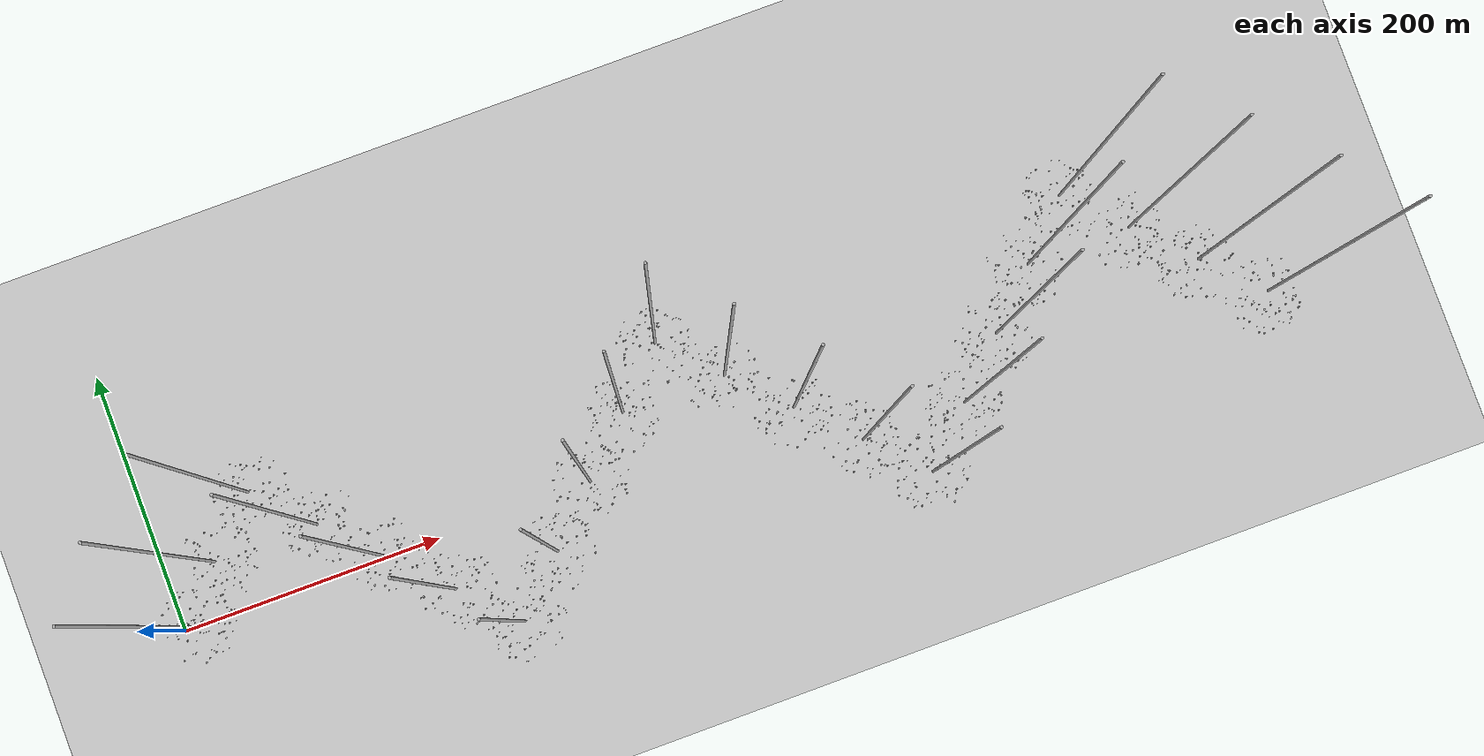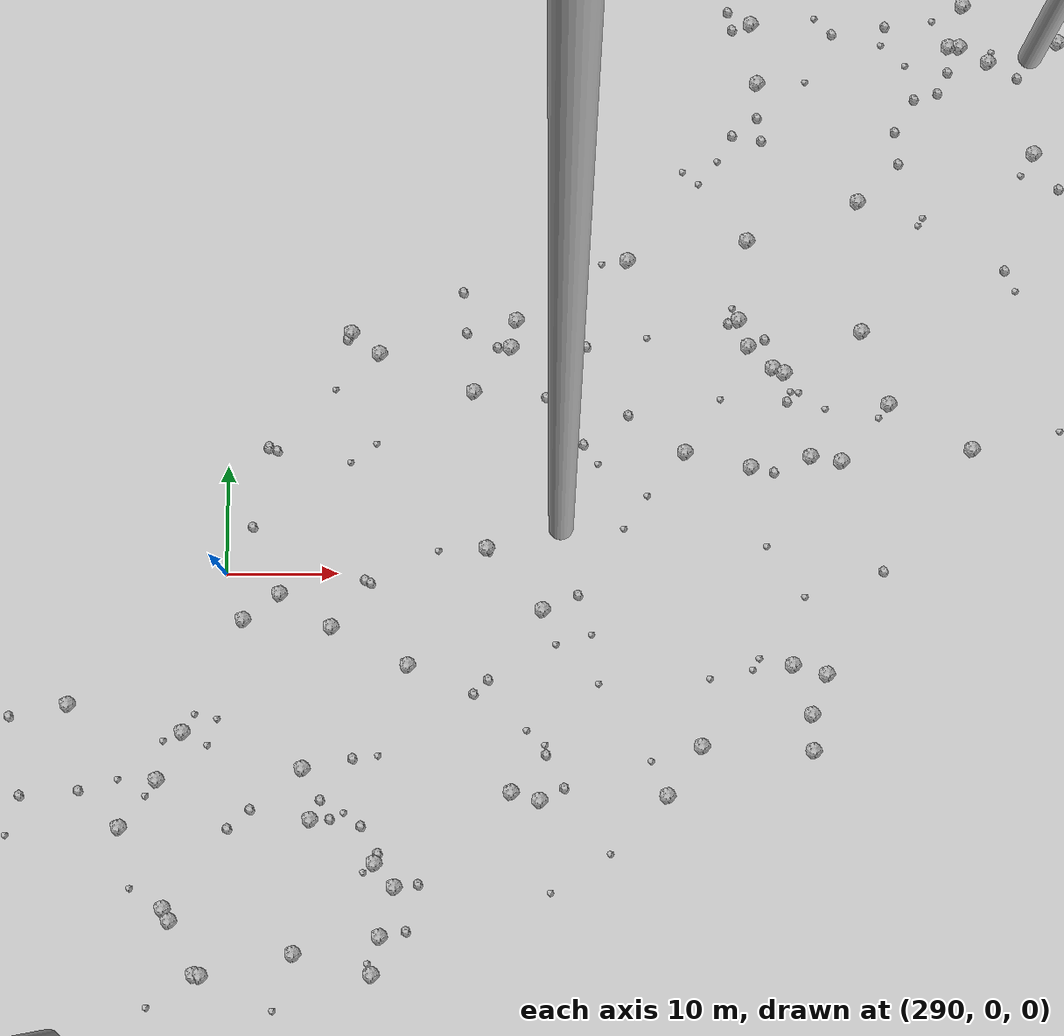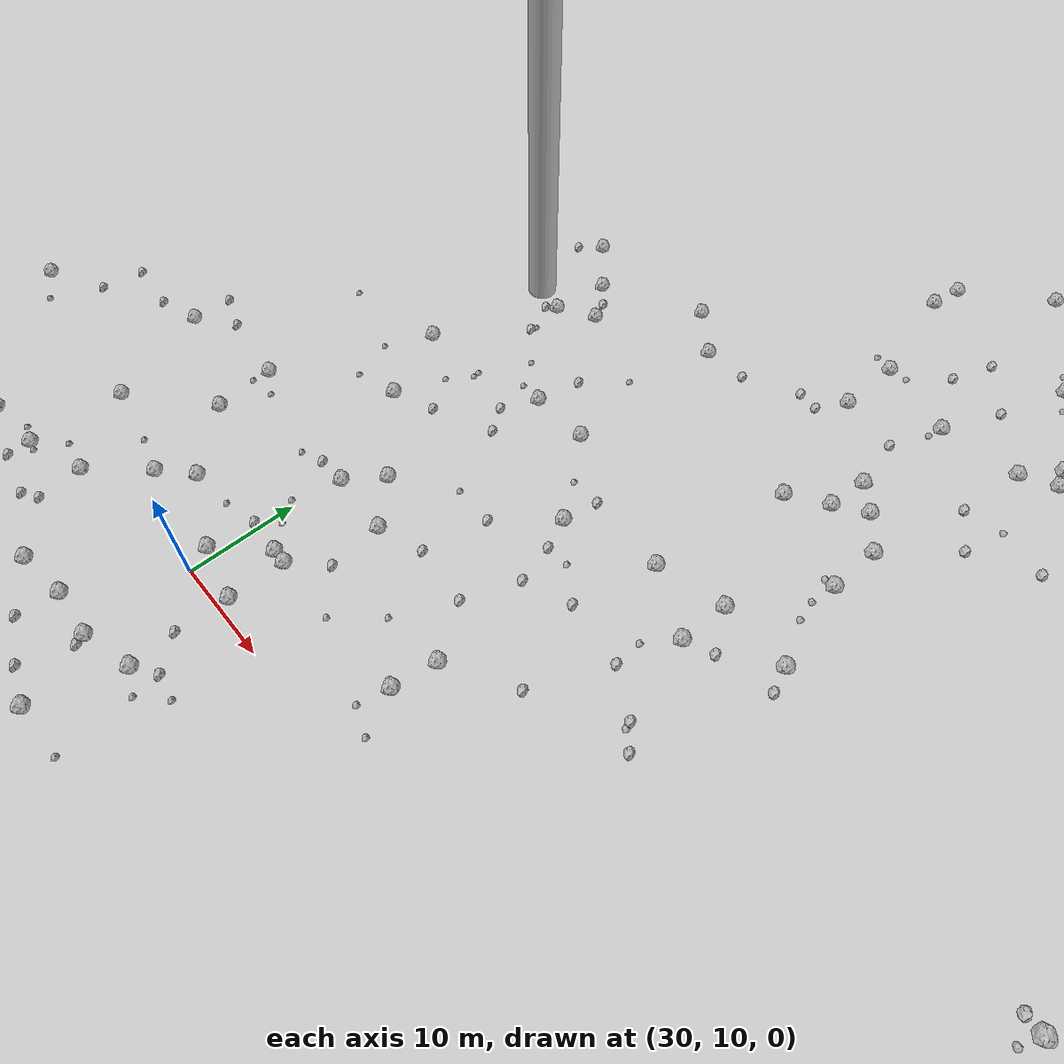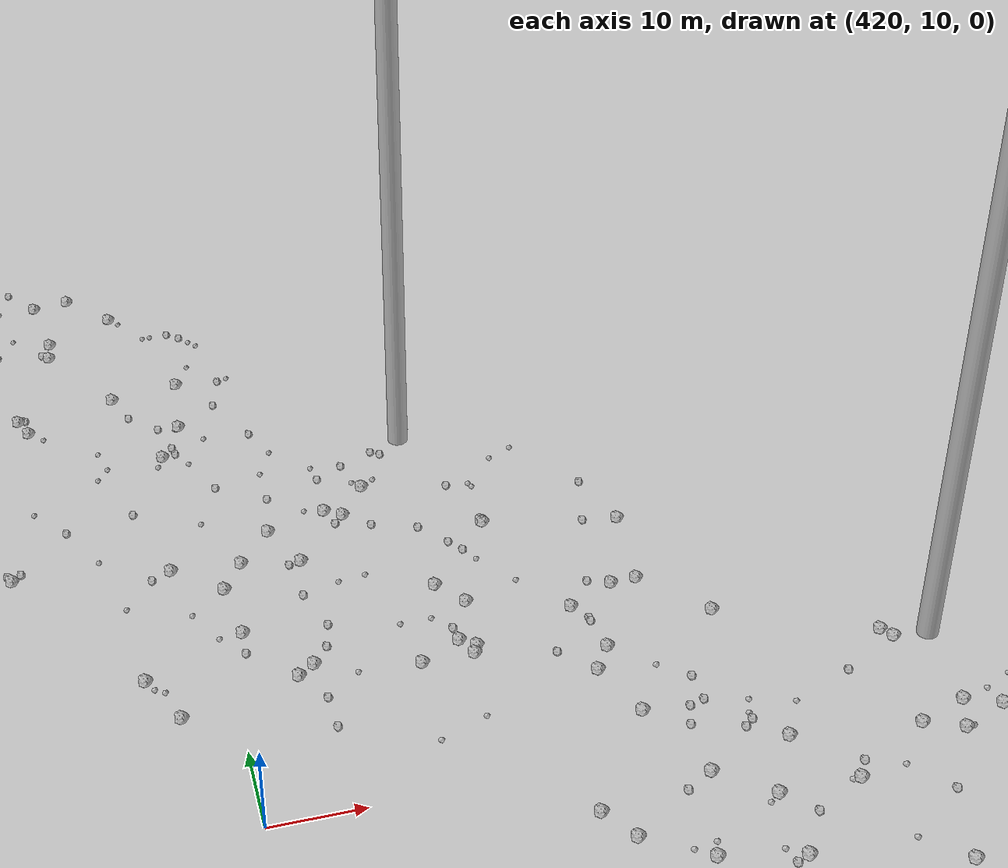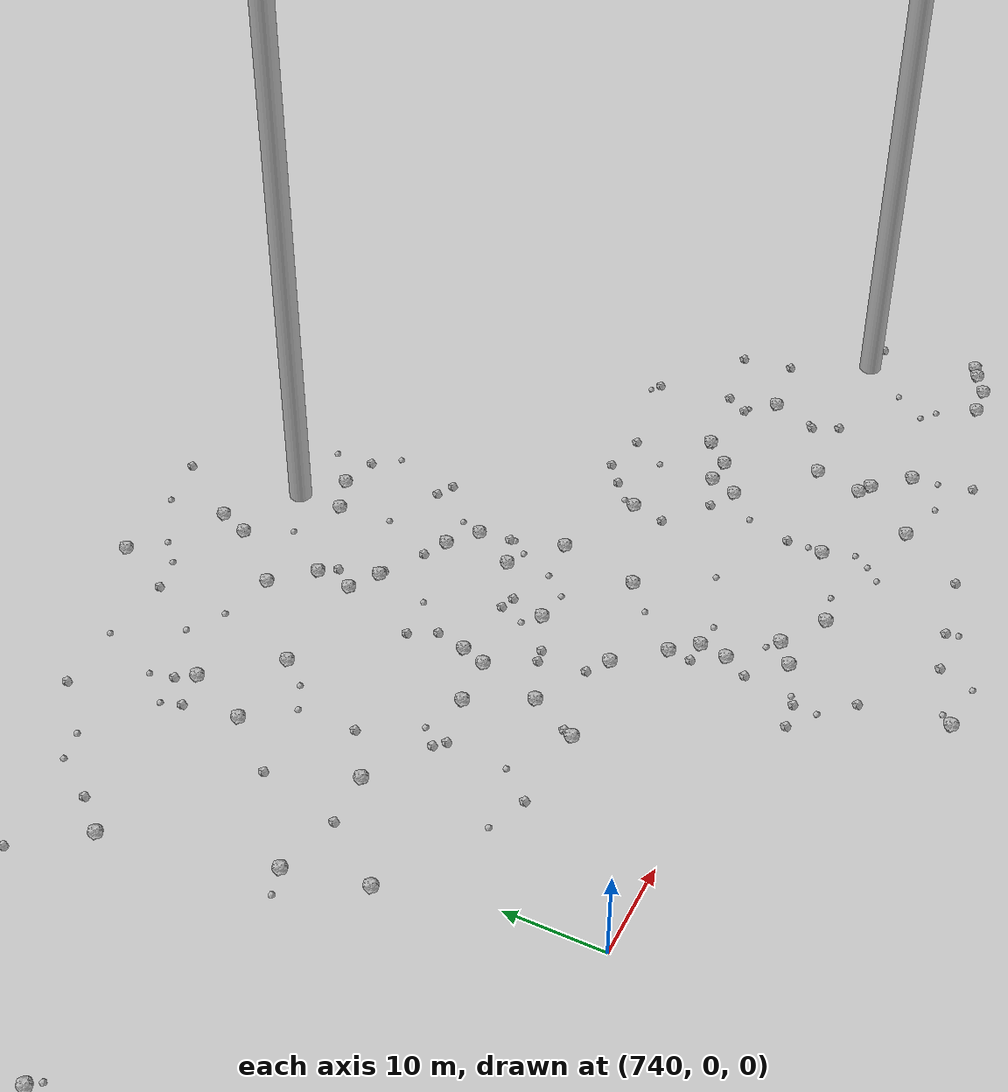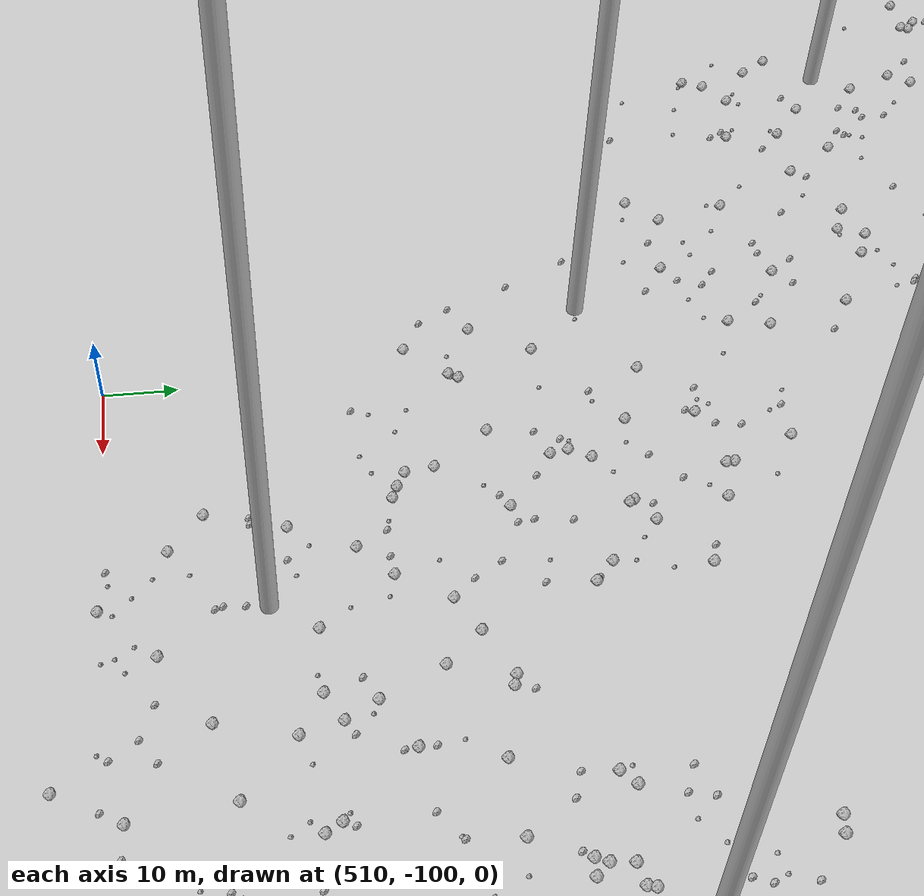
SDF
<sdf version="1.6">
 <world name="default">
  <include><uri>model://custom_ground</uri></include>
  <include><uri>model://sun</uri></include>
  <spherical_coordinates>
   <surface_model>EARTH_WGS84</surface_model>
   <latitude_deg>38.161479</latitude_deg>
   <longitude_deg>-122.454630</longitude_deg>
   <elevation>488.0</elevation>
   <heading_deg>90</heading_deg>
  </spherical_coordinates>
  <model name="rock1_0_0">
   <include><uri>model://rock1</uri><pose>29.081621029015153 12.22818206252078 0.5 0 0 0</pose></include>
  </model>
  <model name="rock1_0_1">
   <include><uri>model://rock1</uri><pose>25.078372861331758 0.9811334057170455 0.5 0 0 0</pose></include>
  </model>
  <model name="rock1_0_2">
   <include><uri>model://rock1</uri><pose>8.351612878462628 14.881337318350361 0.5 0 0 0</pose></include>
  </model>
  <model name="rock1_0_3">
   <include><uri>model://rock1</uri><pose>19.942775597987428 0.25577214342927235 0.5 0 0 0</pose></include>
  </model>
  <model name="rock1_0_4">
   <include><uri>model://rock1</uri><pose>6.919115461972062 -27.207298631161333 0.5 0 0 0</pose></include>
  </model>
  <model name="rock1_0_5">
   <include><uri>model://rock1</uri><pose>29.961421123975676 0.7552967031441185 0.5 0 0 0</pose></include>
  </model>
  <model name="rock1_0_6">
   <include><uri>model://rock1</uri><pose>26.479028678506197 -9.737241466195051 0.5 0 0 0</pose></include>
  </model>
  <model name="rock1_0_7">
   <include><uri>model://rock1</uri><pose>15.057675322480762 26.972359469598402 0.5 0 0 0</pose></include>
  </model>
  <model name="rock1_0_8">
   <include><uri>model://rock1</uri><pose>26.673031978240928 -15.072823608946068 0.5 0 0 0</pose></include>
  </model>
  <model name="rock1_0_9">
   <include><uri>model://rock1</uri><pose>-15.928490123794079 7.007493033703973 0.5 0 0 0</pose></include>
  </model>
  <model name="rock1_0_10">
   <include><uri>model://rock1</uri><pose>-1.1889368436991177 -7.118680778622085 0.5 0 0 0</pose></include>
  </model>
  <model name="rock1_0_11">
   <include><uri>model://rock1</uri><pose>-8.434418131879223 -20.270425423145923 0.5 0 0 0</pose></include>
  </model>
  <model name="rock1_0_12">
   <include><uri>model://rock1</uri><pose>10.20294117969009 -24.696303443367718 0.5 0 0 0</pose></include>
  </model>
  <model name="rock1_0_13">
   <include><uri>model://rock1</uri><pose>34.5809929072856 11.064235645921578 0.5 0 0 0</pose></include>
  </model>
  <model name="rock1_0_14">
   <include><uri>model://rock1</uri><pose>2.142211832747684 5.335646407980043 0.5 0 0 0</pose></include>
  </model>
  <model name="rock1_0_15">
   <include><uri>model://rock1</uri><pose>3.725763168986976 25.26611736636203 0.5 0 0 0</pose></include>
  </model>
  <model name="rock1_0_16">
   <include><uri>model://rock1</uri><pose>21.703837790536497 15.44638809882131 0.5 0 0 0</pose></include>
  </model>
  <model name="rock1_0_17">
   <include><uri>model://rock1</uri><pose>16.144880785353713 -22.269619861631828 0.5 0 0 0</pose></include>
  </model>
  <model name="rock1_0_18">
   <include><uri>model://rock1</uri><pose>18.795874885043716 12.834843732447581 0.5 0 0 0</pose></include>
  </model>
  <model name="rock1_0_19">
   <include><uri>model://rock1</uri><pose>22.79785963820315 -9.787180965971668 0.5 0 0 0</pose></include>
  </model>
  <model name="rock1_0_20">
   <include><uri>model://rock1</uri><pose>14.271460780438517 7.934865588549265 0.5 0 0 0</pose></include>
  </model>
  <model name="rock1_0_21">
   <include><uri>model://rock1</uri><pose>3.114869062041251 4.2066121159513585 0.5 0 0 0</pose></include>
  </model>
  <model name="rock1_0_22">
   <include><uri>model://rock1</uri><pose>32.54616762144239 -5.463079574977598 0.5 0 0 0</pose></include>
  </model>
  <model name="rock1_0_23">
   <include><uri>model://rock1</uri><pose>34.882233140873524 2.1869945071388983 0.5 0 0 0</pose></include>
  </model>
  <model name="rock1_0_24">
   <include><uri>model://rock1</uri><pose>8.298546748713857 5.898650072416061 0.5 0 0 0</pose></include>
  </model>
  <model name="rock1_0_25">
   <include><uri>model://rock1</uri><pose>15.816017510253488 21.12326657239864 0.5 0 0 0</pose></include>
  </model>
  <model name="rock1_0_26">
   <include><uri>model://rock1</uri><pose>-12.52490745590868 17.35295892488213 0.5 0 0 0</pose></include>
  </model>
  <model name="rock2_0_0">
   <include><uri>model://rock2</uri><pose>34.41621669620248 6.254489187675922 0.3 0 0 0</pose></include>
  </model>
  <model name="rock2_0_1">
   <include><uri>model://rock2</uri><pose>-2.842645304881973 6.170340435482572 0.3 0 0 0</pose></include>
  </model>
  <model name="rock2_0_2">
   <include><uri>model://rock2</uri><pose>24.676358698760893 -2.6543679745849715 0.3 0 0 0</pose></include>
  </model>
  <model name="rock2_0_3">
   <include><uri>model://rock2</uri><pose>9.556190837211428 -4.531830047992866 0.3 0 0 0</pose></include>
  </model>
  <model name="rock2_0_4">
   <include><uri>model://rock2</uri><pose>1.2229820305742933 -17.986668934524197 0.3 0 0 0</pose></include>
  </model>
  <model name="rock2_0_5">
   <include><uri>model://rock2</uri><pose>-17.29835947594768 11.223673491608096 0.3 0 0 0</pose></include>
  </model>
  <model name="rock2_0_6">
   <include><uri>model://rock2</uri><pose>15.871571860546965 -5.526277379820296 0.3 0 0 0</pose></include>
  </model>
  <model name="rock2_0_7">
   <include><uri>model://rock2</uri><pose>-6.268826463034863 24.55281934792604 0.3 0 0 0</pose></include>
  </model>
  <model name="rock2_0_8">
   <include><uri>model://rock2</uri><pose>28.85784267212466 -4.4621228069620535 0.3 0 0 0</pose></include>
  </model>
  <model name="rock2_0_9">
   <include><uri>model://rock2</uri><pose>7.312379226973512 27.978800065339136 0.3 0 0 0</pose></include>
  </model>
  <model name="rock2_0_10">
   <include><uri>model://rock2</uri><pose>32.71306723736778 -11.689970238734567 0.3 0 0 0</pose></include>
  </model>
  <model name="rock2_0_11">
   <include><uri>model://rock2</uri><pose>24.720617035462993 -9.751240177944965 0.3 0 0 0</pose></include>
  </model>
  <model name="rock2_0_12">
   <include><uri>model://rock2</uri><pose>-7.557690700804368 1.098475750096025 0.3 0 0 0</pose></include>
  </model>
  <model name="rock2_0_13">
   <include><uri>model://rock2</uri><pose>3.6103774981822596 29.291648956069963 0.3 0 0 0</pose></include>
  </model>
  <model name="rock2_0_14">
   <include><uri>model://rock2</uri><pose>-7.16010944893439 -3.620653108596951 0.3 0 0 0</pose></include>
  </model>
  <model name="rock2_0_15">
   <include><uri>model://rock2</uri><pose>13.22844065797711 2.8136645163629623 0.3 0 0 0</pose></include>
  </model>
  <model name="rock2_0_16">
   <include><uri>model://rock2</uri><pose>25.860868726892974 -22.363631453234127 0.3 0 0 0</pose></include>
  </model>
  <model name="rock2_0_17">
   <include><uri>model://rock2</uri><pose>21.992816016164234 -9.659033878930263 0.3 0 0 0</pose></include>
  </model>
  <model name="rock2_0_18">
   <include><uri>model://rock2</uri><pose>-4.486492667120476 7.183597163444979 0.3 0 0 0</pose></include>
  </model>
  <model name="rock2_0_19">
   <include><uri>model://rock2</uri><pose>14.74008003567954 3.7875767180119553 0.3 0 0 0</pose></include>
  </model>
  <model name="rock2_0_20">
   <include><uri>model://rock2</uri><pose>30.299569381547848 -0.07913624996933066 0.3 0 0 0</pose></include>
  </model>
  <model name="rock2_0_21">
   <include><uri>model://rock2</uri><pose>11.893167813849736 -5.795463806909826 0.3 0 0 0</pose></include>
  </model>
  <model name="rock2_0_22">
   <include><uri>model://rock2</uri><pose>-14.321160269497765 0.5318142691005825 0.3 0 0 0</pose></include>
  </model>
  <model name="rock2_0_23">
   <include><uri>model://rock2</uri><pose>-6.765216850375801 20.376050115755106 0.3 0 0 0</pose></include>
  </model>
  <model name="rock2_0_24">
   <include><uri>model://rock2</uri><pose>36.93629829131663 3.5834461498714703 0.3 0 0 0</pose></include>
  </model>
  <model name="rock2_0_25">
   <include><uri>model://rock2</uri><pose>8.285159011439596 3.7138689797043867 0.3 0 0 0</pose></include>
  </model>
  <model name="rock2_0_26">
   <include><uri>model://rock2</uri><pose>-0.6282125121356437 24.047545141635794 0.3 0 0 0</pose></include>
  </model>
  <model name="rock3_0_0">
   <include><uri>model://rock3</uri><pose>21.047706153313875 -23.547836732799453 0.2 0 0 0</pose></include>
  </model>
  <model name="rock3_0_1">
   <include><uri>model://rock3</uri><pose>-8.27502655753473 -14.745962313724661 0.2 0 0 0</pose></include>
  </model>
  <model name="rock3_0_2">
   <include><uri>model://rock3</uri><pose>17.4423855349373 -1.4590135129211461 0.2 0 0 0</pose></include>
  </model>
  <model name="rock3_0_3">
   <include><uri>model://rock3</uri><pose>-10.02114043054338 8.642002045901378 0.2 0 0 0</pose></include>
  </model>
  <model name="rock3_0_4">
   <include><uri>model://rock3</uri><pose>36.86682555258934 -12.521829354237141 0.2 0 0 0</pose></include>
  </model>
  <model name="rock3_0_5">
   <include><uri>model://rock3</uri><pose>37.797629836423 -5.309226228796099 0.2 0 0 0</pose></include>
  </model>
  <model name="rock3_0_6">
   <include><uri>model://rock3</uri><pose>9.135183366724352 5.682693718925748 0.2 0 0 0</pose></include>
  </model>
  <model name="rock3_0_7">
   <include><uri>model://rock3</uri><pose>13.412986879703958 -19.166847201882078 0.2 0 0 0</pose></include>
  </model>
  <model name="rock3_0_8">
   <include><uri>model://rock3</uri><pose>-15.86298047963557 -6.252895686582487 0.2 0 0 0</pose></include>
  </model>
  <model name="rock3_0_9">
   <include><uri>model://rock3</uri><pose>37.17915987529038 1.1389220013471508 0.2 0 0 0</pose></include>
  </model>
  <model name="rock3_0_10">
   <include><uri>model://rock3</uri><pose>6.172971856030035 6.411225360386993 0.2 0 0 0</pose></include>
  </model>
  <model name="rock3_0_11">
   <include><uri>model://rock3</uri><pose>13.784605103831147 -5.6263548193209765 0.2 0 0 0</pose></include>
  </model>
  <model name="rock3_0_12">
   <include><uri>model://rock3</uri><pose>5.153256058604821 -9.559542186859634 0.2 0 0 0</pose></include>
  </model>
  <model name="rock3_0_13">
   <include><uri>model://rock3</uri><pose>26.93021249145049 -17.801504429993464 0.2 0 0 0</pose></include>
  </model>
  <model name="rock3_0_14">
   <include><uri>model://rock3</uri><pose>-0.6973817127618211 -17.930361746386176 0.2 0 0 0</pose></include>
  </model>
  <model name="rock3_0_15">
   <include><uri>model://rock3</uri><pose>3.4168178601042065 -5.143886418834928 0.2 0 0 0</pose></include>
  </model>
  <model name="rock3_0_16">
   <include><uri>model://rock3</uri><pose>14.849299806560047 -20.657159590918482 0.2 0 0 0</pose></include>
  </model>
  <model name="rock3_0_17">
   <include><uri>model://rock3</uri><pose>39.40130491215274 3.254889787806526 0.2 0 0 0</pose></include>
  </model>
  <model name="rock3_0_18">
   <include><uri>model://rock3</uri><pose>-7.37346663725191 -1.604694368947218 0.2 0 0 0</pose></include>
  </model>
  <model name="rock3_0_19">
   <include><uri>model://rock3</uri><pose>-9.044352649767735 15.52187634266101 0.2 0 0 0</pose></include>
  </model>
  <model name="rock3_0_20">
   <include><uri>model://rock3</uri><pose>2.0144985632817445 -17.34362435412204 0.2 0 0 0</pose></include>
  </model>
  <model name="rock3_0_21">
   <include><uri>model://rock3</uri><pose>18.963082250267384 -17.445189823176506 0.2 0 0 0</pose></include>
  </model>
  <model name="rock3_0_22">
   <include><uri>model://rock3</uri><pose>10.61222941737585 8.426926394587305 0.2 0 0 0</pose></include>
  </model>
  <model name="rock3_0_23">
   <include><uri>model://rock3</uri><pose>13.184299402777981 -19.175083730136343 0.2 0 0 0</pose></include>
  </model>
  <model name="rock3_0_24">
   <include><uri>model://rock3</uri><pose>29.447665869825485 20.270508066993415 0.2 0 0 0</pose></include>
  </model>
  <model name="rock3_0_25">
   <include><uri>model://rock3</uri><pose>29.785179421615588 0.18693584793430063 0.2 0 0 0</pose></include>
  </model>
  <model name="rock3_0_26">
   <include><uri>model://rock3</uri><pose>14.720539215873387 13.804682566274444 0.2 0 0 0</pose></include>
  </model>
  <model name="rock1_1_0">
   <include><uri>model://rock1</uri><pose>25.206581486101374 34.439213437569194 0.5 0 0 0</pose></include>
  </model>
  <model name="rock1_1_1">
   <include><uri>model://rock1</uri><pose>33.04945052861801 28.066241718636103 0.5 0 0 0</pose></include>
  </model>
  <model name="rock1_1_2">
   <include><uri>model://rock1</uri><pose>34.97231061104451 44.17773231695099 0.5 0 0 0</pose></include>
  </model>
  <model name="rock1_1_3">
   <include><uri>model://rock1</uri><pose>66.24253447870592 48.85502400587234 0.5 0 0 0</pose></include>
  </model>
  <model name="rock1_1_4">
   <include><uri>model://rock1</uri><pose>68.25786361215106 40.27868984430076 0.5 0 0 0</pose></include>
  </model>
  <model name="rock1_1_5">
   <include><uri>model://rock1</uri><pose>46.73911378337094 36.66829892356927 0.5 0 0 0</pose></include>
  </model>
  <model name="rock1_1_6">
   <include><uri>model://rock1</uri><pose>30.34991462466286 55.97823810147092 0.5 0 0 0</pose></include>
  </model>
  <model name="rock1_1_7">
   <include><uri>model://rock1</uri><pose>60.897973297231104 55.21290126918121 0.5 0 0 0</pose></include>
  </model>
  <model name="rock1_1_8">
   <include><uri>model://rock1</uri><pose>30.618103697995984 24.745496519520742 0.5 0 0 0</pose></include>
  </model>
  <model name="rock1_1_9">
   <include><uri>model://rock1</uri><pose>33.14020124572975 16.292831936092504 0.5 0 0 0</pose></include>
  </model>
  <model name="rock1_1_10">
   <include><uri>model://rock1</uri><pose>23.058537160485333 64.00587560568536 0.5 0 0 0</pose></include>
  </model>
  <model name="rock1_1_11">
   <include><uri>model://rock1</uri><pose>55.20040403411206 39.378371364239726 0.5 0 0 0</pose></include>
  </model>
  <model name="rock1_1_12">
   <include><uri>model://rock1</uri><pose>57.42797768502272 52.98088205086974 0.5 0 0 0</pose></include>
  </model>
  <model name="rock1_1_13">
   <include><uri>model://rock1</uri><pose>61.2706989507798 59.234071894048434 0.5 0 0 0</pose></include>
  </model>
  <model name="rock1_1_14">
   <include><uri>model://rock1</uri><pose>40.8476816059374 44.1559653635546 0.5 0 0 0</pose></include>
  </model>
  <model name="rock1_1_15">
   <include><uri>model://rock1</uri><pose>27.47874869305005 59.68401824866847 0.5 0 0 0</pose></include>
  </model>
  <model name="rock1_1_16">
   <include><uri>model://rock1</uri><pose>61.375865467944024 35.9896391058608 0.5 0 0 0</pose></include>
  </model>
  <model name="rock1_1_17">
   <include><uri>model://rock1</uri><pose>54.49362701575143 65.84007232372775 0.5 0 0 0</pose></include>
  </model>
  <model name="rock1_1_18">
   <include><uri>model://rock1</uri><pose>37.04578220037169 64.51113564402945 0.5 0 0 0</pose></include>
  </model>
  <model name="rock1_1_19">
   <include><uri>model://rock1</uri><pose>34.6239148999103 16.242328489920745 0.5 0 0 0</pose></include>
  </model>
  <model name="rock1_1_20">
   <include><uri>model://rock1</uri><pose>21.562523715965586 41.933125304757795 0.5 0 0 0</pose></include>
  </model>
  <model name="rock1_1_21">
   <include><uri>model://rock1</uri><pose>49.61437042059543 16.310110918689702 0.5 0 0 0</pose></include>
  </model>
  <model name="rock1_1_22">
   <include><uri>model://rock1</uri><pose>26.80655057369519 53.94977745336303 0.5 0 0 0</pose></include>
  </model>
  <model name="rock1_1_23">
   <include><uri>model://rock1</uri><pose>61.61151286210843 40.70822063959194 0.5 0 0 0</pose></include>
  </model>
  <model name="rock1_1_24">
   <include><uri>model://rock1</uri><pose>36.92041153898113 24.238998149195787 0.5 0 0 0</pose></include>
  </model>
  <model name="rock1_1_25">
   <include><uri>model://rock1</uri><pose>50.23304096856577 20.323988452555994 0.5 0 0 0</pose></include>
  </model>
  <model name="rock1_1_26">
   <include><uri>model://rock1</uri><pose>41.342125223530715 60.86389830565627 0.5 0 0 0</pose></include>
  </model>
  <model name="rock2_1_0">
   <include><uri>model://rock2</uri><pose>52.86687731688163 63.087425922610876 0.3 0 0 0</pose></include>
  </model>
  <model name="rock2_1_1">
   <include><uri>model://rock2</uri><pose>33.38690172931478 40.819009972061366 0.3 0 0 0</pose></include>
  </model>
  <model name="rock2_1_2">
   <include><uri>model://rock2</uri><pose>47.03102114416786 25.021935565686334 0.3 0 0 0</pose></include>
  </model>
  <model name="rock2_1_3">
   <include><uri>model://rock2</uri><pose>56.326119672248275 23.749455662989025 0.3 0 0 0</pose></include>
  </model>
  <model name="rock2_1_4">
   <include><uri>model://rock2</uri><pose>47.314708074379745 40.114458589594825 0.3 0 0 0</pose></include>
  </model>
  <model name="rock2_1_5">
   <include><uri>model://rock2</uri><pose>29.27926473342723 36.002582106040734 0.3 0 0 0</pose></include>
  </model>
  <model name="rock2_1_6">
   <include><uri>model://rock2</uri><pose>63.95219024691574 37.03199863066814 0.3 0 0 0</pose></include>
  </model>
  <model name="rock2_1_7">
   <include><uri>model://rock2</uri><pose>69.04602910391185 37.98140143586806 0.3 0 0 0</pose></include>
  </model>
  <model name="rock2_1_8">
   <include><uri>model://rock2</uri><pose>63.49604076448367 28.15186086181528 0.3 0 0 0</pose></include>
  </model>
  <model name="rock2_1_9">
   <include><uri>model://rock2</uri><pose>41.259515500444536 25.638127678697117 0.3 0 0 0</pose></include>
  </model>
  <model name="rock2_1_10">
   <include><uri>model://rock2</uri><pose>25.871130467347584 53.2128589207768 0.3 0 0 0</pose></include>
  </model>
  <model name="rock2_1_11">
   <include><uri>model://rock2</uri><pose>29.406420596825264 16.568823669792447 0.3 0 0 0</pose></include>
  </model>
  <model name="rock2_1_12">
   <include><uri>model://rock2</uri><pose>48.95257883545086 30.09197577300736 0.3 0 0 0</pose></include>
  </model>
  <model name="rock2_1_13">
   <include><uri>model://rock2</uri><pose>50.81208662325389 63.471145261091415 0.3 0 0 0</pose></include>
  </model>
  <model name="rock2_1_14">
   <include><uri>model://rock2</uri><pose>35.832568583515354 48.56119218467349 0.3 0 0 0</pose></include>
  </model>
  <model name="rock2_1_15">
   <include><uri>model://rock2</uri><pose>27.317580261016975 49.910433371328494 0.3 0 0 0</pose></include>
  </model>
  <model name="rock2_1_16">
   <include><uri>model://rock2</uri><pose>35.032550355932834 38.466993745712585 0.3 0 0 0</pose></include>
  </model>
  <model name="rock2_1_17">
   <include><uri>model://rock2</uri><pose>65.18084696356505 26.38692932397628 0.3 0 0 0</pose></include>
  </model>
  <model name="rock2_1_18">
   <include><uri>model://rock2</uri><pose>29.47480482217224 57.89012502642351 0.3 0 0 0</pose></include>
  </model>
  <model name="rock2_1_19">
   <include><uri>model://rock2</uri><pose>42.44410586981081 31.742711012690048 0.3 0 0 0</pose></include>
  </model>
  <model name="rock2_1_20">
   <include><uri>model://rock2</uri><pose>27.69285225454754 24.692427878165667 0.3 0 0 0</pose></include>
  </model>
  <model name="rock2_1_21">
   <include><uri>model://rock2</uri><pose>47.97179350123272 33.81294059336612 0.3 0 0 0</pose></include>
  </model>
  <model name="rock2_1_22">
   <include><uri>model://rock2</uri><pose>37.45202239435499 19.131391516486698 0.3 0 0 0</pose></include>
  </model>
  <model name="rock2_1_23">
   <include><uri>model://rock2</uri><pose>59.44957215032511 30.651060007902892 0.3 0 0 0</pose></include>
  </model>
  <model name="rock2_1_24">
   <include><uri>model://rock2</uri><pose>53.339644117056565 31.651426139567352 0.3 0 0 0</pose></include>
  </model>
  <model name="rock2_1_25">
   <include><uri>model://rock2</uri><pose>45.68221862585351 60.941580129039245 0.3 0 0 0</pose></include>
  </model>
  <model name="rock2_1_26">
   <include><uri>model://rock2</uri><pose>21.233489169348303 62.11472632696362 0.3 0 0 0</pose></include>
  </model>
  <model name="rock3_1_0">
   <include><uri>model://rock3</uri><pose>25.45635599348016 23.884987766992356 0.2 0 0 0</pose></include>
  </model>
  <model name="rock3_1_1">
   <include><uri>model://rock3</uri><pose>27.429512556124376 50.482484266584954 0.2 0 0 0</pose></include>
  </model>
  <model name="rock3_1_2">
   <include><uri>model://rock3</uri><pose>38.364415880409055 31.92129342443203 0.2 0 0 0</pose></include>
  </model>
  <model name="rock3_1_3">
   <include><uri>model://rock3</uri><pose>32.54312168262719 44.344410620948345 0.2 0 0 0</pose></include>
  </model>
  <model name="rock3_1_4">
   <include><uri>model://rock3</uri><pose>59.34674425028442 33.25378998301875 0.2 0 0 0</pose></include>
  </model>
  <model name="rock3_1_5">
   <include><uri>model://rock3</uri><pose>41.170447550267 16.00108490367337 0.2 0 0 0</pose></include>
  </model>
  <model name="rock3_1_6">
   <include><uri>model://rock3</uri><pose>66.32078376649946 44.40268946350397 0.2 0 0 0</pose></include>
  </model>
  <model name="rock3_1_7">
   <include><uri>model://rock3</uri><pose>51.475589101260766 12.569105582999393 0.2 0 0 0</pose></include>
  </model>
  <model name="rock3_1_8">
   <include><uri>model://rock3</uri><pose>48.918199307018725 13.526604212908698 0.2 0 0 0</pose></include>
  </model>
  <model name="rock3_1_9">
   <include><uri>model://rock3</uri><pose>30.9733002840995 18.33629517257297 0.2 0 0 0</pose></include>
  </model>
  <model name="rock3_1_10">
   <include><uri>model://rock3</uri><pose>19.47612513028647 37.463140854050366 0.2 0 0 0</pose></include>
  </model>
  <model name="rock3_1_11">
   <include><uri>model://rock3</uri><pose>20.97463623203017 33.36927932439008 0.2 0 0 0</pose></include>
  </model>
  <model name="rock3_1_12">
   <include><uri>model://rock3</uri><pose>38.913476328843146 52.31200133329534 0.2 0 0 0</pose></include>
  </model>
  <model name="rock3_1_13">
   <include><uri>model://rock3</uri><pose>11.435848852961497 40.05695041483257 0.2 0 0 0</pose></include>
  </model>
  <model name="rock3_1_14">
   <include><uri>model://rock3</uri><pose>28.48162489092437 41.53487329380237 0.2 0 0 0</pose></include>
  </model>
  <model name="rock3_1_15">
   <include><uri>model://rock3</uri><pose>14.88528028407551 25.232199461559084 0.2 0 0 0</pose></include>
  </model>
  <model name="rock3_1_16">
   <include><uri>model://rock3</uri><pose>50.17938567313313 33.85786273433292 0.2 0 0 0</pose></include>
  </model>
  <model name="rock3_1_17">
   <include><uri>model://rock3</uri><pose>44.467969229857495 19.724437276160064 0.2 0 0 0</pose></include>
  </model>
  <model name="rock3_1_18">
   <include><uri>model://rock3</uri><pose>26.001568804156964 15.7986764400423 0.2 0 0 0</pose></include>
  </model>
  <model name="rock3_1_19">
   <include><uri>model://rock3</uri><pose>63.666914957179515 27.506122383310917 0.2 0 0 0</pose></include>
  </model>
  <model name="rock3_1_20">
   <include><uri>model://rock3</uri><pose>65.24983502889768 48.89183490091979 0.2 0 0 0</pose></include>
  </model>
  <model name="rock3_1_21">
   <include><uri>model://rock3</uri><pose>65.8911311250549 46.39879839139632 0.2 0 0 0</pose></include>
  </model>
  <model name="rock3_1_22">
   <include><uri>model://rock3</uri><pose>26.932263763225667 39.28801717763146 0.2 0 0 0</pose></include>
  </model>
  <model name="rock3_1_23">
   <include><uri>model://rock3</uri><pose>30.768096618223073 46.90269509793091 0.2 0 0 0</pose></include>
  </model>
  <model name="rock3_1_24">
   <include><uri>model://rock3</uri><pose>17.558045117361633 25.559135037493 0.2 0 0 0</pose></include>
  </model>
  <model name="rock3_1_25">
   <include><uri>model://rock3</uri><pose>44.2741924385317 40.135243433946556 0.2 0 0 0</pose></include>
  </model>
  <model name="rock3_1_26">
   <include><uri>model://rock3</uri><pose>28.39037190712942 42.17136737750042 0.2 0 0 0</pose></include>
  </model>
  <model name="rock1_2_0">
   <include><uri>model://rock1</uri><pose>94.99977895461441 72.70370957613363 0.5 0 0 0</pose></include>
  </model>
  <model name="rock1_2_1">
   <include><uri>model://rock1</uri><pose>73.05560556656981 90.23838575630768 0.5 0 0 0</pose></include>
  </model>
  <model name="rock1_2_2">
   <include><uri>model://rock1</uri><pose>62.20092201578676 69.71158233146387 0.5 0 0 0</pose></include>
  </model>
  <model name="rock1_2_3">
   <include><uri>model://rock1</uri><pose>54.48585175437137 72.36644255200936 0.5 0 0 0</pose></include>
  </model>
  <model name="rock1_2_4">
   <include><uri>model://rock1</uri><pose>108.19217474810821 85.28369841728741 0.5 0 0 0</pose></include>
  </model>
  <model name="rock1_2_5">
   <include><uri>model://rock1</uri><pose>66.35348733223697 53.91139730110418 0.5 0 0 0</pose></include>
  </model>
  <model name="rock1_2_6">
   <include><uri>model://rock1</uri><pose>94.98445216649677 82.8845379805862 0.5 0 0 0</pose></include>
  </model>
  <model name="rock1_2_7">
   <include><uri>model://rock1</uri><pose>90.36417105270841 83.64387925791375 0.5 0 0 0</pose></include>
  </model>
  <model name="rock1_2_8">
   <include><uri>model://rock1</uri><pose>90.87843563692309 94.8078223165244 0.5 0 0 0</pose></include>
  </model>
  <model name="rock1_2_9">
   <include><uri>model://rock1</uri><pose>71.07636960547259 95.5922124864909 0.5 0 0 0</pose></include>
  </model>
  <model name="rock1_2_10">
   <include><uri>model://rock1</uri><pose>91.60503800337825 71.69928687936812 0.5 0 0 0</pose></include>
  </model>
  <model name="rock1_2_11">
   <include><uri>model://rock1</uri><pose>72.89623696265647 71.88380876475858 0.5 0 0 0</pose></include>
  </model>
  <model name="rock1_2_12">
   <include><uri>model://rock1</uri><pose>59.93123058621984 93.17908770093446 0.5 0 0 0</pose></include>
  </model>
  <model name="rock1_2_13">
   <include><uri>model://rock1</uri><pose>84.0626762028302 69.48482410260414 0.5 0 0 0</pose></include>
  </model>
  <model name="rock1_2_14">
   <include><uri>model://rock1</uri><pose>88.62127982040015 78.20117910182385 0.5 0 0 0</pose></include>
  </model>
  <model name="rock1_2_15">
   <include><uri>model://rock1</uri><pose>98.93628342912572 93.17978822173808 0.5 0 0 0</pose></include>
  </model>
  <model name="rock1_2_16">
   <include><uri>model://rock1</uri><pose>67.25929783285382 82.40799822044616 0.5 0 0 0</pose></include>
  </model>
  <model name="rock1_2_17">
   <include><uri>model://rock1</uri><pose>51.8331588330894 83.57053539208842 0.5 0 0 0</pose></include>
  </model>
  <model name="rock1_2_18">
   <include><uri>model://rock1</uri><pose>52.35622480791854 86.94845219360347 0.5 0 0 0</pose></include>
  </model>
  <model name="rock1_2_19">
   <include><uri>model://rock1</uri><pose>99.54784824620603 76.23039778308926 0.5 0 0 0</pose></include>
  </model>
  <model name="rock1_2_20">
   <include><uri>model://rock1</uri><pose>69.77287723853283 70.28400610906104 0.5 0 0 0</pose></include>
  </model>
  <model name="rock1_2_21">
   <include><uri>model://rock1</uri><pose>61.648365496906635 94.42997948771225 0.5 0 0 0</pose></include>
  </model>
  <model name="rock1_2_22">
   <include><uri>model://rock1</uri><pose>79.34176714461381 102.66634479494932 0.5 0 0 0</pose></include>
  </model>
  <model name="rock1_2_23">
   <include><uri>model://rock1</uri><pose>106.53452519335757 73.1197030678538 0.5 0 0 0</pose></include>
  </model>
  <model name="rock1_2_24">
   <include><uri>model://rock1</uri><pose>63.67633834339024 57.00893692136002 0.5 0 0 0</pose></include>
  </model>
  <model name="rock1_2_25">
   <include><uri>model://rock1</uri><pose>88.35203900705417 98.42186115689094 0.5 0 0 0</pose></include>
  </model>
  <model name="rock1_2_26">
   <include><uri>model://rock1</uri><pose>72.25684393548075 73.76231761844917 0.5 0 0 0</pose></include>
  </model>
  <model name="rock2_2_0">
   <include><uri>model://rock2</uri><pose>60.76255041625765 80.29614912946431 0.3 0 0 0</pose></include>
  </model>
  <model name="rock2_2_1">
   <include><uri>model://rock2</uri><pose>60.248515867602286 96.11516331464041 0.3 0 0 0</pose></include>
  </model>
  <model name="rock2_2_2">
   <include><uri>model://rock2</uri><pose>59.2114362697718 76.05089536089267 0.3 0 0 0</pose></include>
  </model>
  <model name="rock2_2_3">
   <include><uri>model://rock2</uri><pose>72.34573160570012 74.30604626499088 0.3 0 0 0</pose></include>
  </model>
  <model name="rock2_2_4">
   <include><uri>model://rock2</uri><pose>96.92085859744938 71.12172008938106 0.3 0 0 0</pose></include>
  </model>
  <model name="rock2_2_5">
   <include><uri>model://rock2</uri><pose>84.34934357003362 61.698304984036284 0.3 0 0 0</pose></include>
  </model>
  <model name="rock2_2_6">
   <include><uri>model://rock2</uri><pose>63.67703843815926 96.00099447817496 0.3 0 0 0</pose></include>
  </model>
  <model name="rock2_2_7">
   <include><uri>model://rock2</uri><pose>64.78296934551977 75.5892647726229 0.3 0 0 0</pose></include>
  </model>
  <model name="rock2_2_8">
   <include><uri>model://rock2</uri><pose>68.81956311536479 63.49244057419413 0.3 0 0 0</pose></include>
  </model>
  <model name="rock2_2_9">
   <include><uri>model://rock2</uri><pose>75.36923976546755 103.23363640224441 0.3 0 0 0</pose></include>
  </model>
  <model name="rock2_2_10">
   <include><uri>model://rock2</uri><pose>90.59573968281794 67.69622925282822 0.3 0 0 0</pose></include>
  </model>
  <model name="rock2_2_11">
   <include><uri>model://rock2</uri><pose>82.5728415382828 80.75663660131198 0.3 0 0 0</pose></include>
  </model>
  <model name="rock2_2_12">
   <include><uri>model://rock2</uri><pose>73.19128816593567 90.7443527927264 0.3 0 0 0</pose></include>
  </model>
  <model name="rock2_2_13">
   <include><uri>model://rock2</uri><pose>79.08218756822649 98.94753944264666 0.3 0 0 0</pose></include>
  </model>
  <model name="rock2_2_14">
   <include><uri>model://rock2</uri><pose>76.82374232210154 62.67189991615022 0.3 0 0 0</pose></include>
  </model>
  <model name="rock2_2_15">
   <include><uri>model://rock2</uri><pose>66.92910768538565 87.08025156044492 0.3 0 0 0</pose></include>
  </model>
  <model name="rock2_2_16">
   <include><uri>model://rock2</uri><pose>74.99025488681943 94.05865224026704 0.3 0 0 0</pose></include>
  </model>
  <model name="rock2_2_17">
   <include><uri>model://rock2</uri><pose>61.596285039533264 101.61804900648927 0.3 0 0 0</pose></include>
  </model>
  <model name="rock2_2_18">
   <include><uri>model://rock2</uri><pose>78.25096036274849 72.49051459687175 0.3 0 0 0</pose></include>
  </model>
  <model name="rock2_2_19">
   <include><uri>model://rock2</uri><pose>71.30855925987814 59.89721647208129 0.3 0 0 0</pose></include>
  </model>
  <model name="rock2_2_20">
   <include><uri>model://rock2</uri><pose>79.64635225790755 82.47513707746319 0.3 0 0 0</pose></include>
  </model>
  <model name="rock2_2_21">
   <include><uri>model://rock2</uri><pose>83.23280465931336 100.50648682353975 0.3 0 0 0</pose></include>
  </model>
  <model name="rock2_2_22">
   <include><uri>model://rock2</uri><pose>94.99604655429462 55.964460399426095 0.3 0 0 0</pose></include>
  </model>
  <model name="rock2_2_23">
   <include><uri>model://rock2</uri><pose>60.19687991257237 64.60282688574858 0.3 0 0 0</pose></include>
  </model>
  <model name="rock2_2_24">
   <include><uri>model://rock2</uri><pose>69.73021689766065 81.83052097446284 0.3 0 0 0</pose></include>
  </model>
  <model name="rock2_2_25">
   <include><uri>model://rock2</uri><pose>93.55058577886155 100.05643309670648 0.3 0 0 0</pose></include>
  </model>
  <model name="rock2_2_26">
   <include><uri>model://rock2</uri><pose>77.84909803893483 91.72316621758185 0.3 0 0 0</pose></include>
  </model>
  <model name="rock3_2_0">
   <include><uri>model://rock3</uri><pose>95.57062604225865 102.39208853096838 0.2 0 0 0</pose></include>
  </model>
  <model name="rock3_2_1">
   <include><uri>model://rock3</uri><pose>103.09367047529972 97.10325266204377 0.2 0 0 0</pose></include>
  </model>
  <model name="rock3_2_2">
   <include><uri>model://rock3</uri><pose>70.1221396793589 83.52541989587264 0.2 0 0 0</pose></include>
  </model>
  <model name="rock3_2_3">
   <include><uri>model://rock3</uri><pose>81.29948825142935 99.45470354210451 0.2 0 0 0</pose></include>
  </model>
  <model name="rock3_2_4">
   <include><uri>model://rock3</uri><pose>66.08168747387182 84.30502077736438 0.2 0 0 0</pose></include>
  </model>
  <model name="rock3_2_5">
   <include><uri>model://rock3</uri><pose>61.6571630805224 59.60558333000546 0.2 0 0 0</pose></include>
  </model>
  <model name="rock3_2_6">
   <include><uri>model://rock3</uri><pose>97.36894490263262 83.29515289160167 0.2 0 0 0</pose></include>
  </model>
  <model name="rock3_2_7">
   <include><uri>model://rock3</uri><pose>83.40997167702291 60.241707824443395 0.2 0 0 0</pose></include>
  </model>
  <model name="rock3_2_8">
   <include><uri>model://rock3</uri><pose>52.64435631341909 72.94080560358734 0.2 0 0 0</pose></include>
  </model>
  <model name="rock3_2_9">
   <include><uri>model://rock3</uri><pose>71.92767530698258 105.4560750747114 0.2 0 0 0</pose></include>
  </model>
  <model name="rock3_2_10">
   <include><uri>model://rock3</uri><pose>74.71489154657496 76.13141762788655 0.2 0 0 0</pose></include>
  </model>
  <model name="rock3_2_11">
   <include><uri>model://rock3</uri><pose>72.39150909691652 63.93238012322328 0.2 0 0 0</pose></include>
  </model>
  <model name="rock3_2_12">
   <include><uri>model://rock3</uri><pose>56.27640454712969 72.57385589289476 0.2 0 0 0</pose></include>
  </model>
  <model name="rock3_2_13">
   <include><uri>model://rock3</uri><pose>71.32574960824262 105.86179767451237 0.2 0 0 0</pose></include>
  </model>
  <model name="rock3_2_14">
   <include><uri>model://rock3</uri><pose>102.88670274303952 72.86481914985697 0.2 0 0 0</pose></include>
  </model>
  <model name="rock3_2_15">
   <include><uri>model://rock3</uri><pose>68.39914819895198 80.2575947162731 0.2 0 0 0</pose></include>
  </model>
  <model name="rock3_2_16">
   <include><uri>model://rock3</uri><pose>99.91179833307638 79.64510963517512 0.2 0 0 0</pose></include>
  </model>
  <model name="rock3_2_17">
   <include><uri>model://rock3</uri><pose>106.17386540592976 77.24198705796513 0.2 0 0 0</pose></include>
  </model>
  <model name="rock3_2_18">
   <include><uri>model://rock3</uri><pose>61.844365878284435 68.28378803769746 0.2 0 0 0</pose></include>
  </model>
  <model name="rock3_2_19">
   <include><uri>model://rock3</uri><pose>100.27958835420013 83.52345783827181 0.2 0 0 0</pose></include>
  </model>
  <model name="rock3_2_20">
   <include><uri>model://rock3</uri><pose>108.33923422129388 82.69460760041011 0.2 0 0 0</pose></include>
  </model>
  <model name="rock3_2_21">
   <include><uri>model://rock3</uri><pose>102.6121686463319 82.15313240182351 0.2 0 0 0</pose></include>
  </model>
  <model name="rock3_2_22">
   <include><uri>model://rock3</uri><pose>82.32738325802731 83.99426137856543 0.2 0 0 0</pose></include>
  </model>
  <model name="rock3_2_23">
   <include><uri>model://rock3</uri><pose>69.93047645164023 93.04290313585884 0.2 0 0 0</pose></include>
  </model>
  <model name="rock3_2_24">
   <include><uri>model://rock3</uri><pose>87.21565640377855 77.60371191086068 0.2 0 0 0</pose></include>
  </model>
  <model name="rock3_2_25">
   <include><uri>model://rock3</uri><pose>64.24476834767997 100.49418695791731 0.2 0 0 0</pose></include>
  </model>
  <model name="rock3_2_26">
   <include><uri>model://rock3</uri><pose>97.29227423011122 63.37475509063186 0.2 0 0 0</pose></include>
  </model>
  <model name="rock1_3_0">
   <include><uri>model://rock1</uri><pose>135.2847434595609 41.11869035077509 0.5 0 0 0</pose></include>
  </model>
  <model name="rock1_3_1">
   <include><uri>model://rock1</uri><pose>96.40814441845082 58.051040441689416 0.5 0 0 0</pose></include>
  </model>
  <model name="rock1_3_2">
   <include><uri>model://rock1</uri><pose>96.26630801966876 42.02395251167731 0.5 0 0 0</pose></include>
  </model>
  <model name="rock1_3_3">
   <include><uri>model://rock1</uri><pose>131.6827899188238 52.019592577900816 0.5 0 0 0</pose></include>
  </model>
  <model name="rock1_3_4">
   <include><uri>model://rock1</uri><pose>106.15754493400951 43.6555525354287 0.5 0 0 0</pose></include>
  </model>
  <model name="rock1_3_5">
   <include><uri>model://rock1</uri><pose>111.53926182941953 22.545957403976022 0.5 0 0 0</pose></include>
  </model>
  <model name="rock1_3_6">
   <include><uri>model://rock1</uri><pose>110.19214244793032 60.37970900332933 0.5 0 0 0</pose></include>
  </model>
  <model name="rock1_3_7">
   <include><uri>model://rock1</uri><pose>94.8412041563529 32.89521020317529 0.5 0 0 0</pose></include>
  </model>
  <model name="rock1_3_8">
   <include><uri>model://rock1</uri><pose>114.55781980158544 63.72690433501606 0.5 0 0 0</pose></include>
  </model>
  <model name="rock1_3_9">
   <include><uri>model://rock1</uri><pose>99.2788234162915 28.59408148535291 0.5 0 0 0</pose></include>
  </model>
  <model name="rock1_3_10">
   <include><uri>model://rock1</uri><pose>126.44700787607734 53.37319517210069 0.5 0 0 0</pose></include>
  </model>
  <model name="rock1_3_11">
   <include><uri>model://rock1</uri><pose>134.18023445950024 18.80799968725468 0.5 0 0 0</pose></include>
  </model>
  <model name="rock1_3_12">
   <include><uri>model://rock1</uri><pose>122.5411501479027 51.327949307244175 0.5 0 0 0</pose></include>
  </model>
  <model name="rock1_3_13">
   <include><uri>model://rock1</uri><pose>119.85806268137928 44.61285522015178 0.5 0 0 0</pose></include>
  </model>
  <model name="rock1_3_14">
   <include><uri>model://rock1</uri><pose>125.08080867959659 10.68763178268781 0.5 0 0 0</pose></include>
  </model>
  <model name="rock1_3_15">
   <include><uri>model://rock1</uri><pose>114.05379463605402 58.43132619812282 0.5 0 0 0</pose></include>
  </model>
  <model name="rock1_3_16">
   <include><uri>model://rock1</uri><pose>140.8782924105569 44.02739846784827 0.5 0 0 0</pose></include>
  </model>
  <model name="rock1_3_17">
   <include><uri>model://rock1</uri><pose>132.92203977299857 32.64658614926837 0.5 0 0 0</pose></include>
  </model>
  <model name="rock1_3_18">
   <include><uri>model://rock1</uri><pose>120.879873511864 51.26693328392214 0.5 0 0 0</pose></include>
  </model>
  <model name="rock1_3_19">
   <include><uri>model://rock1</uri><pose>114.4326992616977 49.47202781595532 0.5 0 0 0</pose></include>
  </model>
  <model name="rock1_3_20">
   <include><uri>model://rock1</uri><pose>134.02499903147728 43.28996249323859 0.5 0 0 0</pose></include>
  </model>
  <model name="rock1_3_21">
   <include><uri>model://rock1</uri><pose>136.4316651542829 33.13840303003654 0.5 0 0 0</pose></include>
  </model>
  <model name="rock1_3_22">
   <include><uri>model://rock1</uri><pose>132.77911097595148 35.24662748375514 0.5 0 0 0</pose></include>
  </model>
  <model name="rock1_3_23">
   <include><uri>model://rock1</uri><pose>104.88355441975504 21.5842913622538 0.5 0 0 0</pose></include>
  </model>
  <model name="rock1_3_24">
   <include><uri>model://rock1</uri><pose>110.10731669309476 53.47327343998916 0.5 0 0 0</pose></include>
  </model>
  <model name="rock1_3_25">
   <include><uri>model://rock1</uri><pose>138.1623195733208 23.80838475823254 0.5 0 0 0</pose></include>
  </model>
  <model name="rock1_3_26">
   <include><uri>model://rock1</uri><pose>131.4283575868948 59.39436118788594 0.5 0 0 0</pose></include>
  </model>
  <model name="rock2_3_0">
   <include><uri>model://rock2</uri><pose>146.86623704720756 52.91330177238063 0.3 0 0 0</pose></include>
  </model>
  <model name="rock2_3_1">
   <include><uri>model://rock2</uri><pose>97.37072842559233 48.64261599993772 0.3 0 0 0</pose></include>
  </model>
  <model name="rock2_3_2">
   <include><uri>model://rock2</uri><pose>127.7136229531973 21.12508159872654 0.3 0 0 0</pose></include>
  </model>
  <model name="rock2_3_3">
   <include><uri>model://rock2</uri><pose>132.81381234081255 34.711107491676046 0.3 0 0 0</pose></include>
  </model>
  <model name="rock2_3_4">
   <include><uri>model://rock2</uri><pose>126.74064357075136 47.74643184464901 0.3 0 0 0</pose></include>
  </model>
  <model name="rock2_3_5">
   <include><uri>model://rock2</uri><pose>125.77780918319603 15.151665807956647 0.3 0 0 0</pose></include>
  </model>
  <model name="rock2_3_6">
   <include><uri>model://rock2</uri><pose>93.3900575604953 33.16968198653075 0.3 0 0 0</pose></include>
  </model>
  <model name="rock2_3_7">
   <include><uri>model://rock2</uri><pose>137.16199707696018 36.51279011449266 0.3 0 0 0</pose></include>
  </model>
  <model name="rock2_3_8">
   <include><uri>model://rock2</uri><pose>92.01489771723598 44.14436870612351 0.3 0 0 0</pose></include>
  </model>
  <model name="rock2_3_9">
   <include><uri>model://rock2</uri><pose>111.55295919277134 26.24338454540241 0.3 0 0 0</pose></include>
  </model>
  <model name="rock2_3_10">
   <include><uri>model://rock2</uri><pose>105.52669078428505 38.8117416652436 0.3 0 0 0</pose></include>
  </model>
  <model name="rock2_3_11">
   <include><uri>model://rock2</uri><pose>104.67027272908219 41.850590668135055 0.3 0 0 0</pose></include>
  </model>
  <model name="rock2_3_12">
   <include><uri>model://rock2</uri><pose>111.52713969619057 28.239720345334785 0.3 0 0 0</pose></include>
  </model>
  <model name="rock2_3_13">
   <include><uri>model://rock2</uri><pose>107.30369934037208 32.5287248980662 0.3 0 0 0</pose></include>
  </model>
  <model name="rock2_3_14">
   <include><uri>model://rock2</uri><pose>119.63592886085682 12.061584381122879 0.3 0 0 0</pose></include>
  </model>
  <model name="rock2_3_15">
   <include><uri>model://rock2</uri><pose>110.22325441852965 24.472108711045898 0.3 0 0 0</pose></include>
  </model>
  <model name="rock2_3_16">
   <include><uri>model://rock2</uri><pose>98.26804060015303 46.252193882464695 0.3 0 0 0</pose></include>
  </model>
  <model name="rock2_3_17">
   <include><uri>model://rock2</uri><pose>123.6694504397077 43.47301382849503 0.3 0 0 0</pose></include>
  </model>
  <model name="rock2_3_18">
   <include><uri>model://rock2</uri><pose>100.86079474857642 45.724767458547376 0.3 0 0 0</pose></include>
  </model>
  <model name="rock2_3_19">
   <include><uri>model://rock2</uri><pose>125.04903935386422 28.34889837133285 0.3 0 0 0</pose></include>
  </model>
  <model name="rock2_3_20">
   <include><uri>model://rock2</uri><pose>125.58618243494506 10.823757512383256 0.3 0 0 0</pose></include>
  </model>
  <model name="rock2_3_21">
   <include><uri>model://rock2</uri><pose>136.25286813031843 22.167113310499488 0.3 0 0 0</pose></include>
  </model>
  <model name="rock2_3_22">
   <include><uri>model://rock2</uri><pose>126.82225099274251 50.23960525578716 0.3 0 0 0</pose></include>
  </model>
  <model name="rock2_3_23">
   <include><uri>model://rock2</uri><pose>104.54140467465663 54.031350936097155 0.3 0 0 0</pose></include>
  </model>
  <model name="rock2_3_24">
   <include><uri>model://rock2</uri><pose>103.06267703058165 46.47695095716031 0.3 0 0 0</pose></include>
  </model>
  <model name="rock2_3_25">
   <include><uri>model://rock2</uri><pose>119.58099749012167 47.23350625769351 0.3 0 0 0</pose></include>
  </model>
  <model name="rock2_3_26">
   <include><uri>model://rock2</uri><pose>140.38848704078188 45.93633555625251 0.3 0 0 0</pose></include>
  </model>
  <model name="rock3_3_0">
   <include><uri>model://rock3</uri><pose>130.39281731724049 19.635303782175992 0.2 0 0 0</pose></include>
  </model>
  <model name="rock3_3_1">
   <include><uri>model://rock3</uri><pose>121.26575089483151 57.33601845379304 0.2 0 0 0</pose></include>
  </model>
  <model name="rock3_3_2">
   <include><uri>model://rock3</uri><pose>139.53969441666246 46.30671159473576 0.2 0 0 0</pose></include>
  </model>
  <model name="rock3_3_3">
   <include><uri>model://rock3</uri><pose>131.18175275206005 51.501575822346524 0.2 0 0 0</pose></include>
  </model>
  <model name="rock3_3_4">
   <include><uri>model://rock3</uri><pose>127.60638501529627 66.5125421268219 0.2 0 0 0</pose></include>
  </model>
  <model name="rock3_3_5">
   <include><uri>model://rock3</uri><pose>113.6465781769318 40.9060647247932 0.2 0 0 0</pose></include>
  </model>
  <model name="rock3_3_6">
   <include><uri>model://rock3</uri><pose>126.13636248984741 20.07930767017759 0.2 0 0 0</pose></include>
  </model>
  <model name="rock3_3_7">
   <include><uri>model://rock3</uri><pose>123.90006681276651 27.27216189565239 0.2 0 0 0</pose></include>
  </model>
  <model name="rock3_3_8">
   <include><uri>model://rock3</uri><pose>94.0852449254323 31.213806241243528 0.2 0 0 0</pose></include>
  </model>
  <model name="rock3_3_9">
   <include><uri>model://rock3</uri><pose>108.05779565376554 65.11028654466375 0.2 0 0 0</pose></include>
  </model>
  <model name="rock3_3_10">
   <include><uri>model://rock3</uri><pose>127.19792165037234 28.71023315453254 0.2 0 0 0</pose></include>
  </model>
  <model name="rock3_3_11">
   <include><uri>model://rock3</uri><pose>114.01752895640698 61.47731490732015 0.2 0 0 0</pose></include>
  </model>
  <model name="rock3_3_12">
   <include><uri>model://rock3</uri><pose>116.65803733375262 50.97696400398407 0.2 0 0 0</pose></include>
  </model>
  <model name="rock3_3_13">
   <include><uri>model://rock3</uri><pose>120.1336884224789 10.867981512466853 0.2 0 0 0</pose></include>
  </model>
  <model name="rock3_3_14">
   <include><uri>model://rock3</uri><pose>142.7525684083005 58.57352186638917 0.2 0 0 0</pose></include>
  </model>
  <model name="rock3_3_15">
   <include><uri>model://rock3</uri><pose>124.98705963690556 52.571999610456196 0.2 0 0 0</pose></include>
  </model>
  <model name="rock3_3_16">
   <include><uri>model://rock3</uri><pose>127.17624422913599 65.08974716902165 0.2 0 0 0</pose></include>
  </model>
  <model name="rock3_3_17">
   <include><uri>model://rock3</uri><pose>144.13632606942127 44.3119809612616 0.2 0 0 0</pose></include>
  </model>
  <model name="rock3_3_18">
   <include><uri>model://rock3</uri><pose>102.42350368581646 64.30835916525308 0.2 0 0 0</pose></include>
  </model>
  <model name="rock3_3_19">
   <include><uri>model://rock3</uri><pose>121.5018352219787 56.62877890546153 0.2 0 0 0</pose></include>
  </model>
  <model name="rock3_3_20">
   <include><uri>model://rock3</uri><pose>99.20658753912747 38.51695835891026 0.2 0 0 0</pose></include>
  </model>
  <model name="rock3_3_21">
   <include><uri>model://rock3</uri><pose>94.42210561529956 28.918178314333833 0.2 0 0 0</pose></include>
  </model>
  <model name="rock3_3_22">
   <include><uri>model://rock3</uri><pose>125.96611430383226 56.567038460536935 0.2 0 0 0</pose></include>
  </model>
  <model name="rock3_3_23">
   <include><uri>model://rock3</uri><pose>122.05702524902816 64.94522316889463 0.2 0 0 0</pose></include>
  </model>
  <model name="rock3_3_24">
   <include><uri>model://rock3</uri><pose>115.58532221506502 25.859417189140505 0.2 0 0 0</pose></include>
  </model>
  <model name="rock3_3_25">
   <include><uri>model://rock3</uri><pose>102.4800132361281 53.687383820455004 0.2 0 0 0</pose></include>
  </model>
  <model name="rock3_3_26">
   <include><uri>model://rock3</uri><pose>115.42800874870844 13.931876403494803 0.2 0 0 0</pose></include>
  </model>
  <model name="rock1_4_0">
   <include><uri>model://rock1</uri><pose>172.90827234790436 25.42344872189294 0.5 0 0 0</pose></include>
  </model>
  <model name="rock1_4_1">
   <include><uri>model://rock1</uri><pose>168.17662397480575 -22.32104541385052 0.5 0 0 0</pose></include>
  </model>
  <model name="rock1_4_2">
   <include><uri>model://rock1</uri><pose>171.59865342830727 5.526660870948696 0.5 0 0 0</pose></include>
  </model>
  <model name="rock1_4_3">
   <include><uri>model://rock1</uri><pose>156.5007466972025 -12.146968999104217 0.5 0 0 0</pose></include>
  </model>
  <model name="rock1_4_4">
   <include><uri>model://rock1</uri><pose>141.5585814586077 -5.276927765922391 0.5 0 0 0</pose></include>
  </model>
  <model name="rock1_4_5">
   <include><uri>model://rock1</uri><pose>163.38045323854828 -0.3627374600994955 0.5 0 0 0</pose></include>
  </model>
  <model name="rock1_4_6">
   <include><uri>model://rock1</uri><pose>173.12350612982647 25.813937358719272 0.5 0 0 0</pose></include>
  </model>
  <model name="rock1_4_7">
   <include><uri>model://rock1</uri><pose>146.33424551376157 -7.418220865029383 0.5 0 0 0</pose></include>
  </model>
  <model name="rock1_4_8">
   <include><uri>model://rock1</uri><pose>170.83006939088511 -4.907875648390004 0.5 0 0 0</pose></include>
  </model>
  <model name="rock1_4_9">
   <include><uri>model://rock1</uri><pose>146.8745034158265 26.55736916545426 0.5 0 0 0</pose></include>
  </model>
  <model name="rock1_4_10">
   <include><uri>model://rock1</uri><pose>162.43342805625164 24.063269332551847 0.5 0 0 0</pose></include>
  </model>
  <model name="rock1_4_11">
   <include><uri>model://rock1</uri><pose>167.58722792705163 22.161141719016477 0.5 0 0 0</pose></include>
  </model>
  <model name="rock1_4_12">
   <include><uri>model://rock1</uri><pose>154.41441844175705 1.3299182489123211 0.5 0 0 0</pose></include>
  </model>
  <model name="rock1_4_13">
   <include><uri>model://rock1</uri><pose>163.91050709945907 -5.379789889073564 0.5 0 0 0</pose></include>
  </model>
  <model name="rock1_4_14">
   <include><uri>model://rock1</uri><pose>158.66849068645675 6.148709538285445 0.5 0 0 0</pose></include>
  </model>
  <model name="rock1_4_15">
   <include><uri>model://rock1</uri><pose>151.09531350446858 22.279228921996555 0.5 0 0 0</pose></include>
  </model>
  <model name="rock1_4_16">
   <include><uri>model://rock1</uri><pose>169.48298638552532 3.9470720282696306 0.5 0 0 0</pose></include>
  </model>
  <model name="rock1_4_17">
   <include><uri>model://rock1</uri><pose>169.42480640000113 -24.81838616217228 0.5 0 0 0</pose></include>
  </model>
  <model name="rock1_4_18">
   <include><uri>model://rock1</uri><pose>152.92119330496678 -0.40157191393753777 0.5 0 0 0</pose></include>
  </model>
  <model name="rock1_4_19">
   <include><uri>model://rock1</uri><pose>143.0516858696157 -16.117780162144193 0.5 0 0 0</pose></include>
  </model>
  <model name="rock1_4_20">
   <include><uri>model://rock1</uri><pose>170.94889097997273 21.82601054696361 0.5 0 0 0</pose></include>
  </model>
  <model name="rock1_4_21">
   <include><uri>model://rock1</uri><pose>158.40574806734602 -15.022007167844794 0.5 0 0 0</pose></include>
  </model>
  <model name="rock1_4_22">
   <include><uri>model://rock1</uri><pose>150.15905017349857 -19.166327517836972 0.5 0 0 0</pose></include>
  </model>
  <model name="rock1_4_23">
   <include><uri>model://rock1</uri><pose>168.9582274513744 6.3106514248855206 0.5 0 0 0</pose></include>
  </model>
  <model name="rock1_4_24">
   <include><uri>model://rock1</uri><pose>170.40140362367518 9.755317494775888 0.5 0 0 0</pose></include>
  </model>
  <model name="rock1_4_25">
   <include><uri>model://rock1</uri><pose>173.69589404569024 -13.143396031369171 0.5 0 0 0</pose></include>
  </model>
  <model name="rock1_4_26">
   <include><uri>model://rock1</uri><pose>177.4719998877136 -13.033007191498626 0.5 0 0 0</pose></include>
  </model>
  <model name="rock2_4_0">
   <include><uri>model://rock2</uri><pose>164.76413459906246 -11.382876229003934 0.3 0 0 0</pose></include>
  </model>
  <model name="rock2_4_1">
   <include><uri>model://rock2</uri><pose>142.8322459407662 7.802446996456396 0.3 0 0 0</pose></include>
  </model>
  <model name="rock2_4_2">
   <include><uri>model://rock2</uri><pose>157.67382725548407 -9.606664114320257 0.3 0 0 0</pose></include>
  </model>
  <model name="rock2_4_3">
   <include><uri>model://rock2</uri><pose>149.7229095295574 7.369010069753493 0.3 0 0 0</pose></include>
  </model>
  <model name="rock2_4_4">
   <include><uri>model://rock2</uri><pose>178.5120730104565 0.17670584168372017 0.3 0 0 0</pose></include>
  </model>
  <model name="rock2_4_5">
   <include><uri>model://rock2</uri><pose>182.92818703701784 -9.874104930328865 0.3 0 0 0</pose></include>
  </model>
  <model name="rock2_4_6">
   <include><uri>model://rock2</uri><pose>137.6961187228952 15.245863693520334 0.3 0 0 0</pose></include>
  </model>
  <model name="rock2_4_7">
   <include><uri>model://rock2</uri><pose>167.9122098284621 10.89262265704673 0.3 0 0 0</pose></include>
  </model>
  <model name="rock2_4_8">
   <include><uri>model://rock2</uri><pose>141.79921717332226 -10.18956812467145 0.3 0 0 0</pose></include>
  </model>
  <model name="rock2_4_9">
   <include><uri>model://rock2</uri><pose>167.542866059378 -27.100043729604252 0.3 0 0 0</pose></include>
  </model>
  <model name="rock2_4_10">
   <include><uri>model://rock2</uri><pose>132.3853663067844 -7.22271927028703 0.3 0 0 0</pose></include>
  </model>
  <model name="rock2_4_11">
   <include><uri>model://rock2</uri><pose>138.9596574545261 -12.202605723463016 0.3 0 0 0</pose></include>
  </model>
  <model name="rock2_4_12">
   <include><uri>model://rock2</uri><pose>151.9959396965604 21.681107421990596 0.3 0 0 0</pose></include>
  </model>
  <model name="rock2_4_13">
   <include><uri>model://rock2</uri><pose>184.4767594515076 -1.1058284896593946 0.3 0 0 0</pose></include>
  </model>
  <model name="rock2_4_14">
   <include><uri>model://rock2</uri><pose>176.8838001696833 20.099717855896984 0.3 0 0 0</pose></include>
  </model>
  <model name="rock2_4_15">
   <include><uri>model://rock2</uri><pose>173.35239803877417 24.977682239442217 0.3 0 0 0</pose></include>
  </model>
  <model name="rock2_4_16">
   <include><uri>model://rock2</uri><pose>148.34493022656758 13.148348000730522 0.3 0 0 0</pose></include>
  </model>
  <model name="rock2_4_17">
   <include><uri>model://rock2</uri><pose>175.31915932963955 9.320267425540997 0.3 0 0 0</pose></include>
  </model>
  <model name="rock2_4_18">
   <include><uri>model://rock2</uri><pose>139.4380375244291 -18.532803387254607 0.3 0 0 0</pose></include>
  </model>
  <model name="rock2_4_19">
   <include><uri>model://rock2</uri><pose>176.8459748857457 -14.263339209683803 0.3 0 0 0</pose></include>
  </model>
  <model name="rock2_4_20">
   <include><uri>model://rock2</uri><pose>141.55161400180026 14.318880018351848 0.3 0 0 0</pose></include>
  </model>
  <model name="rock2_4_21">
   <include><uri>model://rock2</uri><pose>158.2187227526694 12.003358675359081 0.3 0 0 0</pose></include>
  </model>
  <model name="rock2_4_22">
   <include><uri>model://rock2</uri><pose>151.55734713686007 -23.12076328333824 0.3 0 0 0</pose></include>
  </model>
  <model name="rock2_4_23">
   <include><uri>model://rock2</uri><pose>146.20935263531896 14.830001717790644 0.3 0 0 0</pose></include>
  </model>
  <model name="rock2_4_24">
   <include><uri>model://rock2</uri><pose>156.81600880697331 0.9960970259468418 0.3 0 0 0</pose></include>
  </model>
  <model name="rock2_4_25">
   <include><uri>model://rock2</uri><pose>149.2078428083235 -9.95655771736504 0.3 0 0 0</pose></include>
  </model>
  <model name="rock2_4_26">
   <include><uri>model://rock2</uri><pose>147.77045556469812 -2.1844721217862997 0.3 0 0 0</pose></include>
  </model>
  <model name="rock3_4_0">
   <include><uri>model://rock3</uri><pose>142.6952864860274 -3.295203161879936 0.2 0 0 0</pose></include>
  </model>
  <model name="rock3_4_1">
   <include><uri>model://rock3</uri><pose>156.92248906425164 -16.708920025916676 0.2 0 0 0</pose></include>
  </model>
  <model name="rock3_4_2">
   <include><uri>model://rock3</uri><pose>158.71885362910274 22.008106704018203 0.2 0 0 0</pose></include>
  </model>
  <model name="rock3_4_3">
   <include><uri>model://rock3</uri><pose>174.06119650764495 -24.82511717949638 0.2 0 0 0</pose></include>
  </model>
  <model name="rock3_4_4">
   <include><uri>model://rock3</uri><pose>182.40956629848932 -2.8126918465155804 0.2 0 0 0</pose></include>
  </model>
  <model name="rock3_4_5">
   <include><uri>model://rock3</uri><pose>187.256234954556 -3.6753581544214207 0.2 0 0 0</pose></include>
  </model>
  <model name="rock3_4_6">
   <include><uri>model://rock3</uri><pose>142.3057992438095 15.78082558494988 0.2 0 0 0</pose></include>
  </model>
  <model name="rock3_4_7">
   <include><uri>model://rock3</uri><pose>154.08766463698606 16.41839245277579 0.2 0 0 0</pose></include>
  </model>
  <model name="rock3_4_8">
   <include><uri>model://rock3</uri><pose>173.50371579812833 -3.3647241292721866 0.2 0 0 0</pose></include>
  </model>
  <model name="rock3_4_9">
   <include><uri>model://rock3</uri><pose>153.93747147963416 26.728226669557124 0.2 0 0 0</pose></include>
  </model>
  <model name="rock3_4_10">
   <include><uri>model://rock3</uri><pose>177.22353825951998 -14.92864577386747 0.2 0 0 0</pose></include>
  </model>
  <model name="rock3_4_11">
   <include><uri>model://rock3</uri><pose>151.71067358220316 21.364186737313027 0.2 0 0 0</pose></include>
  </model>
  <model name="rock3_4_12">
   <include><uri>model://rock3</uri><pose>138.4629519774693 -2.1912919263014388 0.2 0 0 0</pose></include>
  </model>
  <model name="rock3_4_13">
   <include><uri>model://rock3</uri><pose>141.4143638080985 12.185866527030157 0.2 0 0 0</pose></include>
  </model>
  <model name="rock3_4_14">
   <include><uri>model://rock3</uri><pose>167.58910987745253 23.190383690182735 0.2 0 0 0</pose></include>
  </model>
  <model name="rock3_4_15">
   <include><uri>model://rock3</uri><pose>183.3037595848447 -13.32337528347237 0.2 0 0 0</pose></include>
  </model>
  <model name="rock3_4_16">
   <include><uri>model://rock3</uri><pose>134.70890678634873 5.124695777225398 0.2 0 0 0</pose></include>
  </model>
  <model name="rock3_4_17">
   <include><uri>model://rock3</uri><pose>176.9631315450253 10.78841144751106 0.2 0 0 0</pose></include>
  </model>
  <model name="rock3_4_18">
   <include><uri>model://rock3</uri><pose>156.94998231360518 -23.8602705726502 0.2 0 0 0</pose></include>
  </model>
  <model name="rock3_4_19">
   <include><uri>model://rock3</uri><pose>164.6274445932131 -3.581222313644247 0.2 0 0 0</pose></include>
  </model>
  <model name="rock3_4_20">
   <include><uri>model://rock3</uri><pose>180.46563959761764 4.7059718342603105 0.2 0 0 0</pose></include>
  </model>
  <model name="rock3_4_21">
   <include><uri>model://rock3</uri><pose>169.06676987839614 10.610922705061107 0.2 0 0 0</pose></include>
  </model>
  <model name="rock3_4_22">
   <include><uri>model://rock3</uri><pose>133.90494452659692 0.6724717225221752 0.2 0 0 0</pose></include>
  </model>
  <model name="rock3_4_23">
   <include><uri>model://rock3</uri><pose>162.6897837694137 -1.9325579886697497 0.2 0 0 0</pose></include>
  </model>
  <model name="rock3_4_24">
   <include><uri>model://rock3</uri><pose>188.11686323591857 -7.028373804027797 0.2 0 0 0</pose></include>
  </model>
  <model name="rock3_4_25">
   <include><uri>model://rock3</uri><pose>132.97960696513715 10.200987282081755 0.2 0 0 0</pose></include>
  </model>
  <model name="rock3_4_26">
   <include><uri>model://rock3</uri><pose>161.58685667661055 -8.646214255360572 0.2 0 0 0</pose></include>
  </model>
  <model name="rock1_5_0">
   <include><uri>model://rock1</uri><pose>201.5918857500917 -22.870843664258594 0.5 0 0 0</pose></include>
  </model>
  <model name="rock1_5_1">
   <include><uri>model://rock1</uri><pose>183.2309129091911 -53.10383621060406 0.5 0 0 0</pose></include>
  </model>
  <model name="rock1_5_2">
   <include><uri>model://rock1</uri><pose>206.96023658903871 -40.68435841244951 0.5 0 0 0</pose></include>
  </model>
  <model name="rock1_5_3">
   <include><uri>model://rock1</uri><pose>185.84305375942552 -40.708812608805275 0.5 0 0 0</pose></include>
  </model>
  <model name="rock1_5_4">
   <include><uri>model://rock1</uri><pose>192.38781228126544 -24.29954172021231 0.5 0 0 0</pose></include>
  </model>
  <model name="rock1_5_5">
   <include><uri>model://rock1</uri><pose>218.83734569607623 -23.402027426565105 0.5 0 0 0</pose></include>
  </model>
  <model name="rock1_5_6">
   <include><uri>model://rock1</uri><pose>192.09374649696812 -19.749954101834007 0.5 0 0 0</pose></include>
  </model>
  <model name="rock1_5_7">
   <include><uri>model://rock1</uri><pose>196.4177076322921 -11.607574439837094 0.5 0 0 0</pose></include>
  </model>
  <model name="rock1_5_8">
   <include><uri>model://rock1</uri><pose>194.74962457184714 -60.573010363558595 0.5 0 0 0</pose></include>
  </model>
  <model name="rock1_5_9">
   <include><uri>model://rock1</uri><pose>179.1390761969694 -43.48554432845146 0.5 0 0 0</pose></include>
  </model>
  <model name="rock1_5_10">
   <include><uri>model://rock1</uri><pose>224.72570987156243 -29.988411843572422 0.5 0 0 0</pose></include>
  </model>
  <model name="rock1_5_11">
   <include><uri>model://rock1</uri><pose>207.11119274844376 -54.509251735522156 0.5 0 0 0</pose></include>
  </model>
  <model name="rock1_5_12">
   <include><uri>model://rock1</uri><pose>217.82203225493248 -31.276444896747634 0.5 0 0 0</pose></include>
  </model>
  <model name="rock1_5_13">
   <include><uri>model://rock1</uri><pose>220.37932923169552 -59.674149880501695 0.5 0 0 0</pose></include>
  </model>
  <model name="rock1_5_14">
   <include><uri>model://rock1</uri><pose>207.25751076035166 -67.90111755080078 0.5 0 0 0</pose></include>
  </model>
  <model name="rock1_5_15">
   <include><uri>model://rock1</uri><pose>222.22540276698575 -53.2195503543404 0.5 0 0 0</pose></include>
  </model>
  <model name="rock1_5_16">
   <include><uri>model://rock1</uri><pose>174.08998263226266 -36.63773135590188 0.5 0 0 0</pose></include>
  </model>
  <model name="rock1_5_17">
   <include><uri>model://rock1</uri><pose>215.012241225068 -39.00864434679995 0.5 0 0 0</pose></include>
  </model>
  <model name="rock1_5_18">
   <include><uri>model://rock1</uri><pose>218.82474717245816 -33.63885556406975 0.5 0 0 0</pose></include>
  </model>
  <model name="rock1_5_19">
   <include><uri>model://rock1</uri><pose>211.4628395867318 -64.70737379952126 0.5 0 0 0</pose></include>
  </model>
  <model name="rock1_5_20">
   <include><uri>model://rock1</uri><pose>190.77910759742448 -15.8447519345357 0.5 0 0 0</pose></include>
  </model>
  <model name="rock1_5_21">
   <include><uri>model://rock1</uri><pose>204.91931123421267 -68.77550176945651 0.5 0 0 0</pose></include>
  </model>
  <model name="rock1_5_22">
   <include><uri>model://rock1</uri><pose>224.08992761059568 -23.85664250217348 0.5 0 0 0</pose></include>
  </model>
  <model name="rock1_5_23">
   <include><uri>model://rock1</uri><pose>221.01748758001278 -54.78427279400636 0.5 0 0 0</pose></include>
  </model>
  <model name="rock1_5_24">
   <include><uri>model://rock1</uri><pose>172.7795659716839 -45.43735098417949 0.5 0 0 0</pose></include>
  </model>
  <model name="rock1_5_25">
   <include><uri>model://rock1</uri><pose>228.740309392842 -45.19961268054652 0.5 0 0 0</pose></include>
  </model>
  <model name="rock1_5_26">
   <include><uri>model://rock1</uri><pose>213.5995434361273 -22.04143164951259 0.5 0 0 0</pose></include>
  </model>
  <model name="rock2_5_0">
   <include><uri>model://rock2</uri><pose>189.52584559591352 -21.379623711749815 0.3 0 0 0</pose></include>
  </model>
  <model name="rock2_5_1">
   <include><uri>model://rock2</uri><pose>189.40868132028186 -62.529554743302675 0.3 0 0 0</pose></include>
  </model>
  <model name="rock2_5_2">
   <include><uri>model://rock2</uri><pose>194.5044090329113 -64.81272511585935 0.3 0 0 0</pose></include>
  </model>
  <model name="rock2_5_3">
   <include><uri>model://rock2</uri><pose>199.34163101044064 -28.732654836100863 0.3 0 0 0</pose></include>
  </model>
  <model name="rock2_5_4">
   <include><uri>model://rock2</uri><pose>222.67200630340773 -50.815386959961046 0.3 0 0 0</pose></include>
  </model>
  <model name="rock2_5_5">
   <include><uri>model://rock2</uri><pose>209.22116562829265 -42.55118232114026 0.3 0 0 0</pose></include>
  </model>
  <model name="rock2_5_6">
   <include><uri>model://rock2</uri><pose>195.33040102376907 -36.329440243120374 0.3 0 0 0</pose></include>
  </model>
  <model name="rock2_5_7">
   <include><uri>model://rock2</uri><pose>174.6174305974461 -37.758001326971865 0.3 0 0 0</pose></include>
  </model>
  <model name="rock2_5_8">
   <include><uri>model://rock2</uri><pose>172.29609802602764 -36.86073840665833 0.3 0 0 0</pose></include>
  </model>
  <model name="rock2_5_9">
   <include><uri>model://rock2</uri><pose>213.37503081741465 -34.044420792031474 0.3 0 0 0</pose></include>
  </model>
  <model name="rock2_5_10">
   <include><uri>model://rock2</uri><pose>219.05528041058045 -46.641992191440124 0.3 0 0 0</pose></include>
  </model>
  <model name="rock2_5_11">
   <include><uri>model://rock2</uri><pose>200.52450000833537 -51.0714799134243 0.3 0 0 0</pose></include>
  </model>
  <model name="rock2_5_12">
   <include><uri>model://rock2</uri><pose>227.42421494325015 -28.89455514780306 0.3 0 0 0</pose></include>
  </model>
  <model name="rock2_5_13">
   <include><uri>model://rock2</uri><pose>205.1731192465404 -53.240031189236866 0.3 0 0 0</pose></include>
  </model>
  <model name="rock2_5_14">
   <include><uri>model://rock2</uri><pose>202.21560360535864 -30.24166270697004 0.3 0 0 0</pose></include>
  </model>
  <model name="rock2_5_15">
   <include><uri>model://rock2</uri><pose>194.86790657555153 -69.22153785623169 0.3 0 0 0</pose></include>
  </model>
  <model name="rock2_5_16">
   <include><uri>model://rock2</uri><pose>203.20548972296714 -65.40283804076905 0.3 0 0 0</pose></include>
  </model>
  <model name="rock2_5_17">
   <include><uri>model://rock2</uri><pose>189.25281411323814 -24.494936400483773 0.3 0 0 0</pose></include>
  </model>
  <model name="rock2_5_18">
   <include><uri>model://rock2</uri><pose>193.77744346264268 -32.7956614428604 0.3 0 0 0</pose></include>
  </model>
  <model name="rock2_5_19">
   <include><uri>model://rock2</uri><pose>215.37952028016048 -60.69457078397311 0.3 0 0 0</pose></include>
  </model>
  <model name="rock2_5_20">
   <include><uri>model://rock2</uri><pose>207.04989122076094 -28.3793115401284 0.3 0 0 0</pose></include>
  </model>
  <model name="rock2_5_21">
   <include><uri>model://rock2</uri><pose>183.99289434157686 -41.29802417271497 0.3 0 0 0</pose></include>
  </model>
  <model name="rock2_5_22">
   <include><uri>model://rock2</uri><pose>190.59834260424938 -57.139031784533444 0.3 0 0 0</pose></include>
  </model>
  <model name="rock2_5_23">
   <include><uri>model://rock2</uri><pose>186.9155859339483 -52.956117687918244 0.3 0 0 0</pose></include>
  </model>
  <model name="rock2_5_24">
   <include><uri>model://rock2</uri><pose>200.2125571600728 -60.470729296501304 0.3 0 0 0</pose></include>
  </model>
  <model name="rock2_5_25">
   <include><uri>model://rock2</uri><pose>209.2588665405971 -16.71654065718814 0.3 0 0 0</pose></include>
  </model>
  <model name="rock2_5_26">
   <include><uri>model://rock2</uri><pose>177.60778791473524 -23.951822431411294 0.3 0 0 0</pose></include>
  </model>
  <model name="rock3_5_0">
   <include><uri>model://rock3</uri><pose>179.06207378738083 -47.55282039322261 0.2 0 0 0</pose></include>
  </model>
  <model name="rock3_5_1">
   <include><uri>model://rock3</uri><pose>190.86388374509602 -12.892859173426487 0.2 0 0 0</pose></include>
  </model>
  <model name="rock3_5_2">
   <include><uri>model://rock3</uri><pose>205.11051016251614 -42.198620263666854 0.2 0 0 0</pose></include>
  </model>
  <model name="rock3_5_3">
   <include><uri>model://rock3</uri><pose>228.27108137763545 -46.21173443163552 0.2 0 0 0</pose></include>
  </model>
  <model name="rock3_5_4">
   <include><uri>model://rock3</uri><pose>203.38413920389263 -28.462139936629136 0.2 0 0 0</pose></include>
  </model>
  <model name="rock3_5_5">
   <include><uri>model://rock3</uri><pose>171.72974734732213 -37.455434569410045 0.2 0 0 0</pose></include>
  </model>
  <model name="rock3_5_6">
   <include><uri>model://rock3</uri><pose>216.7672406782471 -28.630295612373565 0.2 0 0 0</pose></include>
  </model>
  <model name="rock3_5_7">
   <include><uri>model://rock3</uri><pose>185.85541735903215 -42.39541568939856 0.2 0 0 0</pose></include>
  </model>
  <model name="rock3_5_8">
   <include><uri>model://rock3</uri><pose>194.84297693034296 -62.91468131919207 0.2 0 0 0</pose></include>
  </model>
  <model name="rock3_5_9">
   <include><uri>model://rock3</uri><pose>203.36089306792783 -55.74397975418216 0.2 0 0 0</pose></include>
  </model>
  <model name="rock3_5_10">
   <include><uri>model://rock3</uri><pose>183.54157526274494 -41.92814608988736 0.2 0 0 0</pose></include>
  </model>
  <model name="rock3_5_11">
   <include><uri>model://rock3</uri><pose>198.8888521789309 -65.97785668266711 0.2 0 0 0</pose></include>
  </model>
  <model name="rock3_5_12">
   <include><uri>model://rock3</uri><pose>198.36456598387053 -35.88782678149038 0.2 0 0 0</pose></include>
  </model>
  <model name="rock3_5_13">
   <include><uri>model://rock3</uri><pose>178.62645798349632 -29.016059562305536 0.2 0 0 0</pose></include>
  </model>
  <model name="rock3_5_14">
   <include><uri>model://rock3</uri><pose>203.7126885164608 -67.2883162036934 0.2 0 0 0</pose></include>
  </model>
  <model name="rock3_5_15">
   <include><uri>model://rock3</uri><pose>193.37999045375508 -62.201975391667446 0.2 0 0 0</pose></include>
  </model>
  <model name="rock3_5_16">
   <include><uri>model://rock3</uri><pose>191.9857404011428 -31.30305541187547 0.2 0 0 0</pose></include>
  </model>
  <model name="rock3_5_17">
   <include><uri>model://rock3</uri><pose>213.57218361456475 -27.318901491659645 0.2 0 0 0</pose></include>
  </model>
  <model name="rock3_5_18">
   <include><uri>model://rock3</uri><pose>186.367865905876 -32.10276947407945 0.2 0 0 0</pose></include>
  </model>
  <model name="rock3_5_19">
   <include><uri>model://rock3</uri><pose>197.4870739886162 -35.85982356639958 0.2 0 0 0</pose></include>
  </model>
  <model name="rock3_5_20">
   <include><uri>model://rock3</uri><pose>202.2667831225453 -55.53319477569542 0.2 0 0 0</pose></include>
  </model>
  <model name="rock3_5_21">
   <include><uri>model://rock3</uri><pose>185.8371532289256 -39.4103574484062 0.2 0 0 0</pose></include>
  </model>
  <model name="rock3_5_22">
   <include><uri>model://rock3</uri><pose>187.87341909008472 -51.429565320533925 0.2 0 0 0</pose></include>
  </model>
  <model name="rock3_5_23">
   <include><uri>model://rock3</uri><pose>199.72920472057592 -52.238840498292646 0.2 0 0 0</pose></include>
  </model>
  <model name="rock3_5_24">
   <include><uri>model://rock3</uri><pose>207.73216081610076 -37.80841445066912 0.2 0 0 0</pose></include>
  </model>
  <model name="rock3_5_25">
   <include><uri>model://rock3</uri><pose>201.19697733926063 -16.075447978705085 0.2 0 0 0</pose></include>
  </model>
  <model name="rock3_5_26">
   <include><uri>model://rock3</uri><pose>227.7735674909195 -38.434593247490966 0.2 0 0 0</pose></include>
  </model>
  <model name="rock1_6_0">
   <include><uri>model://rock1</uri><pose>263.90665128372666 -83.43022207686502 0.5 0 0 0</pose></include>
  </model>
  <model name="rock1_6_1">
   <include><uri>model://rock1</uri><pose>254.8357734214355 -68.0832442912958 0.5 0 0 0</pose></include>
  </model>
  <model name="rock1_6_2">
   <include><uri>model://rock1</uri><pose>219.33872933122768 -85.41553477355149 0.5 0 0 0</pose></include>
  </model>
  <model name="rock1_6_3">
   <include><uri>model://rock1</uri><pose>218.71548227369107 -100.89463165149394 0.5 0 0 0</pose></include>
  </model>
  <model name="rock1_6_4">
   <include><uri>model://rock1</uri><pose>215.05373846126878 -76.09050943553652 0.5 0 0 0</pose></include>
  </model>
  <model name="rock1_6_5">
   <include><uri>model://rock1</uri><pose>257.047502484515 -85.94030603594884 0.5 0 0 0</pose></include>
  </model>
  <model name="rock1_6_6">
   <include><uri>model://rock1</uri><pose>225.76854696491165 -57.436162593130376 0.5 0 0 0</pose></include>
  </model>
  <model name="rock1_6_7">
   <include><uri>model://rock1</uri><pose>223.009478721124 -102.51749062658676 0.5 0 0 0</pose></include>
  </model>
  <model name="rock1_6_8">
   <include><uri>model://rock1</uri><pose>231.99085235570416 -73.37991958844671 0.5 0 0 0</pose></include>
  </model>
  <model name="rock1_6_9">
   <include><uri>model://rock1</uri><pose>235.69739096498841 -98.11132960904087 0.5 0 0 0</pose></include>
  </model>
  <model name="rock1_6_10">
   <include><uri>model://rock1</uri><pose>241.7980747374362 -55.02077404895191 0.5 0 0 0</pose></include>
  </model>
  <model name="rock1_6_11">
   <include><uri>model://rock1</uri><pose>265.7538370471859 -77.31729863207629 0.5 0 0 0</pose></include>
  </model>
  <model name="rock1_6_12">
   <include><uri>model://rock1</uri><pose>248.19530917952932 -74.51836091977802 0.5 0 0 0</pose></include>
  </model>
  <model name="rock1_6_13">
   <include><uri>model://rock1</uri><pose>216.79126175971535 -71.16401341639413 0.5 0 0 0</pose></include>
  </model>
  <model name="rock1_6_14">
   <include><uri>model://rock1</uri><pose>215.2921619861756 -82.91708518014292 0.5 0 0 0</pose></include>
  </model>
  <model name="rock1_6_15">
   <include><uri>model://rock1</uri><pose>221.94181767414224 -93.07615530949016 0.5 0 0 0</pose></include>
  </model>
  <model name="rock1_6_16">
   <include><uri>model://rock1</uri><pose>227.34096288386522 -61.594128884011845 0.5 0 0 0</pose></include>
  </model>
  <model name="rock1_6_17">
   <include><uri>model://rock1</uri><pose>256.90294965241236 -66.62121761715316 0.5 0 0 0</pose></include>
  </model>
  <model name="rock1_6_18">
   <include><uri>model://rock1</uri><pose>243.64163039669404 -70.51277174453108 0.5 0 0 0</pose></include>
  </model>
  <model name="rock1_6_19">
   <include><uri>model://rock1</uri><pose>221.1784031516522 -85.36954851675276 0.5 0 0 0</pose></include>
  </model>
  <model name="rock1_6_20">
   <include><uri>model://rock1</uri><pose>256.9986307277837 -70.00517907683454 0.5 0 0 0</pose></include>
  </model>
  <model name="rock1_6_21">
   <include><uri>model://rock1</uri><pose>264.88243787417434 -64.35071930128171 0.5 0 0 0</pose></include>
  </model>
  <model name="rock1_6_22">
   <include><uri>model://rock1</uri><pose>258.0288031588636 -81.0987103468524 0.5 0 0 0</pose></include>
  </model>
  <model name="rock1_6_23">
   <include><uri>model://rock1</uri><pose>231.67776303110298 -99.07268481503621 0.5 0 0 0</pose></include>
  </model>
  <model name="rock1_6_24">
   <include><uri>model://rock1</uri><pose>235.63086630564587 -69.24771875750402 0.5 0 0 0</pose></include>
  </model>
  <model name="rock1_6_25">
   <include><uri>model://rock1</uri><pose>249.1688523689629 -93.08062287665499 0.5 0 0 0</pose></include>
  </model>
  <model name="rock1_6_26">
   <include><uri>model://rock1</uri><pose>256.8901304389941 -85.6260477083699 0.5 0 0 0</pose></include>
  </model>
  <model name="rock2_6_0">
   <include><uri>model://rock2</uri><pose>225.8073633736278 -66.44165909119218 0.3 0 0 0</pose></include>
  </model>
  <model name="rock2_6_1">
   <include><uri>model://rock2</uri><pose>246.7646928053992 -91.18126793560188 0.3 0 0 0</pose></include>
  </model>
  <model name="rock2_6_2">
   <include><uri>model://rock2</uri><pose>221.28937192319776 -69.31541350345044 0.3 0 0 0</pose></include>
  </model>
  <model name="rock2_6_3">
   <include><uri>model://rock2</uri><pose>222.03444138828664 -71.74904815452086 0.3 0 0 0</pose></include>
  </model>
  <model name="rock2_6_4">
   <include><uri>model://rock2</uri><pose>229.15920206833118 -79.11122773454488 0.3 0 0 0</pose></include>
  </model>
  <model name="rock2_6_5">
   <include><uri>model://rock2</uri><pose>241.3433526265019 -69.23350483536483 0.3 0 0 0</pose></include>
  </model>
  <model name="rock2_6_6">
   <include><uri>model://rock2</uri><pose>250.02893917287787 -66.43898019959829 0.3 0 0 0</pose></include>
  </model>
  <model name="rock2_6_7">
   <include><uri>model://rock2</uri><pose>251.21155847380297 -57.40320974367959 0.3 0 0 0</pose></include>
  </model>
  <model name="rock2_6_8">
   <include><uri>model://rock2</uri><pose>226.84059821065682 -82.99101927948628 0.3 0 0 0</pose></include>
  </model>
  <model name="rock2_6_9">
   <include><uri>model://rock2</uri><pose>253.88253547053085 -57.87027216221112 0.3 0 0 0</pose></include>
  </model>
  <model name="rock2_6_10">
   <include><uri>model://rock2</uri><pose>254.5646478594034 -86.22344653644497 0.3 0 0 0</pose></include>
  </model>
  <model name="rock2_6_11">
   <include><uri>model://rock2</uri><pose>254.36998500504393 -103.57205490691246 0.3 0 0 0</pose></include>
  </model>
  <model name="rock2_6_12">
   <include><uri>model://rock2</uri><pose>230.82895625874372 -107.95021668596311 0.3 0 0 0</pose></include>
  </model>
  <model name="rock2_6_13">
   <include><uri>model://rock2</uri><pose>249.9211402842598 -73.46118684170474 0.3 0 0 0</pose></include>
  </model>
  <model name="rock2_6_14">
   <include><uri>model://rock2</uri><pose>260.2983489678741 -59.557403629541604 0.3 0 0 0</pose></include>
  </model>
  <model name="rock2_6_15">
   <include><uri>model://rock2</uri><pose>257.5633887755479 -85.97998801451064 0.3 0 0 0</pose></include>
  </model>
  <model name="rock2_6_16">
   <include><uri>model://rock2</uri><pose>223.33874968006566 -91.89902736732208 0.3 0 0 0</pose></include>
  </model>
  <model name="rock2_6_17">
   <include><uri>model://rock2</uri><pose>229.43526460345248 -60.07926363355938 0.3 0 0 0</pose></include>
  </model>
  <model name="rock2_6_18">
   <include><uri>model://rock2</uri><pose>248.22301464002888 -62.27387028400215 0.3 0 0 0</pose></include>
  </model>
  <model name="rock2_6_19">
   <include><uri>model://rock2</uri><pose>260.52675880779987 -100.67769421937307 0.3 0 0 0</pose></include>
  </model>
  <model name="rock2_6_20">
   <include><uri>model://rock2</uri><pose>213.24694948124113 -66.96399498720493 0.3 0 0 0</pose></include>
  </model>
  <model name="rock2_6_21">
   <include><uri>model://rock2</uri><pose>213.1931323490348 -92.27978490184 0.3 0 0 0</pose></include>
  </model>
  <model name="rock2_6_22">
   <include><uri>model://rock2</uri><pose>227.13670622066925 -83.34406283635126 0.3 0 0 0</pose></include>
  </model>
  <model name="rock2_6_23">
   <include><uri>model://rock2</uri><pose>231.31729001486914 -63.56038530663676 0.3 0 0 0</pose></include>
  </model>
  <model name="rock2_6_24">
   <include><uri>model://rock2</uri><pose>227.4832369994179 -92.55738810887723 0.3 0 0 0</pose></include>
  </model>
  <model name="rock2_6_25">
   <include><uri>model://rock2</uri><pose>255.72780516479273 -73.82360308991801 0.3 0 0 0</pose></include>
  </model>
  <model name="rock2_6_26">
   <include><uri>model://rock2</uri><pose>229.56868652176286 -93.10840476889163 0.3 0 0 0</pose></include>
  </model>
  <model name="rock3_6_0">
   <include><uri>model://rock3</uri><pose>269.40027146836695 -84.21480573570312 0.2 0 0 0</pose></include>
  </model>
  <model name="rock3_6_1">
   <include><uri>model://rock3</uri><pose>269.74006467306344 -81.96389141528235 0.2 0 0 0</pose></include>
  </model>
  <model name="rock3_6_2">
   <include><uri>model://rock3</uri><pose>229.60180433880672 -108.10849342251291 0.2 0 0 0</pose></include>
  </model>
  <model name="rock3_6_3">
   <include><uri>model://rock3</uri><pose>248.07878045492814 -88.62983422807815 0.2 0 0 0</pose></include>
  </model>
  <model name="rock3_6_4">
   <include><uri>model://rock3</uri><pose>269.2630861174156 -80.59163053010298 0.2 0 0 0</pose></include>
  </model>
  <model name="rock3_6_5">
   <include><uri>model://rock3</uri><pose>236.46199902391174 -106.88065165174146 0.2 0 0 0</pose></include>
  </model>
  <model name="rock3_6_6">
   <include><uri>model://rock3</uri><pose>249.19155878157682 -75.53791100414435 0.2 0 0 0</pose></include>
  </model>
  <model name="rock3_6_7">
   <include><uri>model://rock3</uri><pose>235.55174975988965 -63.20439918569591 0.2 0 0 0</pose></include>
  </model>
  <model name="rock3_6_8">
   <include><uri>model://rock3</uri><pose>242.44083870661 -95.38446331910623 0.2 0 0 0</pose></include>
  </model>
  <model name="rock3_6_9">
   <include><uri>model://rock3</uri><pose>214.39551887899438 -88.89995083667873 0.2 0 0 0</pose></include>
  </model>
  <model name="rock3_6_10">
   <include><uri>model://rock3</uri><pose>211.0495959463895 -76.10958757442069 0.2 0 0 0</pose></include>
  </model>
  <model name="rock3_6_11">
   <include><uri>model://rock3</uri><pose>232.33461729021167 -71.2528359423691 0.2 0 0 0</pose></include>
  </model>
  <model name="rock3_6_12">
   <include><uri>model://rock3</uri><pose>246.1421494786735 -93.03259554943618 0.2 0 0 0</pose></include>
  </model>
  <model name="rock3_6_13">
   <include><uri>model://rock3</uri><pose>238.5810404040511 -92.42367180316567 0.2 0 0 0</pose></include>
  </model>
  <model name="rock3_6_14">
   <include><uri>model://rock3</uri><pose>255.88346506113322 -81.48169068999229 0.2 0 0 0</pose></include>
  </model>
  <model name="rock3_6_15">
   <include><uri>model://rock3</uri><pose>225.66421220955377 -78.76640086941455 0.2 0 0 0</pose></include>
  </model>
  <model name="rock3_6_16">
   <include><uri>model://rock3</uri><pose>259.9534806495369 -96.14917901927454 0.2 0 0 0</pose></include>
  </model>
  <model name="rock3_6_17">
   <include><uri>model://rock3</uri><pose>214.12561975069343 -64.86512533461007 0.2 0 0 0</pose></include>
  </model>
  <model name="rock3_6_18">
   <include><uri>model://rock3</uri><pose>251.5242864267986 -76.3633770787126 0.2 0 0 0</pose></include>
  </model>
  <model name="rock3_6_19">
   <include><uri>model://rock3</uri><pose>237.54055750116814 -92.44172997993853 0.2 0 0 0</pose></include>
  </model>
  <model name="rock3_6_20">
   <include><uri>model://rock3</uri><pose>244.1582624177906 -80.91778845022759 0.2 0 0 0</pose></include>
  </model>
  <model name="rock3_6_21">
   <include><uri>model://rock3</uri><pose>243.0689320280688 -78.96369112875959 0.2 0 0 0</pose></include>
  </model>
  <model name="rock3_6_22">
   <include><uri>model://rock3</uri><pose>247.18531200235398 -69.65120499237139 0.2 0 0 0</pose></include>
  </model>
  <model name="rock3_6_23">
   <include><uri>model://rock3</uri><pose>220.52677354437816 -74.47356742194002 0.2 0 0 0</pose></include>
  </model>
  <model name="rock3_6_24">
   <include><uri>model://rock3</uri><pose>218.21187741037429 -80.48348219470294 0.2 0 0 0</pose></include>
  </model>
  <model name="rock3_6_25">
   <include><uri>model://rock3</uri><pose>241.23292904182523 -71.26054963064539 0.2 0 0 0</pose></include>
  </model>
  <model name="rock3_6_26">
   <include><uri>model://rock3</uri><pose>220.39552157352918 -97.62263456738708 0.2 0 0 0</pose></include>
  </model>
  <model name="rock1_7_0">
   <include><uri>model://rock1</uri><pose>257.69920954778 -41.12570688562706 0.5 0 0 0</pose></include>
  </model>
  <model name="rock1_7_1">
   <include><uri>model://rock1</uri><pose>255.54221641995034 -53.73737421835782 0.5 0 0 0</pose></include>
  </model>
  <model name="rock1_7_2">
   <include><uri>model://rock1</uri><pose>297.74942130138083 -22.077519271991704 0.5 0 0 0</pose></include>
  </model>
  <model name="rock1_7_3">
   <include><uri>model://rock1</uri><pose>274.88080900668905 -51.09104891776542 0.5 0 0 0</pose></include>
  </model>
  <model name="rock1_7_4">
   <include><uri>model://rock1</uri><pose>303.42077808765316 -25.930715203514666 0.5 0 0 0</pose></include>
  </model>
  <model name="rock1_7_5">
   <include><uri>model://rock1</uri><pose>276.06733964651085 -11.64813707587021 0.5 0 0 0</pose></include>
  </model>
  <model name="rock1_7_6">
   <include><uri>model://rock1</uri><pose>286.3342186149383 -14.233476057507886 0.5 0 0 0</pose></include>
  </model>
  <model name="rock1_7_7">
   <include><uri>model://rock1</uri><pose>265.25932022654837 -23.94428328806341 0.5 0 0 0</pose></include>
  </model>
  <model name="rock1_7_8">
   <include><uri>model://rock1</uri><pose>256.85345802047846 -46.46891686902542 0.5 0 0 0</pose></include>
  </model>
  <model name="rock1_7_9">
   <include><uri>model://rock1</uri><pose>284.93206587307253 -29.668028908124946 0.5 0 0 0</pose></include>
  </model>
  <model name="rock1_7_10">
   <include><uri>model://rock1</uri><pose>287.77046406098924 -35.36818713567508 0.5 0 0 0</pose></include>
  </model>
  <model name="rock1_7_11">
   <include><uri>model://rock1</uri><pose>272.5521241510361 -61.03462846174883 0.5 0 0 0</pose></include>
  </model>
  <model name="rock1_7_12">
   <include><uri>model://rock1</uri><pose>280.6510391173749 -69.22196763097143 0.5 0 0 0</pose></include>
  </model>
  <model name="rock1_7_13">
   <include><uri>model://rock1</uri><pose>285.5069058111374 -30.726153654768055 0.5 0 0 0</pose></include>
  </model>
  <model name="rock1_7_14">
   <include><uri>model://rock1</uri><pose>269.6019728570451 -29.57234723042565 0.5 0 0 0</pose></include>
  </model>
  <model name="rock1_7_15">
   <include><uri>model://rock1</uri><pose>271.59699232011513 -53.798541768081954 0.5 0 0 0</pose></include>
  </model>
  <model name="rock1_7_16">
   <include><uri>model://rock1</uri><pose>254.803093450239 -39.246383417292435 0.5 0 0 0</pose></include>
  </model>
  <model name="rock1_7_17">
   <include><uri>model://rock1</uri><pose>291.17257858750077 -48.85305279900413 0.5 0 0 0</pose></include>
  </model>
  <model name="rock1_7_18">
   <include><uri>model://rock1</uri><pose>303.90768871113136 -32.276616966145156 0.5 0 0 0</pose></include>
  </model>
  <model name="rock1_7_19">
   <include><uri>model://rock1</uri><pose>303.20292043702807 -35.534998452064414 0.5 0 0 0</pose></include>
  </model>
  <model name="rock1_7_20">
   <include><uri>model://rock1</uri><pose>305.3013772433672 -49.66967339745261 0.5 0 0 0</pose></include>
  </model>
  <model name="rock1_7_21">
   <include><uri>model://rock1</uri><pose>280.91094277198255 -22.56586453762595 0.5 0 0 0</pose></include>
  </model>
  <model name="rock1_7_22">
   <include><uri>model://rock1</uri><pose>305.17257353802233 -28.013420284323317 0.5 0 0 0</pose></include>
  </model>
  <model name="rock1_7_23">
   <include><uri>model://rock1</uri><pose>281.5691044781548 -53.56812051009599 0.5 0 0 0</pose></include>
  </model>
  <model name="rock1_7_24">
   <include><uri>model://rock1</uri><pose>296.37463211452365 -33.67336336122885 0.5 0 0 0</pose></include>
  </model>
  <model name="rock1_7_25">
   <include><uri>model://rock1</uri><pose>284.13179733288626 -18.436615660964023 0.5 0 0 0</pose></include>
  </model>
  <model name="rock1_7_26">
   <include><uri>model://rock1</uri><pose>288.27940129907563 -35.45508604337689 0.5 0 0 0</pose></include>
  </model>
  <model name="rock2_7_0">
   <include><uri>model://rock2</uri><pose>251.8868080855661 -42.640706677819466 0.3 0 0 0</pose></include>
  </model>
  <model name="rock2_7_1">
   <include><uri>model://rock2</uri><pose>290.4175223996818 -22.797872847234984 0.3 0 0 0</pose></include>
  </model>
  <model name="rock2_7_2">
   <include><uri>model://rock2</uri><pose>299.45174140665085 -22.050610119856692 0.3 0 0 0</pose></include>
  </model>
  <model name="rock2_7_3">
   <include><uri>model://rock2</uri><pose>271.2142020292153 -44.27656366147677 0.3 0 0 0</pose></include>
  </model>
  <model name="rock2_7_4">
   <include><uri>model://rock2</uri><pose>267.1718987196391 -22.952439233739867 0.3 0 0 0</pose></include>
  </model>
  <model name="rock2_7_5">
   <include><uri>model://rock2</uri><pose>303.6884456648082 -25.085484556377708 0.3 0 0 0</pose></include>
  </model>
  <model name="rock2_7_6">
   <include><uri>model://rock2</uri><pose>291.49609040459023 -59.39491237431917 0.3 0 0 0</pose></include>
  </model>
  <model name="rock2_7_7">
   <include><uri>model://rock2</uri><pose>260.91052919704015 -39.73782884205086 0.3 0 0 0</pose></include>
  </model>
  <model name="rock2_7_8">
   <include><uri>model://rock2</uri><pose>270.13201118818455 -51.943225795146326 0.3 0 0 0</pose></include>
  </model>
  <model name="rock2_7_9">
   <include><uri>model://rock2</uri><pose>261.94107026592917 -52.13108472385871 0.3 0 0 0</pose></include>
  </model>
  <model name="rock2_7_10">
   <include><uri>model://rock2</uri><pose>277.18092916054377 -19.28609688545174 0.3 0 0 0</pose></include>
  </model>
  <model name="rock2_7_11">
   <include><uri>model://rock2</uri><pose>271.9823229005054 -19.672141722992826 0.3 0 0 0</pose></include>
  </model>
  <model name="rock2_7_12">
   <include><uri>model://rock2</uri><pose>269.07729113537147 -24.75035228051125 0.3 0 0 0</pose></include>
  </model>
  <model name="rock2_7_13">
   <include><uri>model://rock2</uri><pose>307.25283088190315 -27.819059296858107 0.3 0 0 0</pose></include>
  </model>
  <model name="rock2_7_14">
   <include><uri>model://rock2</uri><pose>263.77758375975907 -34.25212538194732 0.3 0 0 0</pose></include>
  </model>
  <model name="rock2_7_15">
   <include><uri>model://rock2</uri><pose>292.4009548761739 -21.131684214040583 0.3 0 0 0</pose></include>
  </model>
  <model name="rock2_7_16">
   <include><uri>model://rock2</uri><pose>306.1672620797048 -44.998037269429005 0.3 0 0 0</pose></include>
  </model>
  <model name="rock2_7_17">
   <include><uri>model://rock2</uri><pose>258.93783922317624 -42.4045913685026 0.3 0 0 0</pose></include>
  </model>
  <model name="rock2_7_18">
   <include><uri>model://rock2</uri><pose>295.8704360151539 -48.4914562015002 0.3 0 0 0</pose></include>
  </model>
  <model name="rock2_7_19">
   <include><uri>model://rock2</uri><pose>275.1429215213475 -55.30347864696843 0.3 0 0 0</pose></include>
  </model>
  <model name="rock2_7_20">
   <include><uri>model://rock2</uri><pose>306.190636900775 -31.873042372902624 0.3 0 0 0</pose></include>
  </model>
  <model name="rock2_7_21">
   <include><uri>model://rock2</uri><pose>257.1545221368978 -34.329418653423396 0.3 0 0 0</pose></include>
  </model>
  <model name="rock2_7_22">
   <include><uri>model://rock2</uri><pose>270.8007998828717 -12.644388890221855 0.3 0 0 0</pose></include>
  </model>
  <model name="rock2_7_23">
   <include><uri>model://rock2</uri><pose>302.1929782792769 -22.687423691790286 0.3 0 0 0</pose></include>
  </model>
  <model name="rock2_7_24">
   <include><uri>model://rock2</uri><pose>292.66519578911425 -55.828711414875414 0.3 0 0 0</pose></include>
  </model>
  <model name="rock2_7_25">
   <include><uri>model://rock2</uri><pose>267.96754190295735 -58.90349749882165 0.3 0 0 0</pose></include>
  </model>
  <model name="rock2_7_26">
   <include><uri>model://rock2</uri><pose>264.7825672196845 -19.403966463316515 0.3 0 0 0</pose></include>
  </model>
  <model name="rock3_7_0">
   <include><uri>model://rock3</uri><pose>264.25362611049593 -40.8723854498826 0.2 0 0 0</pose></include>
  </model>
  <model name="rock3_7_1">
   <include><uri>model://rock3</uri><pose>268.94876941316375 -13.027871853952377 0.2 0 0 0</pose></include>
  </model>
  <model name="rock3_7_2">
   <include><uri>model://rock3</uri><pose>284.97904004595335 -67.64067739288406 0.2 0 0 0</pose></include>
  </model>
  <model name="rock3_7_3">
   <include><uri>model://rock3</uri><pose>281.90762041476364 -27.925773698516835 0.2 0 0 0</pose></include>
  </model>
  <model name="rock3_7_4">
   <include><uri>model://rock3</uri><pose>266.3301677006858 -63.37594449596684 0.2 0 0 0</pose></include>
  </model>
  <model name="rock3_7_5">
   <include><uri>model://rock3</uri><pose>284.557702360879 -15.00256030098408 0.2 0 0 0</pose></include>
  </model>
  <model name="rock3_7_6">
   <include><uri>model://rock3</uri><pose>286.8995699774076 -46.780564952349195 0.2 0 0 0</pose></include>
  </model>
  <model name="rock3_7_7">
   <include><uri>model://rock3</uri><pose>302.80861025360855 -34.63010457398116 0.2 0 0 0</pose></include>
  </model>
  <model name="rock3_7_8">
   <include><uri>model://rock3</uri><pose>270.8073932198587 -23.170579424762067 0.2 0 0 0</pose></include>
  </model>
  <model name="rock3_7_9">
   <include><uri>model://rock3</uri><pose>294.5802689006066 -38.57990896145962 0.2 0 0 0</pose></include>
  </model>
  <model name="rock3_7_10">
   <include><uri>model://rock3</uri><pose>250.34453223835345 -40.34108117583054 0.2 0 0 0</pose></include>
  </model>
  <model name="rock3_7_11">
   <include><uri>model://rock3</uri><pose>274.3736681017516 -51.682502373446624 0.2 0 0 0</pose></include>
  </model>
  <model name="rock3_7_12">
   <include><uri>model://rock3</uri><pose>251.68456602875062 -46.19619788102174 0.2 0 0 0</pose></include>
  </model>
  <model name="rock3_7_13">
   <include><uri>model://rock3</uri><pose>302.3987099378567 -26.764526331830595 0.2 0 0 0</pose></include>
  </model>
  <model name="rock3_7_14">
   <include><uri>model://rock3</uri><pose>300.65661106796756 -21.537553089816228 0.2 0 0 0</pose></include>
  </model>
  <model name="rock3_7_15">
   <include><uri>model://rock3</uri><pose>283.0858255870318 -19.86088668626592 0.2 0 0 0</pose></include>
  </model>
  <model name="rock3_7_16">
   <include><uri>model://rock3</uri><pose>260.04386131737203 -54.778541076835026 0.2 0 0 0</pose></include>
  </model>
  <model name="rock3_7_17">
   <include><uri>model://rock3</uri><pose>264.6318367188426 -34.593952148051656 0.2 0 0 0</pose></include>
  </model>
  <model name="rock3_7_18">
   <include><uri>model://rock3</uri><pose>281.68867958487976 -58.10547082602652 0.2 0 0 0</pose></include>
  </model>
  <model name="rock3_7_19">
   <include><uri>model://rock3</uri><pose>304.7578537335887 -50.37482945609173 0.2 0 0 0</pose></include>
  </model>
  <model name="rock3_7_20">
   <include><uri>model://rock3</uri><pose>260.70056715371464 -54.912189512033606 0.2 0 0 0</pose></include>
  </model>
  <model name="rock3_7_21">
   <include><uri>model://rock3</uri><pose>280.6090583473699 -18.37491068039283 0.2 0 0 0</pose></include>
  </model>
  <model name="rock3_7_22">
   <include><uri>model://rock3</uri><pose>274.0311377999077 -45.707180417673655 0.2 0 0 0</pose></include>
  </model>
  <model name="rock3_7_23">
   <include><uri>model://rock3</uri><pose>283.5922428559629 -38.16992696250332 0.2 0 0 0</pose></include>
  </model>
  <model name="rock3_7_24">
   <include><uri>model://rock3</uri><pose>288.4902894380927 -15.423297322294772 0.2 0 0 0</pose></include>
  </model>
  <model name="rock3_7_25">
   <include><uri>model://rock3</uri><pose>289.318921707074 -13.091820808698579 0.2 0 0 0</pose></include>
  </model>
  <model name="rock3_7_26">
   <include><uri>model://rock3</uri><pose>287.3150384471092 -12.654203476197324 0.2 0 0 0</pose></include>
  </model>
  <model name="rock1_8_0">
   <include><uri>model://rock1</uri><pose>318.02339615641995 -20.593876000696078 0.5 0 0 0</pose></include>
  </model>
  <model name="rock1_8_1">
   <include><uri>model://rock1</uri><pose>342.3563701569193 -13.257026779547019 0.5 0 0 0</pose></include>
  </model>
  <model name="rock1_8_2">
   <include><uri>model://rock1</uri><pose>313.46090802441415 2.128345146118157 0.5 0 0 0</pose></include>
  </model>
  <model name="rock1_8_3">
   <include><uri>model://rock1</uri><pose>343.0010716139913 10.307469124548973 0.5 0 0 0</pose></include>
  </model>
  <model name="rock1_8_4">
   <include><uri>model://rock1</uri><pose>303.7273765929385 20.41854790554551 0.5 0 0 0</pose></include>
  </model>
  <model name="rock1_8_5">
   <include><uri>model://rock1</uri><pose>315.8070050842894 20.892256015936674 0.5 0 0 0</pose></include>
  </model>
  <model name="rock1_8_6">
   <include><uri>model://rock1</uri><pose>326.6560549150934 29.11047227124954 0.5 0 0 0</pose></include>
  </model>
  <model name="rock1_8_7">
   <include><uri>model://rock1</uri><pose>312.3700903476023 16.700882696347115 0.5 0 0 0</pose></include>
  </model>
  <model name="rock1_8_8">
   <include><uri>model://rock1</uri><pose>318.4530703992655 -3.5680467617348164 0.5 0 0 0</pose></include>
  </model>
  <model name="rock1_8_9">
   <include><uri>model://rock1</uri><pose>337.5198993116993 9.357265094076972 0.5 0 0 0</pose></include>
  </model>
  <model name="rock1_8_10">
   <include><uri>model://rock1</uri><pose>294.8179386171144 -1.8541826328721527 0.5 0 0 0</pose></include>
  </model>
  <model name="rock1_8_11">
   <include><uri>model://rock1</uri><pose>291.56262808077753 -4.180883686083334 0.5 0 0 0</pose></include>
  </model>
  <model name="rock1_8_12">
   <include><uri>model://rock1</uri><pose>342.3774066164403 -16.480144752518164 0.5 0 0 0</pose></include>
  </model>
  <model name="rock1_8_13">
   <include><uri>model://rock1</uri><pose>299.46556114698194 -4.920908830147397 0.5 0 0 0</pose></include>
  </model>
  <model name="rock1_8_14">
   <include><uri>model://rock1</uri><pose>320.57945183688605 16.147398650036827 0.5 0 0 0</pose></include>
  </model>
  <model name="rock1_8_15">
   <include><uri>model://rock1</uri><pose>316.3203037195305 23.454426662420524 0.5 0 0 0</pose></include>
  </model>
  <model name="rock1_8_16">
   <include><uri>model://rock1</uri><pose>332.48280459180944 -15.987145882292458 0.5 0 0 0</pose></include>
  </model>
  <model name="rock1_8_17">
   <include><uri>model://rock1</uri><pose>306.33659255280554 -8.43921474054207 0.5 0 0 0</pose></include>
  </model>
  <model name="rock1_8_18">
   <include><uri>model://rock1</uri><pose>340.85319993197373 18.196233986488238 0.5 0 0 0</pose></include>
  </model>
  <model name="rock1_8_19">
   <include><uri>model://rock1</uri><pose>315.49146124882066 -19.849518694413366 0.5 0 0 0</pose></include>
  </model>
  <model name="rock1_8_20">
   <include><uri>model://rock1</uri><pose>301.1506124671766 22.415611765247945 0.5 0 0 0</pose></include>
  </model>
  <model name="rock1_8_21">
   <include><uri>model://rock1</uri><pose>343.78436865351 -9.665151856820273 0.5 0 0 0</pose></include>
  </model>
  <model name="rock1_8_22">
   <include><uri>model://rock1</uri><pose>345.79527486709355 9.820902891068663 0.5 0 0 0</pose></include>
  </model>
  <model name="rock1_8_23">
   <include><uri>model://rock1</uri><pose>340.78931900355155 -8.805040910041605 0.5 0 0 0</pose></include>
  </model>
  <model name="rock1_8_24">
   <include><uri>model://rock1</uri><pose>331.58465431346195 10.800387893241933 0.5 0 0 0</pose></include>
  </model>
  <model name="rock1_8_25">
   <include><uri>model://rock1</uri><pose>297.00675787529565 -17.567972930088885 0.5 0 0 0</pose></include>
  </model>
  <model name="rock1_8_26">
   <include><uri>model://rock1</uri><pose>329.3306635108199 -20.315145814238797 0.5 0 0 0</pose></include>
  </model>
  <model name="rock2_8_0">
   <include><uri>model://rock2</uri><pose>298.5873737435531 -20.362308985108907 0.3 0 0 0</pose></include>
  </model>
  <model name="rock2_8_1">
   <include><uri>model://rock2</uri><pose>320.1903837662362 -19.550069142987546 0.3 0 0 0</pose></include>
  </model>
  <model name="rock2_8_2">
   <include><uri>model://rock2</uri><pose>322.3165744995228 11.6585305537212 0.3 0 0 0</pose></include>
  </model>
  <model name="rock2_8_3">
   <include><uri>model://rock2</uri><pose>318.9582118938177 16.119248289228373 0.3 0 0 0</pose></include>
  </model>
  <model name="rock2_8_4">
   <include><uri>model://rock2</uri><pose>300.7404866151839 21.83060100682512 0.3 0 0 0</pose></include>
  </model>
  <model name="rock2_8_5">
   <include><uri>model://rock2</uri><pose>294.4123603238564 11.3751045145953 0.3 0 0 0</pose></include>
  </model>
  <model name="rock2_8_6">
   <include><uri>model://rock2</uri><pose>321.625502653533 -2.2560076008830023 0.3 0 0 0</pose></include>
  </model>
  <model name="rock2_8_7">
   <include><uri>model://rock2</uri><pose>341.01381555515275 15.493618695559022 0.3 0 0 0</pose></include>
  </model>
  <model name="rock2_8_8">
   <include><uri>model://rock2</uri><pose>318.59713627661375 -16.58665815670642 0.3 0 0 0</pose></include>
  </model>
  <model name="rock2_8_9">
   <include><uri>model://rock2</uri><pose>314.56175791869 20.924101921175627 0.3 0 0 0</pose></include>
  </model>
  <model name="rock2_8_10">
   <include><uri>model://rock2</uri><pose>311.4462606533625 26.21648180642488 0.3 0 0 0</pose></include>
  </model>
  <model name="rock2_8_11">
   <include><uri>model://rock2</uri><pose>293.68726446206665 11.763495346184811 0.3 0 0 0</pose></include>
  </model>
  <model name="rock2_8_12">
   <include><uri>model://rock2</uri><pose>339.149096187598 21.402308378366783 0.3 0 0 0</pose></include>
  </model>
  <model name="rock2_8_13">
   <include><uri>model://rock2</uri><pose>292.2857390448403 4.300199029112235 0.3 0 0 0</pose></include>
  </model>
  <model name="rock2_8_14">
   <include><uri>model://rock2</uri><pose>293.6014089428243 11.594253403728779 0.3 0 0 0</pose></include>
  </model>
  <model name="rock2_8_15">
   <include><uri>model://rock2</uri><pose>311.7272464137884 22.331515384252057 0.3 0 0 0</pose></include>
  </model>
  <model name="rock2_8_16">
   <include><uri>model://rock2</uri><pose>322.70547015549363 20.907041869672987 0.3 0 0 0</pose></include>
  </model>
  <model name="rock2_8_17">
   <include><uri>model://rock2</uri><pose>312.1873630056743 -11.092557653559687 0.3 0 0 0</pose></include>
  </model>
  <model name="rock2_8_18">
   <include><uri>model://rock2</uri><pose>302.4637969335326 -0.6829641342775652 0.3 0 0 0</pose></include>
  </model>
  <model name="rock2_8_19">
   <include><uri>model://rock2</uri><pose>339.61853749371306 8.86936359402906 0.3 0 0 0</pose></include>
  </model>
  <model name="rock2_8_20">
   <include><uri>model://rock2</uri><pose>301.435594567254 -16.7340127652131 0.3 0 0 0</pose></include>
  </model>
  <model name="rock2_8_21">
   <include><uri>model://rock2</uri><pose>320.65609365632866 18.735280659197855 0.3 0 0 0</pose></include>
  </model>
  <model name="rock2_8_22">
   <include><uri>model://rock2</uri><pose>349.217039320844 -0.38249189583205734 0.3 0 0 0</pose></include>
  </model>
  <model name="rock2_8_23">
   <include><uri>model://rock2</uri><pose>326.4627592302093 14.35939259488547 0.3 0 0 0</pose></include>
  </model>
  <model name="rock2_8_24">
   <include><uri>model://rock2</uri><pose>335.8272838608067 22.975145591217867 0.3 0 0 0</pose></include>
  </model>
  <model name="rock2_8_25">
   <include><uri>model://rock2</uri><pose>302.9830944130129 -0.9639051149240778 0.3 0 0 0</pose></include>
  </model>
  <model name="rock2_8_26">
   <include><uri>model://rock2</uri><pose>313.50900551660976 -9.83274815765402 0.3 0 0 0</pose></include>
  </model>
  <model name="rock3_8_0">
   <include><uri>model://rock3</uri><pose>322.7866133006875 -5.883460756784025 0.2 0 0 0</pose></include>
  </model>
  <model name="rock3_8_1">
   <include><uri>model://rock3</uri><pose>318.8529773105939 -28.706418983222253 0.2 0 0 0</pose></include>
  </model>
  <model name="rock3_8_2">
   <include><uri>model://rock3</uri><pose>338.75296270049046 2.0182468243638354 0.2 0 0 0</pose></include>
  </model>
  <model name="rock3_8_3">
   <include><uri>model://rock3</uri><pose>328.28824330548224 21.66776668282374 0.2 0 0 0</pose></include>
  </model>
  <model name="rock3_8_4">
   <include><uri>model://rock3</uri><pose>301.0851288565744 10.225659958338511 0.2 0 0 0</pose></include>
  </model>
  <model name="rock3_8_5">
   <include><uri>model://rock3</uri><pose>333.3206470534684 -9.981829092089502 0.2 0 0 0</pose></include>
  </model>
  <model name="rock3_8_6">
   <include><uri>model://rock3</uri><pose>299.6685737123225 17.088907515130373 0.2 0 0 0</pose></include>
  </model>
  <model name="rock3_8_7">
   <include><uri>model://rock3</uri><pose>342.0562850960307 -2.6552572630050406 0.2 0 0 0</pose></include>
  </model>
  <model name="rock3_8_8">
   <include><uri>model://rock3</uri><pose>303.67094341641746 -16.532614515319388 0.2 0 0 0</pose></include>
  </model>
  <model name="rock3_8_9">
   <include><uri>model://rock3</uri><pose>316.8887776975146 -14.423879956975602 0.2 0 0 0</pose></include>
  </model>
  <model name="rock3_8_10">
   <include><uri>model://rock3</uri><pose>319.58313033431614 -6.732074198472759 0.2 0 0 0</pose></include>
  </model>
  <model name="rock3_8_11">
   <include><uri>model://rock3</uri><pose>334.89298103803026 15.766588110252044 0.2 0 0 0</pose></include>
  </model>
  <model name="rock3_8_12">
   <include><uri>model://rock3</uri><pose>303.4451642127783 11.928305490926064 0.2 0 0 0</pose></include>
  </model>
  <model name="rock3_8_13">
   <include><uri>model://rock3</uri><pose>336.22004861777094 24.421063024952588 0.2 0 0 0</pose></include>
  </model>
  <model name="rock3_8_14">
   <include><uri>model://rock3</uri><pose>324.2449995578923 28.820778923518986 0.2 0 0 0</pose></include>
  </model>
  <model name="rock3_8_15">
   <include><uri>model://rock3</uri><pose>327.925546878486 -17.279629302149633 0.2 0 0 0</pose></include>
  </model>
  <model name="rock3_8_16">
   <include><uri>model://rock3</uri><pose>318.5072251054947 -15.745507822070639 0.2 0 0 0</pose></include>
  </model>
  <model name="rock3_8_17">
   <include><uri>model://rock3</uri><pose>323.6030221166933 9.80730600993747 0.2 0 0 0</pose></include>
  </model>
  <model name="rock3_8_18">
   <include><uri>model://rock3</uri><pose>313.66519449205987 1.6697204006001023 0.2 0 0 0</pose></include>
  </model>
  <model name="rock3_8_19">
   <include><uri>model://rock3</uri><pose>328.0421606275786 6.804659833118002 0.2 0 0 0</pose></include>
  </model>
  <model name="rock3_8_20">
   <include><uri>model://rock3</uri><pose>325.8472500873546 3.7661454956968328 0.2 0 0 0</pose></include>
  </model>
  <model name="rock3_8_21">
   <include><uri>model://rock3</uri><pose>337.16241229190325 -9.216620164740267 0.2 0 0 0</pose></include>
  </model>
  <model name="rock3_8_22">
   <include><uri>model://rock3</uri><pose>309.07467123231453 1.9120801536317664 0.2 0 0 0</pose></include>
  </model>
  <model name="rock3_8_23">
   <include><uri>model://rock3</uri><pose>323.3596181479837 -10.321358114128365 0.2 0 0 0</pose></include>
  </model>
  <model name="rock3_8_24">
   <include><uri>model://rock3</uri><pose>337.7830346181729 -8.203959242627267 0.2 0 0 0</pose></include>
  </model>
  <model name="rock3_8_25">
   <include><uri>model://rock3</uri><pose>341.36962104792457 16.42371188305369 0.2 0 0 0</pose></include>
  </model>
  <model name="rock3_8_26">
   <include><uri>model://rock3</uri><pose>324.1826493801179 -25.405165325096227 0.2 0 0 0</pose></include>
  </model>
  <model name="rock1_9_0">
   <include><uri>model://rock1</uri><pose>348.2064321463098 34.6048654954065 0.5 0 0 0</pose></include>
  </model>
  <model name="rock1_9_1">
   <include><uri>model://rock1</uri><pose>337.7822331542919 30.909580526754915 0.5 0 0 0</pose></include>
  </model>
  <model name="rock1_9_2">
   <include><uri>model://rock1</uri><pose>367.766491454922 50.21254400114192 0.5 0 0 0</pose></include>
  </model>
  <model name="rock1_9_3">
   <include><uri>model://rock1</uri><pose>339.8084393302251 18.67262246521533 0.5 0 0 0</pose></include>
  </model>
  <model name="rock1_9_4">
   <include><uri>model://rock1</uri><pose>382.20449575607745 56.092613591870226 0.5 0 0 0</pose></include>
  </model>
  <model name="rock1_9_5">
   <include><uri>model://rock1</uri><pose>350.3244110838219 15.13140813511366 0.5 0 0 0</pose></include>
  </model>
  <model name="rock1_9_6">
   <include><uri>model://rock1</uri><pose>377.39422643675266 45.48593877123819 0.5 0 0 0</pose></include>
  </model>
  <model name="rock1_9_7">
   <include><uri>model://rock1</uri><pose>353.7708960977073 66.51298424729103 0.5 0 0 0</pose></include>
  </model>
  <model name="rock1_9_8">
   <include><uri>model://rock1</uri><pose>368.92876295374253 42.714356135700896 0.5 0 0 0</pose></include>
  </model>
  <model name="rock1_9_9">
   <include><uri>model://rock1</uri><pose>369.19583910102807 20.94022359266839 0.5 0 0 0</pose></include>
  </model>
  <model name="rock1_9_10">
   <include><uri>model://rock1</uri><pose>358.9110290449704 54.020403260058046 0.5 0 0 0</pose></include>
  </model>
  <model name="rock1_9_11">
   <include><uri>model://rock1</uri><pose>367.13505127678354 52.08124580342095 0.5 0 0 0</pose></include>
  </model>
  <model name="rock1_9_12">
   <include><uri>model://rock1</uri><pose>364.58485456607133 58.86873093687167 0.5 0 0 0</pose></include>
  </model>
  <model name="rock1_9_13">
   <include><uri>model://rock1</uri><pose>348.06807776033907 22.032036968543096 0.5 0 0 0</pose></include>
  </model>
  <model name="rock1_9_14">
   <include><uri>model://rock1</uri><pose>357.7404663496704 10.801302635709863 0.5 0 0 0</pose></include>
  </model>
  <model name="rock1_9_15">
   <include><uri>model://rock1</uri><pose>347.708949278073 66.17414688248721 0.5 0 0 0</pose></include>
  </model>
  <model name="rock1_9_16">
   <include><uri>model://rock1</uri><pose>361.0512201555432 48.30902925866522 0.5 0 0 0</pose></include>
  </model>
  <model name="rock1_9_17">
   <include><uri>model://rock1</uri><pose>337.5952744643512 20.758250174209643 0.5 0 0 0</pose></include>
  </model>
  <model name="rock1_9_18">
   <include><uri>model://rock1</uri><pose>357.39381225222104 49.893021851722075 0.5 0 0 0</pose></include>
  </model>
  <model name="rock1_9_19">
   <include><uri>model://rock1</uri><pose>339.1680611828889 46.41926377451964 0.5 0 0 0</pose></include>
  </model>
  <model name="rock1_9_20">
   <include><uri>model://rock1</uri><pose>371.0282060649392 61.19806809698228 0.5 0 0 0</pose></include>
  </model>
  <model name="rock1_9_21">
   <include><uri>model://rock1</uri><pose>336.7819259787316 23.264671684643922 0.5 0 0 0</pose></include>
  </model>
  <model name="rock1_9_22">
   <include><uri>model://rock1</uri><pose>358.4052113863985 49.85478133248162 0.5 0 0 0</pose></include>
  </model>
  <model name="rock1_9_23">
   <include><uri>model://rock1</uri><pose>375.9811241390602 39.376368735071004 0.5 0 0 0</pose></include>
  </model>
  <model name="rock1_9_24">
   <include><uri>model://rock1</uri><pose>364.8902427873823 39.14765613782066 0.5 0 0 0</pose></include>
  </model>
  <model name="rock1_9_25">
   <include><uri>model://rock1</uri><pose>338.7352586029788 52.38084425367116 0.5 0 0 0</pose></include>
  </model>
  <model name="rock1_9_26">
   <include><uri>model://rock1</uri><pose>375.9328685109448 18.784785452222614 0.5 0 0 0</pose></include>
  </model>
  <model name="rock2_9_0">
   <include><uri>model://rock2</uri><pose>361.5987057420654 27.797171146023803 0.3 0 0 0</pose></include>
  </model>
  <model name="rock2_9_1">
   <include><uri>model://rock2</uri><pose>339.39155045615894 40.76688423842032 0.3 0 0 0</pose></include>
  </model>
  <model name="rock2_9_2">
   <include><uri>model://rock2</uri><pose>357.820927848941 64.27010858425948 0.3 0 0 0</pose></include>
  </model>
  <model name="rock2_9_3">
   <include><uri>model://rock2</uri><pose>367.04672763265086 35.67803469885622 0.3 0 0 0</pose></include>
  </model>
  <model name="rock2_9_4">
   <include><uri>model://rock2</uri><pose>378.5460091366199 25.663413446161055 0.3 0 0 0</pose></include>
  </model>
  <model name="rock2_9_5">
   <include><uri>model://rock2</uri><pose>346.6629559311546 62.05558966771123 0.3 0 0 0</pose></include>
  </model>
  <model name="rock2_9_6">
   <include><uri>model://rock2</uri><pose>336.58599149388095 53.71255309528608 0.3 0 0 0</pose></include>
  </model>
  <model name="rock2_9_7">
   <include><uri>model://rock2</uri><pose>382.91744390501077 45.22252008675324 0.3 0 0 0</pose></include>
  </model>
  <model name="rock2_9_8">
   <include><uri>model://rock2</uri><pose>336.9606555184076 51.88751791140036 0.3 0 0 0</pose></include>
  </model>
  <model name="rock2_9_9">
   <include><uri>model://rock2</uri><pose>351.44598496609353 52.082160493297344 0.3 0 0 0</pose></include>
  </model>
  <model name="rock2_9_10">
   <include><uri>model://rock2</uri><pose>336.6755318977911 41.29229617554704 0.3 0 0 0</pose></include>
  </model>
  <model name="rock2_9_11">
   <include><uri>model://rock2</uri><pose>375.07815907720385 24.854512605084157 0.3 0 0 0</pose></include>
  </model>
  <model name="rock2_9_12">
   <include><uri>model://rock2</uri><pose>376.581651348912 37.25448916707026 0.3 0 0 0</pose></include>
  </model>
  <model name="rock2_9_13">
   <include><uri>model://rock2</uri><pose>357.1982601656636 47.40001826167846 0.3 0 0 0</pose></include>
  </model>
  <model name="rock2_9_14">
   <include><uri>model://rock2</uri><pose>382.96153516738104 26.55566240995165 0.3 0 0 0</pose></include>
  </model>
  <model name="rock2_9_15">
   <include><uri>model://rock2</uri><pose>356.78783522741384 66.50800487600944 0.3 0 0 0</pose></include>
  </model>
  <model name="rock2_9_16">
   <include><uri>model://rock2</uri><pose>383.11235045348064 38.28541654783925 0.3 0 0 0</pose></include>
  </model>
  <model name="rock2_9_17">
   <include><uri>model://rock2</uri><pose>352.33665979408244 58.38219877340455 0.3 0 0 0</pose></include>
  </model>
  <model name="rock2_9_18">
   <include><uri>model://rock2</uri><pose>353.9037263569935 44.71740015353561 0.3 0 0 0</pose></include>
  </model>
  <model name="rock2_9_19">
   <include><uri>model://rock2</uri><pose>370.2707877013286 19.60051458763489 0.3 0 0 0</pose></include>
  </model>
  <model name="rock2_9_20">
   <include><uri>model://rock2</uri><pose>352.1660256974422 38.33284486834491 0.3 0 0 0</pose></include>
  </model>
  <model name="rock2_9_21">
   <include><uri>model://rock2</uri><pose>356.15615039824013 45.315456398515565 0.3 0 0 0</pose></include>
  </model>
  <model name="rock2_9_22">
   <include><uri>model://rock2</uri><pose>370.70464095115074 41.415990549933646 0.3 0 0 0</pose></include>
  </model>
  <model name="rock2_9_23">
   <include><uri>model://rock2</uri><pose>363.7387806476245 46.73849873550871 0.3 0 0 0</pose></include>
  </model>
  <model name="rock2_9_24">
   <include><uri>model://rock2</uri><pose>346.3762779610361 51.369084749026264 0.3 0 0 0</pose></include>
  </model>
  <model name="rock2_9_25">
   <include><uri>model://rock2</uri><pose>339.0631242747005 43.02972824469802 0.3 0 0 0</pose></include>
  </model>
  <model name="rock2_9_26">
   <include><uri>model://rock2</uri><pose>351.96338539306544 41.49292657902076 0.3 0 0 0</pose></include>
  </model>
  <model name="rock3_9_0">
   <include><uri>model://rock3</uri><pose>350.9984159579223 50.21670153484547 0.2 0 0 0</pose></include>
  </model>
  <model name="rock3_9_1">
   <include><uri>model://rock3</uri><pose>355.9582824520857 52.58473841902853 0.2 0 0 0</pose></include>
  </model>
  <model name="rock3_9_2">
   <include><uri>model://rock3</uri><pose>349.3441439013805 13.871551007654784 0.2 0 0 0</pose></include>
  </model>
  <model name="rock3_9_3">
   <include><uri>model://rock3</uri><pose>377.70543212732275 27.35364796470648 0.2 0 0 0</pose></include>
  </model>
  <model name="rock3_9_4">
   <include><uri>model://rock3</uri><pose>361.92489823108394 64.41192567559361 0.2 0 0 0</pose></include>
  </model>
  <model name="rock3_9_5">
   <include><uri>model://rock3</uri><pose>369.0669319868193 38.574464920330804 0.2 0 0 0</pose></include>
  </model>
  <model name="rock3_9_6">
   <include><uri>model://rock3</uri><pose>365.84329829076125 12.407279724820421 0.2 0 0 0</pose></include>
  </model>
  <model name="rock3_9_7">
   <include><uri>model://rock3</uri><pose>331.9428828776347 37.75895768288699 0.2 0 0 0</pose></include>
  </model>
  <model name="rock3_9_8">
   <include><uri>model://rock3</uri><pose>367.0528248820322 14.222494924574638 0.2 0 0 0</pose></include>
  </model>
  <model name="rock3_9_9">
   <include><uri>model://rock3</uri><pose>378.4656807691895 39.25659352762764 0.2 0 0 0</pose></include>
  </model>
  <model name="rock3_9_10">
   <include><uri>model://rock3</uri><pose>344.4855094740557 14.779239683854463 0.2 0 0 0</pose></include>
  </model>
  <model name="rock3_9_11">
   <include><uri>model://rock3</uri><pose>353.7538294985604 32.26628233554223 0.2 0 0 0</pose></include>
  </model>
  <model name="rock3_9_12">
   <include><uri>model://rock3</uri><pose>385.020807007282 54.1141466330136 0.2 0 0 0</pose></include>
  </model>
  <model name="rock3_9_13">
   <include><uri>model://rock3</uri><pose>344.78168309397114 52.97057374221735 0.2 0 0 0</pose></include>
  </model>
  <model name="rock3_9_14">
   <include><uri>model://rock3</uri><pose>354.2261189154805 33.015404256952806 0.2 0 0 0</pose></include>
  </model>
  <model name="rock3_9_15">
   <include><uri>model://rock3</uri><pose>343.692841185865 46.58827720985116 0.2 0 0 0</pose></include>
  </model>
  <model name="rock3_9_16">
   <include><uri>model://rock3</uri><pose>333.38697590872385 36.55033582368965 0.2 0 0 0</pose></include>
  </model>
  <model name="rock3_9_17">
   <include><uri>model://rock3</uri><pose>370.3541025347316 42.93625916535878 0.2 0 0 0</pose></include>
  </model>
  <model name="rock3_9_18">
   <include><uri>model://rock3</uri><pose>373.5188098827735 54.00557173725732 0.2 0 0 0</pose></include>
  </model>
  <model name="rock3_9_19">
   <include><uri>model://rock3</uri><pose>353.2026626281553 48.119196707779956 0.2 0 0 0</pose></include>
  </model>
  <model name="rock3_9_20">
   <include><uri>model://rock3</uri><pose>382.7046404189612 28.251517285269653 0.2 0 0 0</pose></include>
  </model>
  <model name="rock3_9_21">
   <include><uri>model://rock3</uri><pose>363.5918259662197 37.0664794642633 0.2 0 0 0</pose></include>
  </model>
  <model name="rock3_9_22">
   <include><uri>model://rock3</uri><pose>342.106980440679 16.340257417993307 0.2 0 0 0</pose></include>
  </model>
  <model name="rock3_9_23">
   <include><uri>model://rock3</uri><pose>362.4839574885995 25.80781958014079 0.2 0 0 0</pose></include>
  </model>
  <model name="rock3_9_24">
   <include><uri>model://rock3</uri><pose>349.1155684041013 56.64176247012617 0.2 0 0 0</pose></include>
  </model>
  <model name="rock3_9_25">
   <include><uri>model://rock3</uri><pose>335.21278625331183 38.75886254535091 0.2 0 0 0</pose></include>
  </model>
  <model name="rock3_9_26">
   <include><uri>model://rock3</uri><pose>361.45737147144985 49.401702931211034 0.2 0 0 0</pose></include>
  </model>
  <model name="rock1_10_0">
   <include><uri>model://rock1</uri><pose>378.94443091473454 91.4569571964158 0.5 0 0 0</pose></include>
  </model>
  <model name="rock1_10_1">
   <include><uri>model://rock1</uri><pose>375.1003167345282 78.97120614121755 0.5 0 0 0</pose></include>
  </model>
  <model name="rock1_10_2">
   <include><uri>model://rock1</uri><pose>421.44874388957874 82.67824674737261 0.5 0 0 0</pose></include>
  </model>
  <model name="rock1_10_3">
   <include><uri>model://rock1</uri><pose>398.6221965433537 107.00785698634547 0.5 0 0 0</pose></include>
  </model>
  <model name="rock1_10_4">
   <include><uri>model://rock1</uri><pose>413.5353150408671 81.40574805363293 0.5 0 0 0</pose></include>
  </model>
  <model name="rock1_10_5">
   <include><uri>model://rock1</uri><pose>414.9894317369554 98.99998938188286 0.5 0 0 0</pose></include>
  </model>
  <model name="rock1_10_6">
   <include><uri>model://rock1</uri><pose>405.9846205936673 103.79442408287431 0.5 0 0 0</pose></include>
  </model>
  <model name="rock1_10_7">
   <include><uri>model://rock1</uri><pose>378.58046838566247 84.81067695046895 0.5 0 0 0</pose></include>
  </model>
  <model name="rock1_10_8">
   <include><uri>model://rock1</uri><pose>406.9162782192077 92.26347837257319 0.5 0 0 0</pose></include>
  </model>
  <model name="rock1_10_9">
   <include><uri>model://rock1</uri><pose>377.6345011586662 95.56421271567805 0.5 0 0 0</pose></include>
  </model>
  <model name="rock1_10_10">
   <include><uri>model://rock1</uri><pose>398.3778932152008 82.54835683729834 0.5 0 0 0</pose></include>
  </model>
  <model name="rock1_10_11">
   <include><uri>model://rock1</uri><pose>399.4289069713906 50.827633106772055 0.5 0 0 0</pose></include>
  </model>
  <model name="rock1_10_12">
   <include><uri>model://rock1</uri><pose>394.3319781440456 78.20134834197609 0.5 0 0 0</pose></include>
  </model>
  <model name="rock1_10_13">
   <include><uri>model://rock1</uri><pose>420.58157529341304 74.04624747942748 0.5 0 0 0</pose></include>
  </model>
  <model name="rock1_10_14">
   <include><uri>model://rock1</uri><pose>418.0000005431915 68.59673604036544 0.5 0 0 0</pose></include>
  </model>
  <model name="rock1_10_15">
   <include><uri>model://rock1</uri><pose>375.90543988620686 81.59573357108705 0.5 0 0 0</pose></include>
  </model>
  <model name="rock1_10_16">
   <include><uri>model://rock1</uri><pose>388.9786562618443 83.56322657255467 0.5 0 0 0</pose></include>
  </model>
  <model name="rock1_10_17">
   <include><uri>model://rock1</uri><pose>388.7380396182393 95.90300122355094 0.5 0 0 0</pose></include>
  </model>
  <model name="rock1_10_18">
   <include><uri>model://rock1</uri><pose>407.2484774765108 95.13210181148645 0.5 0 0 0</pose></include>
  </model>
  <model name="rock1_10_19">
   <include><uri>model://rock1</uri><pose>410.2053051651348 104.52279457437169 0.5 0 0 0</pose></include>
  </model>
  <model name="rock1_10_20">
   <include><uri>model://rock1</uri><pose>400.4464752275788 93.5750269507626 0.5 0 0 0</pose></include>
  </model>
  <model name="rock1_10_21">
   <include><uri>model://rock1</uri><pose>389.3652153078045 90.77030780139981 0.5 0 0 0</pose></include>
  </model>
  <model name="rock1_10_22">
   <include><uri>model://rock1</uri><pose>373.05700142176653 91.74961240986619 0.5 0 0 0</pose></include>
  </model>
  <model name="rock1_10_23">
   <include><uri>model://rock1</uri><pose>374.17723672106837 73.94664187330578 0.5 0 0 0</pose></include>
  </model>
  <model name="rock1_10_24">
   <include><uri>model://rock1</uri><pose>401.05456742028167 103.4478839001462 0.5 0 0 0</pose></include>
  </model>
  <model name="rock1_10_25">
   <include><uri>model://rock1</uri><pose>402.21186087800845 79.69580550088911 0.5 0 0 0</pose></include>
  </model>
  <model name="rock1_10_26">
   <include><uri>model://rock1</uri><pose>403.2228828567897 77.1467836657189 0.5 0 0 0</pose></include>
  </model>
  <model name="rock2_10_0">
   <include><uri>model://rock2</uri><pose>418.14709093150566 74.34991445629805 0.3 0 0 0</pose></include>
  </model>
  <model name="rock2_10_1">
   <include><uri>model://rock2</uri><pose>413.3880025075976 59.08589127299631 0.3 0 0 0</pose></include>
  </model>
  <model name="rock2_10_2">
   <include><uri>model://rock2</uri><pose>379.2668722931452 72.90983304230528 0.3 0 0 0</pose></include>
  </model>
  <model name="rock2_10_3">
   <include><uri>model://rock2</uri><pose>402.97311751160663 107.99987921271482 0.3 0 0 0</pose></include>
  </model>
  <model name="rock2_10_4">
   <include><uri>model://rock2</uri><pose>392.49650400453453 99.18068076521182 0.3 0 0 0</pose></include>
  </model>
  <model name="rock2_10_5">
   <include><uri>model://rock2</uri><pose>421.73644317585666 94.0152188988222 0.3 0 0 0</pose></include>
  </model>
  <model name="rock2_10_6">
   <include><uri>model://rock2</uri><pose>415.0185879243313 77.4022854271789 0.3 0 0 0</pose></include>
  </model>
  <model name="rock2_10_7">
   <include><uri>model://rock2</uri><pose>394.1699244857533 98.61285733828333 0.3 0 0 0</pose></include>
  </model>
  <model name="rock2_10_8">
   <include><uri>model://rock2</uri><pose>423.1343469205689 92.9152528063901 0.3 0 0 0</pose></include>
  </model>
  <model name="rock2_10_9">
   <include><uri>model://rock2</uri><pose>385.9560673356815 57.32155292325789 0.3 0 0 0</pose></include>
  </model>
  <model name="rock2_10_10">
   <include><uri>model://rock2</uri><pose>403.0115104408271 79.94227200674946 0.3 0 0 0</pose></include>
  </model>
  <model name="rock2_10_11">
   <include><uri>model://rock2</uri><pose>398.9539496525425 51.89704524979808 0.3 0 0 0</pose></include>
  </model>
  <model name="rock2_10_12">
   <include><uri>model://rock2</uri><pose>383.3773520664826 95.5901945021954 0.3 0 0 0</pose></include>
  </model>
  <model name="rock2_10_13">
   <include><uri>model://rock2</uri><pose>406.06739563304217 93.22378586299554 0.3 0 0 0</pose></include>
  </model>
  <model name="rock2_10_14">
   <include><uri>model://rock2</uri><pose>405.8334763576762 57.69407676295336 0.3 0 0 0</pose></include>
  </model>
  <model name="rock2_10_15">
   <include><uri>model://rock2</uri><pose>426.4285116747754 82.3148499229772 0.3 0 0 0</pose></include>
  </model>
  <model name="rock2_10_16">
   <include><uri>model://rock2</uri><pose>419.27060547224266 70.33409966511938 0.3 0 0 0</pose></include>
  </model>
  <model name="rock2_10_17">
   <include><uri>model://rock2</uri><pose>399.323000155076 93.85593509362671 0.3 0 0 0</pose></include>
  </model>
  <model name="rock2_10_18">
   <include><uri>model://rock2</uri><pose>379.1189656894339 98.27894306117699 0.3 0 0 0</pose></include>
  </model>
  <model name="rock2_10_19">
   <include><uri>model://rock2</uri><pose>385.0384821812972 87.2290915082515 0.3 0 0 0</pose></include>
  </model>
  <model name="rock2_10_20">
   <include><uri>model://rock2</uri><pose>428.4486107106092 70.78301911854403 0.3 0 0 0</pose></include>
  </model>
  <model name="rock2_10_21">
   <include><uri>model://rock2</uri><pose>380.48599407262213 91.35271463664725 0.3 0 0 0</pose></include>
  </model>
  <model name="rock2_10_22">
   <include><uri>model://rock2</uri><pose>397.58402805453954 106.28312381947572 0.3 0 0 0</pose></include>
  </model>
  <model name="rock2_10_23">
   <include><uri>model://rock2</uri><pose>400.43581473220394 51.92998141911603 0.3 0 0 0</pose></include>
  </model>
  <model name="rock2_10_24">
   <include><uri>model://rock2</uri><pose>384.13713752579054 104.29168040873 0.3 0 0 0</pose></include>
  </model>
  <model name="rock2_10_25">
   <include><uri>model://rock2</uri><pose>425.1847029158886 77.52863919993636 0.3 0 0 0</pose></include>
  </model>
  <model name="rock2_10_26">
   <include><uri>model://rock2</uri><pose>419.49002149305886 69.08040551720913 0.3 0 0 0</pose></include>
  </model>
  <model name="rock3_10_0">
   <include><uri>model://rock3</uri><pose>410.7255871447672 71.30011980896887 0.2 0 0 0</pose></include>
  </model>
  <model name="rock3_10_1">
   <include><uri>model://rock3</uri><pose>394.3778384577776 71.61004585481417 0.2 0 0 0</pose></include>
  </model>
  <model name="rock3_10_2">
   <include><uri>model://rock3</uri><pose>408.8039737825901 51.86007144730257 0.2 0 0 0</pose></include>
  </model>
  <model name="rock3_10_3">
   <include><uri>model://rock3</uri><pose>427.5966770889137 82.7843064125353 0.2 0 0 0</pose></include>
  </model>
  <model name="rock3_10_4">
   <include><uri>model://rock3</uri><pose>411.48468366926977 68.13307445986644 0.2 0 0 0</pose></include>
  </model>
  <model name="rock3_10_5">
   <include><uri>model://rock3</uri><pose>387.0041137770176 93.26112007836264 0.2 0 0 0</pose></include>
  </model>
  <model name="rock3_10_6">
   <include><uri>model://rock3</uri><pose>379.9816952240943 88.79965321092894 0.2 0 0 0</pose></include>
  </model>
  <model name="rock3_10_7">
   <include><uri>model://rock3</uri><pose>423.1301274386891 71.26401761403869 0.2 0 0 0</pose></include>
  </model>
  <model name="rock3_10_8">
   <include><uri>model://rock3</uri><pose>423.2033369622674 86.3225427411614 0.2 0 0 0</pose></include>
  </model>
  <model name="rock3_10_9">
   <include><uri>model://rock3</uri><pose>410.22698294658585 66.39866364131741 0.2 0 0 0</pose></include>
  </model>
  <model name="rock3_10_10">
   <include><uri>model://rock3</uri><pose>391.87507320459287 63.11244822370872 0.2 0 0 0</pose></include>
  </model>
  <model name="rock3_10_11">
   <include><uri>model://rock3</uri><pose>420.10313834604983 73.92155395820335 0.2 0 0 0</pose></include>
  </model>
  <model name="rock3_10_12">
   <include><uri>model://rock3</uri><pose>416.02180739773803 97.95597963182229 0.2 0 0 0</pose></include>
  </model>
  <model name="rock3_10_13">
   <include><uri>model://rock3</uri><pose>402.80187521572276 97.24749955681051 0.2 0 0 0</pose></include>
  </model>
  <model name="rock3_10_14">
   <include><uri>model://rock3</uri><pose>417.25367175748255 67.12237568387465 0.2 0 0 0</pose></include>
  </model>
  <model name="rock3_10_15">
   <include><uri>model://rock3</uri><pose>424.1349315603064 91.74855143564741 0.2 0 0 0</pose></include>
  </model>
  <model name="rock3_10_16">
   <include><uri>model://rock3</uri><pose>399.1073036749116 99.10098712528438 0.2 0 0 0</pose></include>
  </model>
  <model name="rock3_10_17">
   <include><uri>model://rock3</uri><pose>424.96731311543465 90.75366807339111 0.2 0 0 0</pose></include>
  </model>
  <model name="rock3_10_18">
   <include><uri>model://rock3</uri><pose>381.3507291201865 69.6941819276861 0.2 0 0 0</pose></include>
  </model>
  <model name="rock3_10_19">
   <include><uri>model://rock3</uri><pose>398.6726616703373 68.64802975463977 0.2 0 0 0</pose></include>
  </model>
  <model name="rock3_10_20">
   <include><uri>model://rock3</uri><pose>418.6798180578708 93.94394101814166 0.2 0 0 0</pose></include>
  </model>
  <model name="rock3_10_21">
   <include><uri>model://rock3</uri><pose>404.7835360944918 75.70894217046724 0.2 0 0 0</pose></include>
  </model>
  <model name="rock3_10_22">
   <include><uri>model://rock3</uri><pose>373.96340727813265 77.84742325292646 0.2 0 0 0</pose></include>
  </model>
  <model name="rock3_10_23">
   <include><uri>model://rock3</uri><pose>398.4784007226699 87.84731302729747 0.2 0 0 0</pose></include>
  </model>
  <model name="rock3_10_24">
   <include><uri>model://rock3</uri><pose>420.77569868063733 66.89863867096179 0.2 0 0 0</pose></include>
  </model>
  <model name="rock3_10_25">
   <include><uri>model://rock3</uri><pose>402.6118525757578 61.84461464645426 0.2 0 0 0</pose></include>
  </model>
  <model name="rock3_10_26">
   <include><uri>model://rock3</uri><pose>419.5777088919736 94.01977175959671 0.2 0 0 0</pose></include>
  </model>
  <model name="rock1_11_0">
   <include><uri>model://rock1</uri><pose>428.5897287585909 30.22146705603348 0.5 0 0 0</pose></include>
  </model>
  <model name="rock1_11_1">
   <include><uri>model://rock1</uri><pose>443.4857859214735 38.98756614816037 0.5 0 0 0</pose></include>
  </model>
  <model name="rock1_11_2">
   <include><uri>model://rock1</uri><pose>430.24702725432314 46.4458611863861 0.5 0 0 0</pose></include>
  </model>
  <model name="rock1_11_3">
   <include><uri>model://rock1</uri><pose>443.90394734593457 29.971405353601895 0.5 0 0 0</pose></include>
  </model>
  <model name="rock1_11_4">
   <include><uri>model://rock1</uri><pose>427.59701729713174 52.25941119588009 0.5 0 0 0</pose></include>
  </model>
  <model name="rock1_11_5">
   <include><uri>model://rock1</uri><pose>465.94088192950403 44.85270410150202 0.5 0 0 0</pose></include>
  </model>
  <model name="rock1_11_6">
   <include><uri>model://rock1</uri><pose>456.6184279945843 22.152221993812475 0.5 0 0 0</pose></include>
  </model>
  <model name="rock1_11_7">
   <include><uri>model://rock1</uri><pose>434.3310183477946 54.25214544950254 0.5 0 0 0</pose></include>
  </model>
  <model name="rock1_11_8">
   <include><uri>model://rock1</uri><pose>461.94178761288833 34.54003673768795 0.5 0 0 0</pose></include>
  </model>
  <model name="rock1_11_9">
   <include><uri>model://rock1</uri><pose>458.5890580218972 25.22550690198365 0.5 0 0 0</pose></include>
  </model>
  <model name="rock1_11_10">
   <include><uri>model://rock1</uri><pose>439.3274425804323 57.4661549591702 0.5 0 0 0</pose></include>
  </model>
  <model name="rock1_11_11">
   <include><uri>model://rock1</uri><pose>423.83132752812355 47.65471124558204 0.5 0 0 0</pose></include>
  </model>
  <model name="rock1_11_12">
   <include><uri>model://rock1</uri><pose>426.77738838656603 28.89555849404453 0.5 0 0 0</pose></include>
  </model>
  <model name="rock1_11_13">
   <include><uri>model://rock1</uri><pose>422.23451549296254 36.66412969176684 0.5 0 0 0</pose></include>
  </model>
  <model name="rock1_11_14">
   <include><uri>model://rock1</uri><pose>411.4764445249105 31.954069790938277 0.5 0 0 0</pose></include>
  </model>
  <model name="rock1_11_15">
   <include><uri>model://rock1</uri><pose>464.81824828472327 34.69731528848823 0.5 0 0 0</pose></include>
  </model>
  <model name="rock1_11_16">
   <include><uri>model://rock1</uri><pose>451.15226942434117 47.933630064136985 0.5 0 0 0</pose></include>
  </model>
  <model name="rock1_11_17">
   <include><uri>model://rock1</uri><pose>414.3189000528834 25.853489638967883 0.5 0 0 0</pose></include>
  </model>
  <model name="rock1_11_18">
   <include><uri>model://rock1</uri><pose>445.01438982033073 27.68920864031179 0.5 0 0 0</pose></include>
  </model>
  <model name="rock1_11_19">
   <include><uri>model://rock1</uri><pose>456.69581645654284 32.011411118080346 0.5 0 0 0</pose></include>
  </model>
  <model name="rock1_11_20">
   <include><uri>model://rock1</uri><pose>416.2521801422842 48.325489494804025 0.5 0 0 0</pose></include>
  </model>
  <model name="rock1_11_21">
   <include><uri>model://rock1</uri><pose>436.2148536196226 53.0495313758096 0.5 0 0 0</pose></include>
  </model>
  <model name="rock1_11_22">
   <include><uri>model://rock1</uri><pose>445.49827452679307 28.741315218430206 0.5 0 0 0</pose></include>
  </model>
  <model name="rock1_11_23">
   <include><uri>model://rock1</uri><pose>451.0659185225598 48.1705741597621 0.5 0 0 0</pose></include>
  </model>
  <model name="rock1_11_24">
   <include><uri>model://rock1</uri><pose>439.4058687868106 27.608768093318933 0.5 0 0 0</pose></include>
  </model>
  <model name="rock1_11_25">
   <include><uri>model://rock1</uri><pose>446.0691158498669 35.60376255221205 0.5 0 0 0</pose></include>
  </model>
  <model name="rock1_11_26">
   <include><uri>model://rock1</uri><pose>421.4247273647421 43.89492239749848 0.5 0 0 0</pose></include>
  </model>
  <model name="rock2_11_0">
   <include><uri>model://rock2</uri><pose>443.92327587348865 49.034177035602106 0.3 0 0 0</pose></include>
  </model>
  <model name="rock2_11_1">
   <include><uri>model://rock2</uri><pose>447.83137367850117 44.131085167018675 0.3 0 0 0</pose></include>
  </model>
  <model name="rock2_11_2">
   <include><uri>model://rock2</uri><pose>431.10036028255627 35.85015396686249 0.3 0 0 0</pose></include>
  </model>
  <model name="rock2_11_3">
   <include><uri>model://rock2</uri><pose>458.0494994714407 29.5211013619096 0.3 0 0 0</pose></include>
  </model>
  <model name="rock2_11_4">
   <include><uri>model://rock2</uri><pose>442.64471062496864 63.096902469744656 0.3 0 0 0</pose></include>
  </model>
  <model name="rock2_11_5">
   <include><uri>model://rock2</uri><pose>453.30431151595036 25.877186467349432 0.3 0 0 0</pose></include>
  </model>
  <model name="rock2_11_6">
   <include><uri>model://rock2</uri><pose>459.52542228058513 35.64453423517209 0.3 0 0 0</pose></include>
  </model>
  <model name="rock2_11_7">
   <include><uri>model://rock2</uri><pose>428.4537967816878 58.14846979197754 0.3 0 0 0</pose></include>
  </model>
  <model name="rock2_11_8">
   <include><uri>model://rock2</uri><pose>437.7459928206567 62.00828447386259 0.3 0 0 0</pose></include>
  </model>
  <model name="rock2_11_9">
   <include><uri>model://rock2</uri><pose>443.70939653726134 32.08600338887098 0.3 0 0 0</pose></include>
  </model>
  <model name="rock2_11_10">
   <include><uri>model://rock2</uri><pose>429.03588360931656 25.28882836482439 0.3 0 0 0</pose></include>
  </model>
  <model name="rock2_11_11">
   <include><uri>model://rock2</uri><pose>430.34299851425163 32.64371629680776 0.3 0 0 0</pose></include>
  </model>
  <model name="rock2_11_12">
   <include><uri>model://rock2</uri><pose>422.0537113487966 33.69253807697171 0.3 0 0 0</pose></include>
  </model>
  <model name="rock2_11_13">
   <include><uri>model://rock2</uri><pose>423.0785275378381 61.5977399990392 0.3 0 0 0</pose></include>
  </model>
  <model name="rock2_11_14">
   <include><uri>model://rock2</uri><pose>434.635252082024 60.2262764223849 0.3 0 0 0</pose></include>
  </model>
  <model name="rock2_11_15">
   <include><uri>model://rock2</uri><pose>458.0134965395156 30.018889229135187 0.3 0 0 0</pose></include>
  </model>
  <model name="rock2_11_16">
   <include><uri>model://rock2</uri><pose>438.9966021053442 50.819488978263834 0.3 0 0 0</pose></include>
  </model>
  <model name="rock2_11_17">
   <include><uri>model://rock2</uri><pose>429.4635707212854 41.08350657942314 0.3 0 0 0</pose></include>
  </model>
  <model name="rock2_11_18">
   <include><uri>model://rock2</uri><pose>463.694286145305 52.31981080747316 0.3 0 0 0</pose></include>
  </model>
  <model name="rock2_11_19">
   <include><uri>model://rock2</uri><pose>448.7655340583522 55.48186990157853 0.3 0 0 0</pose></include>
  </model>
  <model name="rock2_11_20">
   <include><uri>model://rock2</uri><pose>441.6598373185984 63.73837994879933 0.3 0 0 0</pose></include>
  </model>
  <model name="rock2_11_21">
   <include><uri>model://rock2</uri><pose>435.1282371394126 51.96596075864252 0.3 0 0 0</pose></include>
  </model>
  <model name="rock2_11_22">
   <include><uri>model://rock2</uri><pose>462.0808160286912 45.66547750410123 0.3 0 0 0</pose></include>
  </model>
  <model name="rock2_11_23">
   <include><uri>model://rock2</uri><pose>446.59567840140386 45.78277810041497 0.3 0 0 0</pose></include>
  </model>
  <model name="rock2_11_24">
   <include><uri>model://rock2</uri><pose>429.1956399853443 21.02679689799441 0.3 0 0 0</pose></include>
  </model>
  <model name="rock2_11_25">
   <include><uri>model://rock2</uri><pose>428.8682214611616 46.3133014468703 0.3 0 0 0</pose></include>
  </model>
  <model name="rock2_11_26">
   <include><uri>model://rock2</uri><pose>414.06490176008145 47.412711704987466 0.3 0 0 0</pose></include>
  </model>
  <model name="rock3_11_0">
   <include><uri>model://rock3</uri><pose>452.1695521891745 37.79448475409845 0.2 0 0 0</pose></include>
  </model>
  <model name="rock3_11_1">
   <include><uri>model://rock3</uri><pose>412.2146332546602 30.69569324430484 0.2 0 0 0</pose></include>
  </model>
  <model name="rock3_11_2">
   <include><uri>model://rock3</uri><pose>432.76446696686094 28.112857210207807 0.2 0 0 0</pose></include>
  </model>
  <model name="rock3_11_3">
   <include><uri>model://rock3</uri><pose>410.85529266124166 43.46050148594317 0.2 0 0 0</pose></include>
  </model>
  <model name="rock3_11_4">
   <include><uri>model://rock3</uri><pose>438.36946224564946 58.725904022298 0.2 0 0 0</pose></include>
  </model>
  <model name="rock3_11_5">
   <include><uri>model://rock3</uri><pose>440.82528303614356 58.714182227448944 0.2 0 0 0</pose></include>
  </model>
  <model name="rock3_11_6">
   <include><uri>model://rock3</uri><pose>454.8715497773964 59.22738222874853 0.2 0 0 0</pose></include>
  </model>
  <model name="rock3_11_7">
   <include><uri>model://rock3</uri><pose>419.7168330887243 36.51539694456115 0.2 0 0 0</pose></include>
  </model>
  <model name="rock3_11_8">
   <include><uri>model://rock3</uri><pose>434.26785295210357 62.493358708803925 0.2 0 0 0</pose></include>
  </model>
  <model name="rock3_11_9">
   <include><uri>model://rock3</uri><pose>451.2933891436404 55.27773861455375 0.2 0 0 0</pose></include>
  </model>
  <model name="rock3_11_10">
   <include><uri>model://rock3</uri><pose>457.6764897723651 60.586911768047095 0.2 0 0 0</pose></include>
  </model>
  <model name="rock3_11_11">
   <include><uri>model://rock3</uri><pose>433.5449767730569 42.29021885935307 0.2 0 0 0</pose></include>
  </model>
  <model name="rock3_11_12">
   <include><uri>model://rock3</uri><pose>436.5527520202135 42.706184571669674 0.2 0 0 0</pose></include>
  </model>
  <model name="rock3_11_13">
   <include><uri>model://rock3</uri><pose>448.89437591946347 42.25452761507758 0.2 0 0 0</pose></include>
  </model>
  <model name="rock3_11_14">
   <include><uri>model://rock3</uri><pose>438.50725653991884 34.05892185893196 0.2 0 0 0</pose></include>
  </model>
  <model name="rock3_11_15">
   <include><uri>model://rock3</uri><pose>428.45256914733744 62.8925590482728 0.2 0 0 0</pose></include>
  </model>
  <model name="rock3_11_16">
   <include><uri>model://rock3</uri><pose>441.8815225153702 34.14140755531584 0.2 0 0 0</pose></include>
  </model>
  <model name="rock3_11_17">
   <include><uri>model://rock3</uri><pose>420.5728466446746 55.641457443581395 0.2 0 0 0</pose></include>
  </model>
  <model name="rock3_11_18">
   <include><uri>model://rock3</uri><pose>443.9091571810431 18.78319974387972 0.2 0 0 0</pose></include>
  </model>
  <model name="rock3_11_19">
   <include><uri>model://rock3</uri><pose>417.48520995308155 40.8007523211064 0.2 0 0 0</pose></include>
  </model>
  <model name="rock3_11_20">
   <include><uri>model://rock3</uri><pose>438.7284141624395 16.679284839912192 0.2 0 0 0</pose></include>
  </model>
  <model name="rock3_11_21">
   <include><uri>model://rock3</uri><pose>432.1319005101557 55.00656652514694 0.2 0 0 0</pose></include>
  </model>
  <model name="rock3_11_22">
   <include><uri>model://rock3</uri><pose>413.2047768245853 30.066290065210445 0.2 0 0 0</pose></include>
  </model>
  <model name="rock3_11_23">
   <include><uri>model://rock3</uri><pose>430.1357287394184 66.65779425380074 0.2 0 0 0</pose></include>
  </model>
  <model name="rock3_11_24">
   <include><uri>model://rock3</uri><pose>451.57999595266693 54.63833120218848 0.2 0 0 0</pose></include>
  </model>
  <model name="rock3_11_25">
   <include><uri>model://rock3</uri><pose>443.438447173036 38.65384081536719 0.2 0 0 0</pose></include>
  </model>
  <model name="rock3_11_26">
   <include><uri>model://rock3</uri><pose>446.63168158052093 67.03179111249646 0.2 0 0 0</pose></include>
  </model>
  <model name="rock1_12_0">
   <include><uri>model://rock1</uri><pose>468.2351452992365 -6.177873259697872 0.5 0 0 0</pose></include>
  </model>
  <model name="rock1_12_1">
   <include><uri>model://rock1</uri><pose>476.7955076448398 1.578984040466331 0.5 0 0 0</pose></include>
  </model>
  <model name="rock1_12_2">
   <include><uri>model://rock1</uri><pose>485.0363198335816 -20.001395004123093 0.5 0 0 0</pose></include>
  </model>
  <model name="rock1_12_3">
   <include><uri>model://rock1</uri><pose>463.02379566135284 5.9393072333850085 0.5 0 0 0</pose></include>
  </model>
  <model name="rock1_12_4">
   <include><uri>model://rock1</uri><pose>459.1785448983444 15.44094094286747 0.5 0 0 0</pose></include>
  </model>
  <model name="rock1_12_5">
   <include><uri>model://rock1</uri><pose>455.03151187663735 -10.149410179396185 0.5 0 0 0</pose></include>
  </model>
  <model name="rock1_12_6">
   <include><uri>model://rock1</uri><pose>453.5542903650178 -0.16696263776437092 0.5 0 0 0</pose></include>
  </model>
  <model name="rock1_12_7">
   <include><uri>model://rock1</uri><pose>503.6860229230018 2.6287127136495982 0.5 0 0 0</pose></include>
  </model>
  <model name="rock1_12_8">
   <include><uri>model://rock1</uri><pose>490.99233665036854 8.901661069862406 0.5 0 0 0</pose></include>
  </model>
  <model name="rock1_12_9">
   <include><uri>model://rock1</uri><pose>456.2107286530124 -7.224757599618275 0.5 0 0 0</pose></include>
  </model>
  <model name="rock1_12_10">
   <include><uri>model://rock1</uri><pose>497.01423210410337 -6.249782915526328 0.5 0 0 0</pose></include>
  </model>
  <model name="rock1_12_11">
   <include><uri>model://rock1</uri><pose>488.0264660395639 19.222114227962727 0.5 0 0 0</pose></include>
  </model>
  <model name="rock1_12_12">
   <include><uri>model://rock1</uri><pose>468.3557053808547 1.6584727509387527 0.5 0 0 0</pose></include>
  </model>
  <model name="rock1_12_13">
   <include><uri>model://rock1</uri><pose>505.8309425346908 -14.56598097581871 0.5 0 0 0</pose></include>
  </model>
  <model name="rock1_12_14">
   <include><uri>model://rock1</uri><pose>481.00066595868844 -24.152609188598802 0.5 0 0 0</pose></include>
  </model>
  <model name="rock1_12_15">
   <include><uri>model://rock1</uri><pose>451.12129806700835 3.636509703512253 0.5 0 0 0</pose></include>
  </model>
  <model name="rock1_12_16">
   <include><uri>model://rock1</uri><pose>485.64765950079527 6.923259522376917 0.5 0 0 0</pose></include>
  </model>
  <model name="rock1_12_17">
   <include><uri>model://rock1</uri><pose>489.61494967717 5.194017792570712 0.5 0 0 0</pose></include>
  </model>
  <model name="rock1_12_18">
   <include><uri>model://rock1</uri><pose>459.9261755388484 -4.264886028573613 0.5 0 0 0</pose></include>
  </model>
  <model name="rock1_12_19">
   <include><uri>model://rock1</uri><pose>471.03213896248604 27.814941466208637 0.5 0 0 0</pose></include>
  </model>
  <model name="rock1_12_20">
   <include><uri>model://rock1</uri><pose>482.97258043078847 -10.472022735256928 0.5 0 0 0</pose></include>
  </model>
  <model name="rock1_12_21">
   <include><uri>model://rock1</uri><pose>487.078782805669 20.565661328959436 0.5 0 0 0</pose></include>
  </model>
  <model name="rock1_12_22">
   <include><uri>model://rock1</uri><pose>494.65981819370955 7.362198395552312 0.5 0 0 0</pose></include>
  </model>
  <model name="rock1_12_23">
   <include><uri>model://rock1</uri><pose>473.3650027545741 -27.983029641356378 0.5 0 0 0</pose></include>
  </model>
  <model name="rock1_12_24">
   <include><uri>model://rock1</uri><pose>506.97870363583013 -8.888238835221355 0.5 0 0 0</pose></include>
  </model>
  <model name="rock1_12_25">
   <include><uri>model://rock1</uri><pose>494.7174818343729 -21.715700736759842 0.5 0 0 0</pose></include>
  </model>
  <model name="rock1_12_26">
   <include><uri>model://rock1</uri><pose>472.1389322434485 8.514762752332857 0.5 0 0 0</pose></include>
  </model>
  <model name="rock2_12_0">
   <include><uri>model://rock2</uri><pose>466.948236422252 -23.70156021260621 0.3 0 0 0</pose></include>
  </model>
  <model name="rock2_12_1">
   <include><uri>model://rock2</uri><pose>478.0043716642074 3.7250263575879217 0.3 0 0 0</pose></include>
  </model>
  <model name="rock2_12_2">
   <include><uri>model://rock2</uri><pose>465.67582916806595 15.586269781690469 0.3 0 0 0</pose></include>
  </model>
  <model name="rock2_12_3">
   <include><uri>model://rock2</uri><pose>499.36444774640825 -3.750345697603482 0.3 0 0 0</pose></include>
  </model>
  <model name="rock2_12_4">
   <include><uri>model://rock2</uri><pose>471.23146275750554 -1.2665181852565368 0.3 0 0 0</pose></include>
  </model>
  <model name="rock2_12_5">
   <include><uri>model://rock2</uri><pose>508.69871672241976 -0.2992535668376277 0.3 0 0 0</pose></include>
  </model>
  <model name="rock2_12_6">
   <include><uri>model://rock2</uri><pose>466.85006105622796 -6.658927498580258 0.3 0 0 0</pose></include>
  </model>
  <model name="rock2_12_7">
   <include><uri>model://rock2</uri><pose>490.99007947603826 -7.564085894390075 0.3 0 0 0</pose></include>
  </model>
  <model name="rock2_12_8">
   <include><uri>model://rock2</uri><pose>503.7312984634751 14.606326241060174 0.3 0 0 0</pose></include>
  </model>
  <model name="rock2_12_9">
   <include><uri>model://rock2</uri><pose>497.2050556247586 -19.787133380015298 0.3 0 0 0</pose></include>
  </model>
  <model name="rock2_12_10">
   <include><uri>model://rock2</uri><pose>460.0646832041105 4.343544220400524 0.3 0 0 0</pose></include>
  </model>
  <model name="rock2_12_11">
   <include><uri>model://rock2</uri><pose>469.42207595482125 11.766695645261649 0.3 0 0 0</pose></include>
  </model>
  <model name="rock2_12_12">
   <include><uri>model://rock2</uri><pose>481.4708057394063 15.862797208256183 0.3 0 0 0</pose></include>
  </model>
  <model name="rock2_12_13">
   <include><uri>model://rock2</uri><pose>464.03299308356225 15.042929056602318 0.3 0 0 0</pose></include>
  </model>
  <model name="rock2_12_14">
   <include><uri>model://rock2</uri><pose>502.4757807874552 -9.829045229951667 0.3 0 0 0</pose></include>
  </model>
  <model name="rock2_12_15">
   <include><uri>model://rock2</uri><pose>467.9453149024814 -8.521163918210686 0.3 0 0 0</pose></include>
  </model>
  <model name="rock2_12_16">
   <include><uri>model://rock2</uri><pose>489.36465871518936 -22.376257356418016 0.3 0 0 0</pose></include>
  </model>
  <model name="rock2_12_17">
   <include><uri>model://rock2</uri><pose>494.68751849344875 -3.020474707085608 0.3 0 0 0</pose></include>
  </model>
  <model name="rock2_12_18">
   <include><uri>model://rock2</uri><pose>485.14974249883 -1.876785839128111 0.3 0 0 0</pose></include>
  </model>
  <model name="rock2_12_19">
   <include><uri>model://rock2</uri><pose>495.9783064243654 -14.586446467077334 0.3 0 0 0</pose></include>
  </model>
  <model name="rock2_12_20">
   <include><uri>model://rock2</uri><pose>500.28385957038637 13.579660206592528 0.3 0 0 0</pose></include>
  </model>
  <model name="rock2_12_21">
   <include><uri>model://rock2</uri><pose>468.4337174106158 10.883909764444084 0.3 0 0 0</pose></include>
  </model>
  <model name="rock2_12_22">
   <include><uri>model://rock2</uri><pose>500.83911422501757 13.265946190602293 0.3 0 0 0</pose></include>
  </model>
  <model name="rock2_12_23">
   <include><uri>model://rock2</uri><pose>498.42244890195775 -16.523217132809606 0.3 0 0 0</pose></include>
  </model>
  <model name="rock2_12_24">
   <include><uri>model://rock2</uri><pose>463.2140748951456 12.546178822404165 0.3 0 0 0</pose></include>
  </model>
  <model name="rock2_12_25">
   <include><uri>model://rock2</uri><pose>465.5955118231694 19.025477820442404 0.3 0 0 0</pose></include>
  </model>
  <model name="rock2_12_26">
   <include><uri>model://rock2</uri><pose>493.06482651758773 -7.328056664681853 0.3 0 0 0</pose></include>
  </model>
  <model name="rock3_12_0">
   <include><uri>model://rock3</uri><pose>481.7589664349418 2.232871730404959 0.2 0 0 0</pose></include>
  </model>
  <model name="rock3_12_1">
   <include><uri>model://rock3</uri><pose>467.19614643913417 0.8914863055649462 0.2 0 0 0</pose></include>
  </model>
  <model name="rock3_12_2">
   <include><uri>model://rock3</uri><pose>487.7573553760463 -12.82601268196603 0.2 0 0 0</pose></include>
  </model>
  <model name="rock3_12_3">
   <include><uri>model://rock3</uri><pose>460.52395047873677 -2.4184611519388035 0.2 0 0 0</pose></include>
  </model>
  <model name="rock3_12_4">
   <include><uri>model://rock3</uri><pose>484.12084643572035 -25.081948428646037 0.2 0 0 0</pose></include>
  </model>
  <model name="rock3_12_5">
   <include><uri>model://rock3</uri><pose>466.3803905641508 -4.818448513050608 0.2 0 0 0</pose></include>
  </model>
  <model name="rock3_12_6">
   <include><uri>model://rock3</uri><pose>469.4205295284002 12.603976148406169 0.2 0 0 0</pose></include>
  </model>
  <model name="rock3_12_7">
   <include><uri>model://rock3</uri><pose>458.12815745319074 -2.7961892361169483 0.2 0 0 0</pose></include>
  </model>
  <model name="rock3_12_8">
   <include><uri>model://rock3</uri><pose>475.9560065115371 1.69602514962191 0.2 0 0 0</pose></include>
  </model>
  <model name="rock3_12_9">
   <include><uri>model://rock3</uri><pose>474.6448901030916 12.997263024852131 0.2 0 0 0</pose></include>
  </model>
  <model name="rock3_12_10">
   <include><uri>model://rock3</uri><pose>492.7030341346824 -26.601978156400527 0.2 0 0 0</pose></include>
  </model>
  <model name="rock3_12_11">
   <include><uri>model://rock3</uri><pose>497.20073141262895 11.344371083869362 0.2 0 0 0</pose></include>
  </model>
  <model name="rock3_12_12">
   <include><uri>model://rock3</uri><pose>462.64295618107076 21.510628398732763 0.2 0 0 0</pose></include>
  </model>
  <model name="rock3_12_13">
   <include><uri>model://rock3</uri><pose>492.2059519313928 -16.894748515394916 0.2 0 0 0</pose></include>
  </model>
  <model name="rock3_12_14">
   <include><uri>model://rock3</uri><pose>458.3576119316108 -20.205649254494354 0.2 0 0 0</pose></include>
  </model>
  <model name="rock3_12_15">
   <include><uri>model://rock3</uri><pose>490.4878365499658 5.408473622709984 0.2 0 0 0</pose></include>
  </model>
  <model name="rock3_12_16">
   <include><uri>model://rock3</uri><pose>501.2851689837417 10.651529329127563 0.2 0 0 0</pose></include>
  </model>
  <model name="rock3_12_17">
   <include><uri>model://rock3</uri><pose>450.799644838773 -4.463201493198696 0.2 0 0 0</pose></include>
  </model>
  <model name="rock3_12_18">
   <include><uri>model://rock3</uri><pose>478.8970350298524 -6.602484054344579 0.2 0 0 0</pose></include>
  </model>
  <model name="rock3_12_19">
   <include><uri>model://rock3</uri><pose>494.1087121516454 9.873954575764195 0.2 0 0 0</pose></include>
  </model>
  <model name="rock3_12_20">
   <include><uri>model://rock3</uri><pose>482.42926245767933 -12.357144087084542 0.2 0 0 0</pose></include>
  </model>
  <model name="rock3_12_21">
   <include><uri>model://rock3</uri><pose>470.0597748652263 14.414935651088484 0.2 0 0 0</pose></include>
  </model>
  <model name="rock3_12_22">
   <include><uri>model://rock3</uri><pose>466.4587017108252 -13.949671843400008 0.2 0 0 0</pose></include>
  </model>
  <model name="rock3_12_23">
   <include><uri>model://rock3</uri><pose>489.65049497182406 -17.37141527601554 0.2 0 0 0</pose></include>
  </model>
  <model name="rock3_12_24">
   <include><uri>model://rock3</uri><pose>460.81220385480395 -12.545858275354437 0.2 0 0 0</pose></include>
  </model>
  <model name="rock3_12_25">
   <include><uri>model://rock3</uri><pose>455.7179464193824 -10.840150254680601 0.2 0 0 0</pose></include>
  </model>
  <model name="rock3_12_26">
   <include><uri>model://rock3</uri><pose>501.1968791450212 -8.810830226685809 0.2 0 0 0</pose></include>
  </model>
  <model name="rock1_13_0">
   <include><uri>model://rock1</uri><pose>511.3793491680311 -54.01290139314693 0.5 0 0 0</pose></include>
  </model>
  <model name="rock1_13_1">
   <include><uri>model://rock1</uri><pose>538.4574630498332 -31.171064894943953 0.5 0 0 0</pose></include>
  </model>
  <model name="rock1_13_2">
   <include><uri>model://rock1</uri><pose>521.5124327528603 -22.6494349910476 0.5 0 0 0</pose></include>
  </model>
  <model name="rock1_13_3">
   <include><uri>model://rock1</uri><pose>521.7444329607524 -50.31672906785852 0.5 0 0 0</pose></include>
  </model>
  <model name="rock1_13_4">
   <include><uri>model://rock1</uri><pose>512.973885604239 -28.677773189183377 0.5 0 0 0</pose></include>
  </model>
  <model name="rock1_13_5">
   <include><uri>model://rock1</uri><pose>503.60941997124195 -50.29701150696462 0.5 0 0 0</pose></include>
  </model>
  <model name="rock1_13_6">
   <include><uri>model://rock1</uri><pose>545.5983675581581 -25.42995288523346 0.5 0 0 0</pose></include>
  </model>
  <model name="rock1_13_7">
   <include><uri>model://rock1</uri><pose>544.185866143499 -37.78803766689057 0.5 0 0 0</pose></include>
  </model>
  <model name="rock1_13_8">
   <include><uri>model://rock1</uri><pose>534.4147647183551 -49.02529259914544 0.5 0 0 0</pose></include>
  </model>
  <model name="rock1_13_9">
   <include><uri>model://rock1</uri><pose>512.192412237765 -52.77408433443024 0.5 0 0 0</pose></include>
  </model>
  <model name="rock1_13_10">
   <include><uri>model://rock1</uri><pose>521.728251744076 -32.00324070235227 0.5 0 0 0</pose></include>
  </model>
  <model name="rock1_13_11">
   <include><uri>model://rock1</uri><pose>527.0583421011729 -57.850644571589655 0.5 0 0 0</pose></include>
  </model>
  <model name="rock1_13_12">
   <include><uri>model://rock1</uri><pose>508.17572624541543 -42.27281118935841 0.5 0 0 0</pose></include>
  </model>
  <model name="rock1_13_13">
   <include><uri>model://rock1</uri><pose>535.0760036513788 -33.35189480621831 0.5 0 0 0</pose></include>
  </model>
  <model name="rock1_13_14">
   <include><uri>model://rock1</uri><pose>535.7884246108908 -21.394403759078862 0.5 0 0 0</pose></include>
  </model>
  <model name="rock1_13_15">
   <include><uri>model://rock1</uri><pose>530.3334938374052 -20.396138928742168 0.5 0 0 0</pose></include>
  </model>
  <model name="rock1_13_16">
   <include><uri>model://rock1</uri><pose>546.9507726236465 -40.29256830472127 0.5 0 0 0</pose></include>
  </model>
  <model name="rock1_13_17">
   <include><uri>model://rock1</uri><pose>535.3752386379917 -33.95612059930049 0.5 0 0 0</pose></include>
  </model>
  <model name="rock1_13_18">
   <include><uri>model://rock1</uri><pose>506.39553729662913 -59.52385709737105 0.5 0 0 0</pose></include>
  </model>
  <model name="rock1_13_19">
   <include><uri>model://rock1</uri><pose>526.0543717726827 -40.27542113604329 0.5 0 0 0</pose></include>
  </model>
  <model name="rock1_13_20">
   <include><uri>model://rock1</uri><pose>529.807374229873 -62.945650618559924 0.5 0 0 0</pose></include>
  </model>
  <model name="rock1_13_21">
   <include><uri>model://rock1</uri><pose>531.5427570729149 -63.69480906430465 0.5 0 0 0</pose></include>
  </model>
  <model name="rock1_13_22">
   <include><uri>model://rock1</uri><pose>526.6603608466118 -10.976689122898811 0.5 0 0 0</pose></include>
  </model>
  <model name="rock1_13_23">
   <include><uri>model://rock1</uri><pose>526.5024776044295 -42.71161255118864 0.5 0 0 0</pose></include>
  </model>
  <model name="rock1_13_24">
   <include><uri>model://rock1</uri><pose>527.5953550591508 -61.72941167581297 0.5 0 0 0</pose></include>
  </model>
  <model name="rock1_13_25">
   <include><uri>model://rock1</uri><pose>530.2762282108124 -19.341045032498826 0.5 0 0 0</pose></include>
  </model>
  <model name="rock1_13_26">
   <include><uri>model://rock1</uri><pose>527.6143146805813 -37.44951563732069 0.5 0 0 0</pose></include>
  </model>
  <model name="rock2_13_0">
   <include><uri>model://rock2</uri><pose>521.2862264056961 -10.950786626337191 0.3 0 0 0</pose></include>
  </model>
  <model name="rock2_13_1">
   <include><uri>model://rock2</uri><pose>537.2491784354131 -41.420971179856274 0.3 0 0 0</pose></include>
  </model>
  <model name="rock2_13_2">
   <include><uri>model://rock2</uri><pose>495.96375013943776 -43.97357510306735 0.3 0 0 0</pose></include>
  </model>
  <model name="rock2_13_3">
   <include><uri>model://rock2</uri><pose>542.6300388029399 -51.317491623763516 0.3 0 0 0</pose></include>
  </model>
  <model name="rock2_13_4">
   <include><uri>model://rock2</uri><pose>532.4268630955007 -50.11092112126637 0.3 0 0 0</pose></include>
  </model>
  <model name="rock2_13_5">
   <include><uri>model://rock2</uri><pose>491.81867696982755 -35.352377586719136 0.3 0 0 0</pose></include>
  </model>
  <model name="rock2_13_6">
   <include><uri>model://rock2</uri><pose>524.0929838618467 -40.982494296352236 0.3 0 0 0</pose></include>
  </model>
  <model name="rock2_13_7">
   <include><uri>model://rock2</uri><pose>536.9101189165942 -48.4168500511993 0.3 0 0 0</pose></include>
  </model>
  <model name="rock2_13_8">
   <include><uri>model://rock2</uri><pose>498.8035370865996 -24.62300754227504 0.3 0 0 0</pose></include>
  </model>
  <model name="rock2_13_9">
   <include><uri>model://rock2</uri><pose>511.66255498849205 -53.5541481623859 0.3 0 0 0</pose></include>
  </model>
  <model name="rock2_13_10">
   <include><uri>model://rock2</uri><pose>529.7582352186479 -44.95444695427902 0.3 0 0 0</pose></include>
  </model>
  <model name="rock2_13_11">
   <include><uri>model://rock2</uri><pose>535.7856369666674 -31.01132279833228 0.3 0 0 0</pose></include>
  </model>
  <model name="rock2_13_12">
   <include><uri>model://rock2</uri><pose>546.3640925618693 -39.74389879552203 0.3 0 0 0</pose></include>
  </model>
  <model name="rock2_13_13">
   <include><uri>model://rock2</uri><pose>517.1667604519797 -21.77600039763867 0.3 0 0 0</pose></include>
  </model>
  <model name="rock2_13_14">
   <include><uri>model://rock2</uri><pose>542.9993933738641 -24.588614878442684 0.3 0 0 0</pose></include>
  </model>
  <model name="rock2_13_15">
   <include><uri>model://rock2</uri><pose>523.5307107209783 -20.274743046047412 0.3 0 0 0</pose></include>
  </model>
  <model name="rock2_13_16">
   <include><uri>model://rock2</uri><pose>527.9143220275761 -30.00034363580138 0.3 0 0 0</pose></include>
  </model>
  <model name="rock2_13_17">
   <include><uri>model://rock2</uri><pose>524.083145469578 -16.905058524471364 0.3 0 0 0</pose></include>
  </model>
  <model name="rock2_13_18">
   <include><uri>model://rock2</uri><pose>501.6782410648233 -56.85837396696297 0.3 0 0 0</pose></include>
  </model>
  <model name="rock2_13_19">
   <include><uri>model://rock2</uri><pose>532.0776669540539 -26.360556747283766 0.3 0 0 0</pose></include>
  </model>
  <model name="rock2_13_20">
   <include><uri>model://rock2</uri><pose>516.4510087056395 -67.5809011316801 0.3 0 0 0</pose></include>
  </model>
  <model name="rock2_13_21">
   <include><uri>model://rock2</uri><pose>536.6462707812123 -46.30046506401864 0.3 0 0 0</pose></include>
  </model>
  <model name="rock2_13_22">
   <include><uri>model://rock2</uri><pose>516.3014881295783 -35.83136260290743 0.3 0 0 0</pose></include>
  </model>
  <model name="rock2_13_23">
   <include><uri>model://rock2</uri><pose>546.3678442972541 -46.412102036737274 0.3 0 0 0</pose></include>
  </model>
  <model name="rock2_13_24">
   <include><uri>model://rock2</uri><pose>520.934245257612 -23.77701879139621 0.3 0 0 0</pose></include>
  </model>
  <model name="rock2_13_25">
   <include><uri>model://rock2</uri><pose>499.44273843416534 -52.62585530302312 0.3 0 0 0</pose></include>
  </model>
  <model name="rock2_13_26">
   <include><uri>model://rock2</uri><pose>522.4865002203729 -44.18374234504702 0.3 0 0 0</pose></include>
  </model>
  <model name="rock3_13_0">
   <include><uri>model://rock3</uri><pose>532.6427798098207 -14.224013348632205 0.2 0 0 0</pose></include>
  </model>
  <model name="rock3_13_1">
   <include><uri>model://rock3</uri><pose>530.1000086030559 -35.04465104255075 0.2 0 0 0</pose></include>
  </model>
  <model name="rock3_13_2">
   <include><uri>model://rock3</uri><pose>524.1424825213514 -67.14341525328169 0.2 0 0 0</pose></include>
  </model>
  <model name="rock3_13_3">
   <include><uri>model://rock3</uri><pose>525.3983252212662 -32.50844266937507 0.2 0 0 0</pose></include>
  </model>
  <model name="rock3_13_4">
   <include><uri>model://rock3</uri><pose>527.0556174357963 -65.91437329630898 0.2 0 0 0</pose></include>
  </model>
  <model name="rock3_13_5">
   <include><uri>model://rock3</uri><pose>520.505805628791 -62.14117161925013 0.2 0 0 0</pose></include>
  </model>
  <model name="rock3_13_6">
   <include><uri>model://rock3</uri><pose>518.6815650962527 -10.15587716438408 0.2 0 0 0</pose></include>
  </model>
  <model name="rock3_13_7">
   <include><uri>model://rock3</uri><pose>543.0123396037147 -45.38430284589096 0.2 0 0 0</pose></include>
  </model>
  <model name="rock3_13_8">
   <include><uri>model://rock3</uri><pose>533.5040863447834 -23.27609807576364 0.2 0 0 0</pose></include>
  </model>
  <model name="rock3_13_9">
   <include><uri>model://rock3</uri><pose>517.1775808912631 -65.33907604880633 0.2 0 0 0</pose></include>
  </model>
  <model name="rock3_13_10">
   <include><uri>model://rock3</uri><pose>545.7296138396557 -30.408805432552846 0.2 0 0 0</pose></include>
  </model>
  <model name="rock3_13_11">
   <include><uri>model://rock3</uri><pose>493.17306705265673 -32.93108488215963 0.2 0 0 0</pose></include>
  </model>
  <model name="rock3_13_12">
   <include><uri>model://rock3</uri><pose>511.379038564267 -16.416188875840078 0.2 0 0 0</pose></include>
  </model>
  <model name="rock3_13_13">
   <include><uri>model://rock3</uri><pose>519.1499000727189 -21.774417575555006 0.2 0 0 0</pose></include>
  </model>
  <model name="rock3_13_14">
   <include><uri>model://rock3</uri><pose>516.9235986434402 -60.310175904655736 0.2 0 0 0</pose></include>
  </model>
  <model name="rock3_13_15">
   <include><uri>model://rock3</uri><pose>524.3850219633467 -39.860197280139246 0.2 0 0 0</pose></include>
  </model>
  <model name="rock3_13_16">
   <include><uri>model://rock3</uri><pose>520.0671977024339 -20.45221375146798 0.2 0 0 0</pose></include>
  </model>
  <model name="rock3_13_17">
   <include><uri>model://rock3</uri><pose>502.98256906520777 -35.3496364527709 0.2 0 0 0</pose></include>
  </model>
  <model name="rock3_13_18">
   <include><uri>model://rock3</uri><pose>508.00387732706827 -53.763003629833406 0.2 0 0 0</pose></include>
  </model>
  <model name="rock3_13_19">
   <include><uri>model://rock3</uri><pose>514.8507948699279 -42.25913737959506 0.2 0 0 0</pose></include>
  </model>
  <model name="rock3_13_20">
   <include><uri>model://rock3</uri><pose>500.91993271863095 -18.963431872738646 0.2 0 0 0</pose></include>
  </model>
  <model name="rock3_13_21">
   <include><uri>model://rock3</uri><pose>530.5386815489118 -51.893497081835804 0.2 0 0 0</pose></include>
  </model>
  <model name="rock3_13_22">
   <include><uri>model://rock3</uri><pose>504.5841258873254 -17.613616723476575 0.2 0 0 0</pose></include>
  </model>
  <model name="rock3_13_23">
   <include><uri>model://rock3</uri><pose>540.8104119857936 -33.11704013068469 0.2 0 0 0</pose></include>
  </model>
  <model name="rock3_13_24">
   <include><uri>model://rock3</uri><pose>544.1675276742639 -34.816290871515754 0.2 0 0 0</pose></include>
  </model>
  <model name="rock3_13_25">
   <include><uri>model://rock3</uri><pose>521.9833195676182 -12.613327977299711 0.2 0 0 0</pose></include>
  </model>
  <model name="rock3_13_26">
   <include><uri>model://rock3</uri><pose>517.9517258234803 -35.656921396148604 0.2 0 0 0</pose></include>
  </model>
  <model name="rock1_14_0">
   <include><uri>model://rock1</uri><pose>543.3565008970683 -64.69930246923374 0.5 0 0 0</pose></include>
  </model>
  <model name="rock1_14_1">
   <include><uri>model://rock1</uri><pose>559.1479297976371 -52.01664425859651 0.5 0 0 0</pose></include>
  </model>
  <model name="rock1_14_2">
   <include><uri>model://rock1</uri><pose>567.5647305806367 -64.56438894366599 0.5 0 0 0</pose></include>
  </model>
  <model name="rock1_14_3">
   <include><uri>model://rock1</uri><pose>562.0444501416771 -87.75419149591286 0.5 0 0 0</pose></include>
  </model>
  <model name="rock1_14_4">
   <include><uri>model://rock1</uri><pose>583.8981900871843 -93.54772499102312 0.5 0 0 0</pose></include>
  </model>
  <model name="rock1_14_5">
   <include><uri>model://rock1</uri><pose>563.1964826656039 -72.61741730969862 0.5 0 0 0</pose></include>
  </model>
  <model name="rock1_14_6">
   <include><uri>model://rock1</uri><pose>572.3122865916798 -85.12814529998674 0.5 0 0 0</pose></include>
  </model>
  <model name="rock1_14_7">
   <include><uri>model://rock1</uri><pose>537.0319846432396 -92.1771284112591 0.5 0 0 0</pose></include>
  </model>
  <model name="rock1_14_8">
   <include><uri>model://rock1</uri><pose>577.2517878154048 -76.03714350621632 0.5 0 0 0</pose></include>
  </model>
  <model name="rock1_14_9">
   <include><uri>model://rock1</uri><pose>570.0551175309373 -54.66797016271164 0.5 0 0 0</pose></include>
  </model>
  <model name="rock1_14_10">
   <include><uri>model://rock1</uri><pose>556.9213808150448 -60.0506299727939 0.5 0 0 0</pose></include>
  </model>
  <model name="rock1_14_11">
   <include><uri>model://rock1</uri><pose>575.9986246537895 -73.96644759238526 0.5 0 0 0</pose></include>
  </model>
  <model name="rock1_14_12">
   <include><uri>model://rock1</uri><pose>552.5707556088207 -55.23451774380917 0.5 0 0 0</pose></include>
  </model>
  <model name="rock1_14_13">
   <include><uri>model://rock1</uri><pose>559.2646462200504 -74.70892856629217 0.5 0 0 0</pose></include>
  </model>
  <model name="rock1_14_14">
   <include><uri>model://rock1</uri><pose>573.8336545087734 -97.99843150065433 0.5 0 0 0</pose></include>
  </model>
  <model name="rock1_14_15">
   <include><uri>model://rock1</uri><pose>564.6023667575282 -77.9715418870208 0.5 0 0 0</pose></include>
  </model>
  <model name="rock1_14_16">
   <include><uri>model://rock1</uri><pose>550.2489354015918 -74.4689251325442 0.5 0 0 0</pose></include>
  </model>
  <model name="rock1_14_17">
   <include><uri>model://rock1</uri><pose>552.2669410652311 -93.80812042613054 0.5 0 0 0</pose></include>
  </model>
  <model name="rock1_14_18">
   <include><uri>model://rock1</uri><pose>560.7998856539143 -68.40168824815197 0.5 0 0 0</pose></include>
  </model>
  <model name="rock1_14_19">
   <include><uri>model://rock1</uri><pose>560.6111541319372 -52.48025510378503 0.5 0 0 0</pose></include>
  </model>
  <model name="rock1_14_20">
   <include><uri>model://rock1</uri><pose>569.181887168463 -106.17006160451014 0.5 0 0 0</pose></include>
  </model>
  <model name="rock1_14_21">
   <include><uri>model://rock1</uri><pose>531.7992582323772 -87.59036532992046 0.5 0 0 0</pose></include>
  </model>
  <model name="rock1_14_22">
   <include><uri>model://rock1</uri><pose>538.7376060089553 -68.93450024239547 0.5 0 0 0</pose></include>
  </model>
  <model name="rock1_14_23">
   <include><uri>model://rock1</uri><pose>545.111909642765 -100.84346642606467 0.5 0 0 0</pose></include>
  </model>
  <model name="rock1_14_24">
   <include><uri>model://rock1</uri><pose>547.5860230793351 -57.93701102600695 0.5 0 0 0</pose></include>
  </model>
  <model name="rock1_14_25">
   <include><uri>model://rock1</uri><pose>534.7612574637272 -77.26709669036899 0.5 0 0 0</pose></include>
  </model>
  <model name="rock1_14_26">
   <include><uri>model://rock1</uri><pose>589.0099924840915 -75.35393098502757 0.5 0 0 0</pose></include>
  </model>
  <model name="rock2_14_0">
   <include><uri>model://rock2</uri><pose>567.4638535647912 -62.380071890371404 0.3 0 0 0</pose></include>
  </model>
  <model name="rock2_14_1">
   <include><uri>model://rock2</uri><pose>561.1980682054407 -50.05451530718174 0.3 0 0 0</pose></include>
  </model>
  <model name="rock2_14_2">
   <include><uri>model://rock2</uri><pose>583.4530245669151 -94.12557187949787 0.3 0 0 0</pose></include>
  </model>
  <model name="rock2_14_3">
   <include><uri>model://rock2</uri><pose>536.3877766032195 -64.85783294659028 0.3 0 0 0</pose></include>
  </model>
  <model name="rock2_14_4">
   <include><uri>model://rock2</uri><pose>578.006174717743 -98.34285990294975 0.3 0 0 0</pose></include>
  </model>
  <model name="rock2_14_5">
   <include><uri>model://rock2</uri><pose>572.0696131287059 -100.66880571880898 0.3 0 0 0</pose></include>
  </model>
  <model name="rock2_14_6">
   <include><uri>model://rock2</uri><pose>539.2614418163522 -99.81670960355129 0.3 0 0 0</pose></include>
  </model>
  <model name="rock2_14_7">
   <include><uri>model://rock2</uri><pose>546.0028802924795 -82.96039638509173 0.3 0 0 0</pose></include>
  </model>
  <model name="rock2_14_8">
   <include><uri>model://rock2</uri><pose>567.6710650368606 -66.16395483784206 0.3 0 0 0</pose></include>
  </model>
  <model name="rock2_14_9">
   <include><uri>model://rock2</uri><pose>558.7256835003283 -94.24372320510194 0.3 0 0 0</pose></include>
  </model>
  <model name="rock2_14_10">
   <include><uri>model://rock2</uri><pose>557.5503908437632 -69.95515625316257 0.3 0 0 0</pose></include>
  </model>
  <model name="rock2_14_11">
   <include><uri>model://rock2</uri><pose>584.0272897121506 -85.56089888690869 0.3 0 0 0</pose></include>
  </model>
  <model name="rock2_14_12">
   <include><uri>model://rock2</uri><pose>544.8564019288768 -54.958824841684546 0.3 0 0 0</pose></include>
  </model>
  <model name="rock2_14_13">
   <include><uri>model://rock2</uri><pose>539.6873365975854 -77.54322760310095 0.3 0 0 0</pose></include>
  </model>
  <model name="rock2_14_14">
   <include><uri>model://rock2</uri><pose>575.839571564017 -63.52007276761504 0.3 0 0 0</pose></include>
  </model>
  <model name="rock2_14_15">
   <include><uri>model://rock2</uri><pose>583.0923341390817 -86.6102627140019 0.3 0 0 0</pose></include>
  </model>
  <model name="rock2_14_16">
   <include><uri>model://rock2</uri><pose>540.4547923368019 -64.86164070083046 0.3 0 0 0</pose></include>
  </model>
  <model name="rock2_14_17">
   <include><uri>model://rock2</uri><pose>583.8923689183941 -76.68329374459147 0.3 0 0 0</pose></include>
  </model>
  <model name="rock2_14_18">
   <include><uri>model://rock2</uri><pose>545.8112415154385 -85.72614924582095 0.3 0 0 0</pose></include>
  </model>
  <model name="rock2_14_19">
   <include><uri>model://rock2</uri><pose>566.4542407691034 -94.10982227282426 0.3 0 0 0</pose></include>
  </model>
  <model name="rock2_14_20">
   <include><uri>model://rock2</uri><pose>532.6924253689147 -81.90833158072644 0.3 0 0 0</pose></include>
  </model>
  <model name="rock2_14_21">
   <include><uri>model://rock2</uri><pose>576.5956650423775 -72.46984215546954 0.3 0 0 0</pose></include>
  </model>
  <model name="rock2_14_22">
   <include><uri>model://rock2</uri><pose>546.1215533704207 -86.72012852959692 0.3 0 0 0</pose></include>
  </model>
  <model name="rock2_14_23">
   <include><uri>model://rock2</uri><pose>533.7099504979219 -81.82666820040441 0.3 0 0 0</pose></include>
  </model>
  <model name="rock2_14_24">
   <include><uri>model://rock2</uri><pose>565.0950279830038 -71.4771420296249 0.3 0 0 0</pose></include>
  </model>
  <model name="rock2_14_25">
   <include><uri>model://rock2</uri><pose>565.6178605560045 -99.67022268336746 0.3 0 0 0</pose></include>
  </model>
  <model name="rock2_14_26">
   <include><uri>model://rock2</uri><pose>563.2347257656004 -96.15248173808968 0.3 0 0 0</pose></include>
  </model>
  <model name="rock3_14_0">
   <include><uri>model://rock3</uri><pose>537.6914773438998 -74.71573943448121 0.2 0 0 0</pose></include>
  </model>
  <model name="rock3_14_1">
   <include><uri>model://rock3</uri><pose>568.3427434662393 -76.70843966419919 0.2 0 0 0</pose></include>
  </model>
  <model name="rock3_14_2">
   <include><uri>model://rock3</uri><pose>577.0821385073455 -79.83228182808138 0.2 0 0 0</pose></include>
  </model>
  <model name="rock3_14_3">
   <include><uri>model://rock3</uri><pose>582.7488409371442 -74.56783924197694 0.2 0 0 0</pose></include>
  </model>
  <model name="rock3_14_4">
   <include><uri>model://rock3</uri><pose>551.9001771322842 -98.80960093726745 0.2 0 0 0</pose></include>
  </model>
  <model name="rock3_14_5">
   <include><uri>model://rock3</uri><pose>556.6210228990994 -75.20505922171725 0.2 0 0 0</pose></include>
  </model>
  <model name="rock3_14_6">
   <include><uri>model://rock3</uri><pose>550.4373223563293 -96.49014279833416 0.2 0 0 0</pose></include>
  </model>
  <model name="rock3_14_7">
   <include><uri>model://rock3</uri><pose>534.9299682778902 -64.50493902050405 0.2 0 0 0</pose></include>
  </model>
  <model name="rock3_14_8">
   <include><uri>model://rock3</uri><pose>540.6451856632341 -89.57790771752241 0.2 0 0 0</pose></include>
  </model>
  <model name="rock3_14_9">
   <include><uri>model://rock3</uri><pose>575.5203089251465 -77.56410178825736 0.2 0 0 0</pose></include>
  </model>
  <model name="rock3_14_10">
   <include><uri>model://rock3</uri><pose>574.88627962687 -73.04948765950331 0.2 0 0 0</pose></include>
  </model>
  <model name="rock3_14_11">
   <include><uri>model://rock3</uri><pose>543.3423619813565 -96.71648337340204 0.2 0 0 0</pose></include>
  </model>
  <model name="rock3_14_12">
   <include><uri>model://rock3</uri><pose>552.4034889244331 -100.49080353176478 0.2 0 0 0</pose></include>
  </model>
  <model name="rock3_14_13">
   <include><uri>model://rock3</uri><pose>541.6095064150072 -58.92143083740173 0.2 0 0 0</pose></include>
  </model>
  <model name="rock3_14_14">
   <include><uri>model://rock3</uri><pose>541.2136412780029 -99.58151391771221 0.2 0 0 0</pose></include>
  </model>
  <model name="rock3_14_15">
   <include><uri>model://rock3</uri><pose>547.4573322667532 -70.4394525809262 0.2 0 0 0</pose></include>
  </model>
  <model name="rock3_14_16">
   <include><uri>model://rock3</uri><pose>564.6748287821983 -101.00827484887294 0.2 0 0 0</pose></include>
  </model>
  <model name="rock3_14_17">
   <include><uri>model://rock3</uri><pose>553.9468579103033 -97.65124107776344 0.2 0 0 0</pose></include>
  </model>
  <model name="rock3_14_18">
   <include><uri>model://rock3</uri><pose>589.1256357952761 -85.47105243754103 0.2 0 0 0</pose></include>
  </model>
  <model name="rock3_14_19">
   <include><uri>model://rock3</uri><pose>566.9624339942736 -59.150442178450916 0.2 0 0 0</pose></include>
  </model>
  <model name="rock3_14_20">
   <include><uri>model://rock3</uri><pose>582.4796689553787 -89.94861025413286 0.2 0 0 0</pose></include>
  </model>
  <model name="rock3_14_21">
   <include><uri>model://rock3</uri><pose>545.6893991239538 -99.06369469559385 0.2 0 0 0</pose></include>
  </model>
  <model name="rock3_14_22">
   <include><uri>model://rock3</uri><pose>542.0499024144107 -76.59942090218337 0.2 0 0 0</pose></include>
  </model>
  <model name="rock3_14_23">
   <include><uri>model://rock3</uri><pose>546.3755617121402 -65.55538115065983 0.2 0 0 0</pose></include>
  </model>
  <model name="rock3_14_24">
   <include><uri>model://rock3</uri><pose>562.4965317000679 -69.19195474905308 0.2 0 0 0</pose></include>
  </model>
  <model name="rock3_14_25">
   <include><uri>model://rock3</uri><pose>540.7543944968269 -94.13620463394415 0.2 0 0 0</pose></include>
  </model>
  <model name="rock3_14_26">
   <include><uri>model://rock3</uri><pose>581.0865667652507 -94.25634793981928 0.2 0 0 0</pose></include>
  </model>
  <model name="rock1_15_0">
   <include><uri>model://rock1</uri><pose>603.7307532910385 -37.23981736768385 0.5 0 0 0</pose></include>
  </model>
  <model name="rock1_15_1">
   <include><uri>model://rock1</uri><pose>587.3899470975456 -41.125649987274016 0.5 0 0 0</pose></include>
  </model>
  <model name="rock1_15_2">
   <include><uri>model://rock1</uri><pose>580.051824678467 -54.09064054829624 0.5 0 0 0</pose></include>
  </model>
  <model name="rock1_15_3">
   <include><uri>model://rock1</uri><pose>615.9523230599094 -28.721812818597165 0.5 0 0 0</pose></include>
  </model>
  <model name="rock1_15_4">
   <include><uri>model://rock1</uri><pose>606.034583608155 -52.94076351184606 0.5 0 0 0</pose></include>
  </model>
  <model name="rock1_15_5">
   <include><uri>model://rock1</uri><pose>574.8991714518031 -40.71956537003125 0.5 0 0 0</pose></include>
  </model>
  <model name="rock1_15_6">
   <include><uri>model://rock1</uri><pose>607.1793321747542 -23.00778430104296 0.5 0 0 0</pose></include>
  </model>
  <model name="rock1_15_7">
   <include><uri>model://rock1</uri><pose>581.0341805527437 -18.89127752675408 0.5 0 0 0</pose></include>
  </model>
  <model name="rock1_15_8">
   <include><uri>model://rock1</uri><pose>628.2262711809178 -42.709434757903495 0.5 0 0 0</pose></include>
  </model>
  <model name="rock1_15_9">
   <include><uri>model://rock1</uri><pose>583.9338371430091 -45.64391876377084 0.5 0 0 0</pose></include>
  </model>
  <model name="rock1_15_10">
   <include><uri>model://rock1</uri><pose>585.5078987659875 -47.35932664014586 0.5 0 0 0</pose></include>
  </model>
  <model name="rock1_15_11">
   <include><uri>model://rock1</uri><pose>593.3643094097094 -41.20264671695607 0.5 0 0 0</pose></include>
  </model>
  <model name="rock1_15_12">
   <include><uri>model://rock1</uri><pose>583.229532556561 -47.189890455562136 0.5 0 0 0</pose></include>
  </model>
  <model name="rock1_15_13">
   <include><uri>model://rock1</uri><pose>629.3580591274438 -43.914804615320094 0.5 0 0 0</pose></include>
  </model>
  <model name="rock1_15_14">
   <include><uri>model://rock1</uri><pose>583.3466773720422 -19.272020347218856 0.5 0 0 0</pose></include>
  </model>
  <model name="rock1_15_15">
   <include><uri>model://rock1</uri><pose>623.8589410926262 -53.55182632339407 0.5 0 0 0</pose></include>
  </model>
  <model name="rock1_15_16">
   <include><uri>model://rock1</uri><pose>617.4690507326245 -40.93200744111646 0.5 0 0 0</pose></include>
  </model>
  <model name="rock1_15_17">
   <include><uri>model://rock1</uri><pose>627.80684920574 -49.13192438803905 0.5 0 0 0</pose></include>
  </model>
  <model name="rock1_15_18">
   <include><uri>model://rock1</uri><pose>587.0997882602419 -42.17746527343925 0.5 0 0 0</pose></include>
  </model>
  <model name="rock1_15_19">
   <include><uri>model://rock1</uri><pose>584.2773509661479 -42.75336895050698 0.5 0 0 0</pose></include>
  </model>
  <model name="rock1_15_20">
   <include><uri>model://rock1</uri><pose>629.4962163721991 -41.77493540115714 0.5 0 0 0</pose></include>
  </model>
  <model name="rock1_15_21">
   <include><uri>model://rock1</uri><pose>623.3780417884052 -45.20415579466322 0.5 0 0 0</pose></include>
  </model>
  <model name="rock1_15_22">
   <include><uri>model://rock1</uri><pose>591.1153511475369 -63.73131458407094 0.5 0 0 0</pose></include>
  </model>
  <model name="rock1_15_23">
   <include><uri>model://rock1</uri><pose>594.3783582263552 -54.14052624543153 0.5 0 0 0</pose></include>
  </model>
  <model name="rock1_15_24">
   <include><uri>model://rock1</uri><pose>617.2220696631163 -50.07882658760526 0.5 0 0 0</pose></include>
  </model>
  <model name="rock1_15_25">
   <include><uri>model://rock1</uri><pose>572.9675106314955 -42.47228939219533 0.5 0 0 0</pose></include>
  </model>
  <model name="rock1_15_26">
   <include><uri>model://rock1</uri><pose>594.0812551001025 -18.347770471297196 0.5 0 0 0</pose></include>
  </model>
  <model name="rock2_15_0">
   <include><uri>model://rock2</uri><pose>576.4275325767458 -35.29115941322028 0.3 0 0 0</pose></include>
  </model>
  <model name="rock2_15_1">
   <include><uri>model://rock2</uri><pose>600.6769242897541 -52.568091818510354 0.3 0 0 0</pose></include>
  </model>
  <model name="rock2_15_2">
   <include><uri>model://rock2</uri><pose>593.9588797644298 -12.631577627642947 0.3 0 0 0</pose></include>
  </model>
  <model name="rock2_15_3">
   <include><uri>model://rock2</uri><pose>582.2975017696407 -48.30888113530056 0.3 0 0 0</pose></include>
  </model>
  <model name="rock2_15_4">
   <include><uri>model://rock2</uri><pose>606.4294109466421 -16.581676037555674 0.3 0 0 0</pose></include>
  </model>
  <model name="rock2_15_5">
   <include><uri>model://rock2</uri><pose>591.3702107997226 -34.583138441170206 0.3 0 0 0</pose></include>
  </model>
  <model name="rock2_15_6">
   <include><uri>model://rock2</uri><pose>604.7028553756611 -29.206265543495014 0.3 0 0 0</pose></include>
  </model>
  <model name="rock2_15_7">
   <include><uri>model://rock2</uri><pose>597.5522837030835 -32.99641372644284 0.3 0 0 0</pose></include>
  </model>
  <model name="rock2_15_8">
   <include><uri>model://rock2</uri><pose>619.9976725497318 -52.81813139199045 0.3 0 0 0</pose></include>
  </model>
  <model name="rock2_15_9">
   <include><uri>model://rock2</uri><pose>572.5245583770145 -46.738535521332494 0.3 0 0 0</pose></include>
  </model>
  <model name="rock2_15_10">
   <include><uri>model://rock2</uri><pose>609.817556510709 -61.10196985316261 0.3 0 0 0</pose></include>
  </model>
  <model name="rock2_15_11">
   <include><uri>model://rock2</uri><pose>588.1541728921328 -28.367236160391215 0.3 0 0 0</pose></include>
  </model>
  <model name="rock2_15_12">
   <include><uri>model://rock2</uri><pose>607.046794750566 -43.679258006541794 0.3 0 0 0</pose></include>
  </model>
  <model name="rock2_15_13">
   <include><uri>model://rock2</uri><pose>588.3933695085123 -23.298582783126726 0.3 0 0 0</pose></include>
  </model>
  <model name="rock2_15_14">
   <include><uri>model://rock2</uri><pose>577.1049263600388 -32.167081645021646 0.3 0 0 0</pose></include>
  </model>
  <model name="rock2_15_15">
   <include><uri>model://rock2</uri><pose>573.0019924029062 -33.88213682313067 0.3 0 0 0</pose></include>
  </model>
  <model name="rock2_15_16">
   <include><uri>model://rock2</uri><pose>578.575840689009 -28.74473927742728 0.3 0 0 0</pose></include>
  </model>
  <model name="rock2_15_17">
   <include><uri>model://rock2</uri><pose>590.7254681790239 -45.8012529462649 0.3 0 0 0</pose></include>
  </model>
  <model name="rock2_15_18">
   <include><uri>model://rock2</uri><pose>579.4723933360009 -60.75338011294762 0.3 0 0 0</pose></include>
  </model>
  <model name="rock2_15_19">
   <include><uri>model://rock2</uri><pose>587.2568745784299 -30.615619393545472 0.3 0 0 0</pose></include>
  </model>
  <model name="rock2_15_20">
   <include><uri>model://rock2</uri><pose>575.8087319086552 -47.85420741911331 0.3 0 0 0</pose></include>
  </model>
  <model name="rock2_15_21">
   <include><uri>model://rock2</uri><pose>602.7325926776996 -38.69143287767044 0.3 0 0 0</pose></include>
  </model>
  <model name="rock2_15_22">
   <include><uri>model://rock2</uri><pose>601.4442370840907 -65.3101654828301 0.3 0 0 0</pose></include>
  </model>
  <model name="rock2_15_23">
   <include><uri>model://rock2</uri><pose>603.1378145648242 -15.363210692228364 0.3 0 0 0</pose></include>
  </model>
  <model name="rock2_15_24">
   <include><uri>model://rock2</uri><pose>614.1800353282647 -44.333398343899006 0.3 0 0 0</pose></include>
  </model>
  <model name="rock2_15_25">
   <include><uri>model://rock2</uri><pose>593.0151962877779 -57.41810826196854 0.3 0 0 0</pose></include>
  </model>
  <model name="rock2_15_26">
   <include><uri>model://rock2</uri><pose>608.5560343522837 -52.964262308779325 0.3 0 0 0</pose></include>
  </model>
  <model name="rock3_15_0">
   <include><uri>model://rock3</uri><pose>582.841308394999 -32.35980802892206 0.2 0 0 0</pose></include>
  </model>
  <model name="rock3_15_1">
   <include><uri>model://rock3</uri><pose>607.572307824384 -44.46665772864763 0.2 0 0 0</pose></include>
  </model>
  <model name="rock3_15_2">
   <include><uri>model://rock3</uri><pose>579.0517477053627 -61.13492223266595 0.2 0 0 0</pose></include>
  </model>
  <model name="rock3_15_3">
   <include><uri>model://rock3</uri><pose>618.203691500072 -56.215588717126835 0.2 0 0 0</pose></include>
  </model>
  <model name="rock3_15_4">
   <include><uri>model://rock3</uri><pose>584.6842662799742 -27.190769667509386 0.2 0 0 0</pose></include>
  </model>
  <model name="rock3_15_5">
   <include><uri>model://rock3</uri><pose>591.1774637410249 -64.06119233915527 0.2 0 0 0</pose></include>
  </model>
  <model name="rock3_15_6">
   <include><uri>model://rock3</uri><pose>572.3362551186601 -40.828579896502475 0.2 0 0 0</pose></include>
  </model>
  <model name="rock3_15_7">
   <include><uri>model://rock3</uri><pose>612.7888124809854 -52.066054132445295 0.2 0 0 0</pose></include>
  </model>
  <model name="rock3_15_8">
   <include><uri>model://rock3</uri><pose>608.7729631660831 -47.44709829631073 0.2 0 0 0</pose></include>
  </model>
  <model name="rock3_15_9">
   <include><uri>model://rock3</uri><pose>599.4926294782141 -34.41155851964441 0.2 0 0 0</pose></include>
  </model>
  <model name="rock3_15_10">
   <include><uri>model://rock3</uri><pose>614.9687307917611 -60.327014715359894 0.2 0 0 0</pose></include>
  </model>
  <model name="rock3_15_11">
   <include><uri>model://rock3</uri><pose>623.6033847666562 -28.263148796048583 0.2 0 0 0</pose></include>
  </model>
  <model name="rock3_15_12">
   <include><uri>model://rock3</uri><pose>603.8103993964307 -49.5826746739654 0.2 0 0 0</pose></include>
  </model>
  <model name="rock3_15_13">
   <include><uri>model://rock3</uri><pose>603.7641325979375 -45.52086810332074 0.2 0 0 0</pose></include>
  </model>
  <model name="rock3_15_14">
   <include><uri>model://rock3</uri><pose>584.5191586542242 -54.57398887878459 0.2 0 0 0</pose></include>
  </model>
  <model name="rock3_15_15">
   <include><uri>model://rock3</uri><pose>598.3097720296805 -15.014764448660408 0.2 0 0 0</pose></include>
  </model>
  <model name="rock3_15_16">
   <include><uri>model://rock3</uri><pose>592.0061154787811 -17.347674499776637 0.2 0 0 0</pose></include>
  </model>
  <model name="rock3_15_17">
   <include><uri>model://rock3</uri><pose>597.4589634573692 -17.438767355597605 0.2 0 0 0</pose></include>
  </model>
  <model name="rock3_15_18">
   <include><uri>model://rock3</uri><pose>595.1981793373965 -35.812310326434186 0.2 0 0 0</pose></include>
  </model>
  <model name="rock3_15_19">
   <include><uri>model://rock3</uri><pose>600.7326757345678 -52.816214331730244 0.2 0 0 0</pose></include>
  </model>
  <model name="rock3_15_20">
   <include><uri>model://rock3</uri><pose>587.233619150293 -26.62819245635864 0.2 0 0 0</pose></include>
  </model>
  <model name="rock3_15_21">
   <include><uri>model://rock3</uri><pose>605.6912069284139 -13.939937529362915 0.2 0 0 0</pose></include>
  </model>
  <model name="rock3_15_22">
   <include><uri>model://rock3</uri><pose>579.6926060043012 -34.91242642439059 0.2 0 0 0</pose></include>
  </model>
  <model name="rock3_15_23">
   <include><uri>model://rock3</uri><pose>586.4856723704374 -58.611507946427025 0.2 0 0 0</pose></include>
  </model>
  <model name="rock3_15_24">
   <include><uri>model://rock3</uri><pose>619.0422044581624 -51.55411819685217 0.2 0 0 0</pose></include>
  </model>
  <model name="rock3_15_25">
   <include><uri>model://rock3</uri><pose>613.237026983943 -50.13659483920053 0.2 0 0 0</pose></include>
  </model>
  <model name="rock3_15_26">
   <include><uri>model://rock3</uri><pose>602.6460173344589 -62.494204122741806 0.2 0 0 0</pose></include>
  </model>
  <model name="rock1_16_0">
   <include><uri>model://rock1</uri><pose>628.3863564500767 22.83740593301583 0.5 0 0 0</pose></include>
  </model>
  <model name="rock1_16_1">
   <include><uri>model://rock1</uri><pose>663.5813646416149 -4.343309232402518 0.5 0 0 0</pose></include>
  </model>
  <model name="rock1_16_2">
   <include><uri>model://rock1</uri><pose>623.2329070181459 -10.970511703005045 0.5 0 0 0</pose></include>
  </model>
  <model name="rock1_16_3">
   <include><uri>model://rock1</uri><pose>648.8438930185555 11.174855994331182 0.5 0 0 0</pose></include>
  </model>
  <model name="rock1_16_4">
   <include><uri>model://rock1</uri><pose>615.3904962493328 -16.14560691493994 0.5 0 0 0</pose></include>
  </model>
  <model name="rock1_16_5">
   <include><uri>model://rock1</uri><pose>662.4316765448751 16.738734639472774 0.5 0 0 0</pose></include>
  </model>
  <model name="rock1_16_6">
   <include><uri>model://rock1</uri><pose>648.1269931408622 25.345043950387605 0.5 0 0 0</pose></include>
  </model>
  <model name="rock1_16_7">
   <include><uri>model://rock1</uri><pose>616.0888381178444 2.6364975542250377 0.5 0 0 0</pose></include>
  </model>
  <model name="rock1_16_8">
   <include><uri>model://rock1</uri><pose>616.3259965709833 -2.0228957796191054 0.5 0 0 0</pose></include>
  </model>
  <model name="rock1_16_9">
   <include><uri>model://rock1</uri><pose>643.7555337426473 -26.524456794241882 0.5 0 0 0</pose></include>
  </model>
  <model name="rock1_16_10">
   <include><uri>model://rock1</uri><pose>654.9367415048175 -5.158462916449565 0.5 0 0 0</pose></include>
  </model>
  <model name="rock1_16_11">
   <include><uri>model://rock1</uri><pose>643.1213336868876 -19.572015310418557 0.5 0 0 0</pose></include>
  </model>
  <model name="rock1_16_12">
   <include><uri>model://rock1</uri><pose>644.7807962973621 21.107663010858822 0.5 0 0 0</pose></include>
  </model>
  <model name="rock1_16_13">
   <include><uri>model://rock1</uri><pose>649.7242200457578 -17.66099810326839 0.5 0 0 0</pose></include>
  </model>
  <model name="rock1_16_14">
   <include><uri>model://rock1</uri><pose>645.7129808615764 -13.478226069675049 0.5 0 0 0</pose></include>
  </model>
  <model name="rock1_16_15">
   <include><uri>model://rock1</uri><pose>646.8986519991554 -27.985347609192065 0.5 0 0 0</pose></include>
  </model>
  <model name="rock1_16_16">
   <include><uri>model://rock1</uri><pose>649.4550491792387 -17.98437619180198 0.5 0 0 0</pose></include>
  </model>
  <model name="rock1_16_17">
   <include><uri>model://rock1</uri><pose>649.3229072091225 17.780898126200555 0.5 0 0 0</pose></include>
  </model>
  <model name="rock1_16_18">
   <include><uri>model://rock1</uri><pose>636.5894042277035 7.6089271394298095 0.5 0 0 0</pose></include>
  </model>
  <model name="rock1_16_19">
   <include><uri>model://rock1</uri><pose>625.7224785144231 -3.2643870966736834 0.5 0 0 0</pose></include>
  </model>
  <model name="rock1_16_20">
   <include><uri>model://rock1</uri><pose>623.9486272056378 8.547645322642829 0.5 0 0 0</pose></include>
  </model>
  <model name="rock1_16_21">
   <include><uri>model://rock1</uri><pose>662.2374766054314 15.511687168198712 0.5 0 0 0</pose></include>
  </model>
  <model name="rock1_16_22">
   <include><uri>model://rock1</uri><pose>658.7171359491284 -0.5328106440331872 0.5 0 0 0</pose></include>
  </model>
  <model name="rock1_16_23">
   <include><uri>model://rock1</uri><pose>611.4127207781443 6.062095399806992 0.5 0 0 0</pose></include>
  </model>
  <model name="rock1_16_24">
   <include><uri>model://rock1</uri><pose>650.3498620861678 -24.109004423143034 0.5 0 0 0</pose></include>
  </model>
  <model name="rock1_16_25">
   <include><uri>model://rock1</uri><pose>620.0788789878984 -8.249276131048351 0.5 0 0 0</pose></include>
  </model>
  <model name="rock1_16_26">
   <include><uri>model://rock1</uri><pose>630.60413584013 -2.011998091361356 0.5 0 0 0</pose></include>
  </model>
  <model name="rock2_16_0">
   <include><uri>model://rock2</uri><pose>658.2653164300514 1.3359258602723472 0.3 0 0 0</pose></include>
  </model>
  <model name="rock2_16_1">
   <include><uri>model://rock2</uri><pose>654.0183311701178 -24.92809306100229 0.3 0 0 0</pose></include>
  </model>
  <model name="rock2_16_2">
   <include><uri>model://rock2</uri><pose>620.0727521601309 0.2806671139498036 0.3 0 0 0</pose></include>
  </model>
  <model name="rock2_16_3">
   <include><uri>model://rock2</uri><pose>612.4482845718904 -6.616863410065008 0.3 0 0 0</pose></include>
  </model>
  <model name="rock2_16_4">
   <include><uri>model://rock2</uri><pose>630.0616784761345 -2.903066993961591 0.3 0 0 0</pose></include>
  </model>
  <model name="rock2_16_5">
   <include><uri>model://rock2</uri><pose>633.2483264709748 20.36103513210123 0.3 0 0 0</pose></include>
  </model>
  <model name="rock2_16_6">
   <include><uri>model://rock2</uri><pose>661.4371350066274 -17.933818349993253 0.3 0 0 0</pose></include>
  </model>
  <model name="rock2_16_7">
   <include><uri>model://rock2</uri><pose>657.2194525123534 -24.18019731390425 0.3 0 0 0</pose></include>
  </model>
  <model name="rock2_16_8">
   <include><uri>model://rock2</uri><pose>631.5537351444437 5.068816908302004 0.3 0 0 0</pose></include>
  </model>
  <model name="rock2_16_9">
   <include><uri>model://rock2</uri><pose>647.5294665153282 5.774056606862608 0.3 0 0 0</pose></include>
  </model>
  <model name="rock2_16_10">
   <include><uri>model://rock2</uri><pose>627.4488237923633 -22.13026600635088 0.3 0 0 0</pose></include>
  </model>
  <model name="rock2_16_11">
   <include><uri>model://rock2</uri><pose>654.9191147814759 10.830465845007517 0.3 0 0 0</pose></include>
  </model>
  <model name="rock2_16_12">
   <include><uri>model://rock2</uri><pose>632.2802439720534 -20.313730426990805 0.3 0 0 0</pose></include>
  </model>
  <model name="rock2_16_13">
   <include><uri>model://rock2</uri><pose>629.2838383866723 3.6036998058606713 0.3 0 0 0</pose></include>
  </model>
  <model name="rock2_16_14">
   <include><uri>model://rock2</uri><pose>657.3476995648704 1.4358226844605113 0.3 0 0 0</pose></include>
  </model>
  <model name="rock2_16_15">
   <include><uri>model://rock2</uri><pose>625.7282943592387 -14.738967857482734 0.3 0 0 0</pose></include>
  </model>
  <model name="rock2_16_16">
   <include><uri>model://rock2</uri><pose>638.3942122900597 13.119152360773924 0.3 0 0 0</pose></include>
  </model>
  <model name="rock2_16_17">
   <include><uri>model://rock2</uri><pose>635.956299362532 -26.400096364083062 0.3 0 0 0</pose></include>
  </model>
  <model name="rock2_16_18">
   <include><uri>model://rock2</uri><pose>621.8418591016358 -21.85417102303533 0.3 0 0 0</pose></include>
  </model>
  <model name="rock2_16_19">
   <include><uri>model://rock2</uri><pose>642.3977085007535 -19.24715776980809 0.3 0 0 0</pose></include>
  </model>
  <model name="rock2_16_20">
   <include><uri>model://rock2</uri><pose>645.3803333566237 -3.0672772088690543 0.3 0 0 0</pose></include>
  </model>
  <model name="rock2_16_21">
   <include><uri>model://rock2</uri><pose>650.7423648440781 26.175084037085448 0.3 0 0 0</pose></include>
  </model>
  <model name="rock2_16_22">
   <include><uri>model://rock2</uri><pose>666.1163161365113 -11.307476723597606 0.3 0 0 0</pose></include>
  </model>
  <model name="rock2_16_23">
   <include><uri>model://rock2</uri><pose>640.215393276929 -11.981019842611175 0.3 0 0 0</pose></include>
  </model>
  <model name="rock2_16_24">
   <include><uri>model://rock2</uri><pose>619.4537258012721 -12.2520360855303 0.3 0 0 0</pose></include>
  </model>
  <model name="rock2_16_25">
   <include><uri>model://rock2</uri><pose>638.3787411916829 12.854375738183315 0.3 0 0 0</pose></include>
  </model>
  <model name="rock2_16_26">
   <include><uri>model://rock2</uri><pose>647.7385862859633 2.2696919077853366 0.3 0 0 0</pose></include>
  </model>
  <model name="rock3_16_0">
   <include><uri>model://rock3</uri><pose>633.6618293583009 22.28556560416625 0.2 0 0 0</pose></include>
  </model>
  <model name="rock3_16_1">
   <include><uri>model://rock3</uri><pose>616.5869215964731 -4.671753450060226 0.2 0 0 0</pose></include>
  </model>
  <model name="rock3_16_2">
   <include><uri>model://rock3</uri><pose>627.144520325636 -7.406732195296662 0.2 0 0 0</pose></include>
  </model>
  <model name="rock3_16_3">
   <include><uri>model://rock3</uri><pose>652.6831899039807 4.762943474901483 0.2 0 0 0</pose></include>
  </model>
  <model name="rock3_16_4">
   <include><uri>model://rock3</uri><pose>642.6174935256655 10.303210972071902 0.2 0 0 0</pose></include>
  </model>
  <model name="rock3_16_5">
   <include><uri>model://rock3</uri><pose>650.7782407831172 -10.871215181136211 0.2 0 0 0</pose></include>
  </model>
  <model name="rock3_16_6">
   <include><uri>model://rock3</uri><pose>636.1626045469104 -14.82154702369085 0.2 0 0 0</pose></include>
  </model>
  <model name="rock3_16_7">
   <include><uri>model://rock3</uri><pose>647.6930048406728 18.27388383700751 0.2 0 0 0</pose></include>
  </model>
  <model name="rock3_16_8">
   <include><uri>model://rock3</uri><pose>620.3758921052462 13.024067746089194 0.2 0 0 0</pose></include>
  </model>
  <model name="rock3_16_9">
   <include><uri>model://rock3</uri><pose>640.6992358044416 -3.946294736581713 0.2 0 0 0</pose></include>
  </model>
  <model name="rock3_16_10">
   <include><uri>model://rock3</uri><pose>658.6631079578873 0.47187517271574464 0.2 0 0 0</pose></include>
  </model>
  <model name="rock3_16_11">
   <include><uri>model://rock3</uri><pose>658.2808936076226 -20.06405565799453 0.2 0 0 0</pose></include>
  </model>
  <model name="rock3_16_12">
   <include><uri>model://rock3</uri><pose>630.1795586452306 18.72873846961376 0.2 0 0 0</pose></include>
  </model>
  <model name="rock3_16_13">
   <include><uri>model://rock3</uri><pose>631.9403196310528 -0.760411860292848 0.2 0 0 0</pose></include>
  </model>
  <model name="rock3_16_14">
   <include><uri>model://rock3</uri><pose>665.4624802914241 -2.912305030741731 0.2 0 0 0</pose></include>
  </model>
  <model name="rock3_16_15">
   <include><uri>model://rock3</uri><pose>629.7439914185666 27.21548464863679 0.2 0 0 0</pose></include>
  </model>
  <model name="rock3_16_16">
   <include><uri>model://rock3</uri><pose>615.994796166226 -13.853672252639221 0.2 0 0 0</pose></include>
  </model>
  <model name="rock3_16_17">
   <include><uri>model://rock3</uri><pose>649.7509098191641 -1.2853485943387604 0.2 0 0 0</pose></include>
  </model>
  <model name="rock3_16_18">
   <include><uri>model://rock3</uri><pose>622.365088945127 3.5403460650444103 0.2 0 0 0</pose></include>
  </model>
  <model name="rock3_16_19">
   <include><uri>model://rock3</uri><pose>653.489696280837 24.235911293626295 0.2 0 0 0</pose></include>
  </model>
  <model name="rock3_16_20">
   <include><uri>model://rock3</uri><pose>630.3950378432006 0.8729743758353941 0.2 0 0 0</pose></include>
  </model>
  <model name="rock3_16_21">
   <include><uri>model://rock3</uri><pose>634.8480687441224 -21.70230298115701 0.2 0 0 0</pose></include>
  </model>
  <model name="rock3_16_22">
   <include><uri>model://rock3</uri><pose>654.3486649536156 15.794580987983892 0.2 0 0 0</pose></include>
  </model>
  <model name="rock3_16_23">
   <include><uri>model://rock3</uri><pose>638.1716480264624 -19.796494184657973 0.2 0 0 0</pose></include>
  </model>
  <model name="rock3_16_24">
   <include><uri>model://rock3</uri><pose>630.2794031304945 4.931593962086268 0.2 0 0 0</pose></include>
  </model>
  <model name="rock3_16_25">
   <include><uri>model://rock3</uri><pose>622.093091407803 -9.162028490899988 0.2 0 0 0</pose></include>
  </model>
  <model name="rock3_16_26">
   <include><uri>model://rock3</uri><pose>651.6685326887992 18.978235937021473 0.2 0 0 0</pose></include>
  </model>
  <model name="rock1_17_0">
   <include><uri>model://rock1</uri><pose>657.8592225132096 45.43433470139916 0.5 0 0 0</pose></include>
  </model>
  <model name="rock1_17_1">
   <include><uri>model://rock1</uri><pose>694.5665811126618 39.26332905127928 0.5 0 0 0</pose></include>
  </model>
  <model name="rock1_17_2">
   <include><uri>model://rock1</uri><pose>669.6314706759067 17.69360384369611 0.5 0 0 0</pose></include>
  </model>
  <model name="rock1_17_3">
   <include><uri>model://rock1</uri><pose>684.1638857576861 10.953989119318972 0.5 0 0 0</pose></include>
  </model>
  <model name="rock1_17_4">
   <include><uri>model://rock1</uri><pose>675.5268134614695 57.878035957405096 0.5 0 0 0</pose></include>
  </model>
  <model name="rock1_17_5">
   <include><uri>model://rock1</uri><pose>666.2222740669351 16.51584505635803 0.5 0 0 0</pose></include>
  </model>
  <model name="rock1_17_6">
   <include><uri>model://rock1</uri><pose>677.7618044769823 23.67348436654202 0.5 0 0 0</pose></include>
  </model>
  <model name="rock1_17_7">
   <include><uri>model://rock1</uri><pose>686.6083608958843 40.33360657142654 0.5 0 0 0</pose></include>
  </model>
  <model name="rock1_17_8">
   <include><uri>model://rock1</uri><pose>660.0367499872075 48.70953018302602 0.5 0 0 0</pose></include>
  </model>
  <model name="rock1_17_9">
   <include><uri>model://rock1</uri><pose>688.7072660870878 48.302895400747076 0.5 0 0 0</pose></include>
  </model>
  <model name="rock1_17_10">
   <include><uri>model://rock1</uri><pose>666.1449143826857 32.038236833779976 0.5 0 0 0</pose></include>
  </model>
  <model name="rock1_17_11">
   <include><uri>model://rock1</uri><pose>657.3835353097356 21.842282118500428 0.5 0 0 0</pose></include>
  </model>
  <model name="rock1_17_12">
   <include><uri>model://rock1</uri><pose>677.0655631880798 40.73955068209838 0.5 0 0 0</pose></include>
  </model>
  <model name="rock1_17_13">
   <include><uri>model://rock1</uri><pose>693.0996519030634 54.866469417058745 0.5 0 0 0</pose></include>
  </model>
  <model name="rock1_17_14">
   <include><uri>model://rock1</uri><pose>700.3283402360901 25.309878490440106 0.5 0 0 0</pose></include>
  </model>
  <model name="rock1_17_15">
   <include><uri>model://rock1</uri><pose>693.624907637341 13.52971759051757 0.5 0 0 0</pose></include>
  </model>
  <model name="rock1_17_16">
   <include><uri>model://rock1</uri><pose>682.3476835979824 49.77997155327379 0.5 0 0 0</pose></include>
  </model>
  <model name="rock1_17_17">
   <include><uri>model://rock1</uri><pose>662.0906322197878 47.93298368540969 0.5 0 0 0</pose></include>
  </model>
  <model name="rock1_17_18">
   <include><uri>model://rock1</uri><pose>691.7196312558774 44.221420918129716 0.5 0 0 0</pose></include>
  </model>
  <model name="rock1_17_19">
   <include><uri>model://rock1</uri><pose>686.6126605837585 44.170706090500346 0.5 0 0 0</pose></include>
  </model>
  <model name="rock1_17_20">
   <include><uri>model://rock1</uri><pose>689.951332296599 49.162745723570005 0.5 0 0 0</pose></include>
  </model>
  <model name="rock1_17_21">
   <include><uri>model://rock1</uri><pose>675.2216023450742 12.587889122464443 0.5 0 0 0</pose></include>
  </model>
  <model name="rock1_17_22">
   <include><uri>model://rock1</uri><pose>687.2876498162257 18.25130735628781 0.5 0 0 0</pose></include>
  </model>
  <model name="rock1_17_23">
   <include><uri>model://rock1</uri><pose>701.5595385439866 26.902082963384338 0.5 0 0 0</pose></include>
  </model>
  <model name="rock1_17_24">
   <include><uri>model://rock1</uri><pose>707.5767810341342 36.42920810123833 0.5 0 0 0</pose></include>
  </model>
  <model name="rock1_17_25">
   <include><uri>model://rock1</uri><pose>662.8945839821458 32.566091651788 0.5 0 0 0</pose></include>
  </model>
  <model name="rock1_17_26">
   <include><uri>model://rock1</uri><pose>665.9875204928584 38.96345534716727 0.5 0 0 0</pose></include>
  </model>
  <model name="rock2_17_0">
   <include><uri>model://rock2</uri><pose>678.7316928145917 11.194108209651175 0.3 0 0 0</pose></include>
  </model>
  <model name="rock2_17_1">
   <include><uri>model://rock2</uri><pose>667.9755645586091 42.42775375901662 0.3 0 0 0</pose></include>
  </model>
  <model name="rock2_17_2">
   <include><uri>model://rock2</uri><pose>673.8015318642739 63.31948825052404 0.3 0 0 0</pose></include>
  </model>
  <model name="rock2_17_3">
   <include><uri>model://rock2</uri><pose>707.0155762211491 41.84779551944868 0.3 0 0 0</pose></include>
  </model>
  <model name="rock2_17_4">
   <include><uri>model://rock2</uri><pose>654.6546272482933 28.74501355947369 0.3 0 0 0</pose></include>
  </model>
  <model name="rock2_17_5">
   <include><uri>model://rock2</uri><pose>684.5974764075617 44.394462931574154 0.3 0 0 0</pose></include>
  </model>
  <model name="rock2_17_6">
   <include><uri>model://rock2</uri><pose>685.0030978948693 39.53256316575382 0.3 0 0 0</pose></include>
  </model>
  <model name="rock2_17_7">
   <include><uri>model://rock2</uri><pose>684.1071224303919 42.60889901107127 0.3 0 0 0</pose></include>
  </model>
  <model name="rock2_17_8">
   <include><uri>model://rock2</uri><pose>666.3364281493334 15.341408875859049 0.3 0 0 0</pose></include>
  </model>
  <model name="rock2_17_9">
   <include><uri>model://rock2</uri><pose>680.6655617369878 14.247383052448132 0.3 0 0 0</pose></include>
  </model>
  <model name="rock2_17_10">
   <include><uri>model://rock2</uri><pose>656.0017166170816 36.502157996982746 0.3 0 0 0</pose></include>
  </model>
  <model name="rock2_17_11">
   <include><uri>model://rock2</uri><pose>679.4916510156493 53.47145064918963 0.3 0 0 0</pose></include>
  </model>
  <model name="rock2_17_12">
   <include><uri>model://rock2</uri><pose>692.0021461931559 25.258397046268655 0.3 0 0 0</pose></include>
  </model>
  <model name="rock2_17_13">
   <include><uri>model://rock2</uri><pose>656.827234435689 40.26580105391704 0.3 0 0 0</pose></include>
  </model>
  <model name="rock2_17_14">
   <include><uri>model://rock2</uri><pose>693.0808163419057 23.413885624393895 0.3 0 0 0</pose></include>
  </model>
  <model name="rock2_17_15">
   <include><uri>model://rock2</uri><pose>697.27953889609 22.502450763710232 0.3 0 0 0</pose></include>
  </model>
  <model name="rock2_17_16">
   <include><uri>model://rock2</uri><pose>691.5302844205776 59.42131365378079 0.3 0 0 0</pose></include>
  </model>
  <model name="rock2_17_17">
   <include><uri>model://rock2</uri><pose>670.8728020523613 56.664952388066546 0.3 0 0 0</pose></include>
  </model>
  <model name="rock2_17_18">
   <include><uri>model://rock2</uri><pose>668.4706291399352 20.071094689554513 0.3 0 0 0</pose></include>
  </model>
  <model name="rock2_17_19">
   <include><uri>model://rock2</uri><pose>680.6534394087563 60.74104043703498 0.3 0 0 0</pose></include>
  </model>
  <model name="rock2_17_20">
   <include><uri>model://rock2</uri><pose>685.954190503272 67.95927370510708 0.3 0 0 0</pose></include>
  </model>
  <model name="rock2_17_21">
   <include><uri>model://rock2</uri><pose>681.54673547797 46.93308844788798 0.3 0 0 0</pose></include>
  </model>
  <model name="rock2_17_22">
   <include><uri>model://rock2</uri><pose>690.2613443086078 56.501957906713145 0.3 0 0 0</pose></include>
  </model>
  <model name="rock2_17_23">
   <include><uri>model://rock2</uri><pose>655.412375649286 56.58874161734476 0.3 0 0 0</pose></include>
  </model>
  <model name="rock2_17_24">
   <include><uri>model://rock2</uri><pose>683.0584013567848 16.859573616085306 0.3 0 0 0</pose></include>
  </model>
  <model name="rock2_17_25">
   <include><uri>model://rock2</uri><pose>656.029257760639 36.851724799710155 0.3 0 0 0</pose></include>
  </model>
  <model name="rock2_17_26">
   <include><uri>model://rock2</uri><pose>700.5146674324862 25.982465131540057 0.3 0 0 0</pose></include>
  </model>
  <model name="rock3_17_0">
   <include><uri>model://rock3</uri><pose>670.4450822997632 48.530273881609304 0.2 0 0 0</pose></include>
  </model>
  <model name="rock3_17_1">
   <include><uri>model://rock3</uri><pose>685.5376905694953 58.88178216625071 0.2 0 0 0</pose></include>
  </model>
  <model name="rock3_17_2">
   <include><uri>model://rock3</uri><pose>678.7366822282894 49.6238361963351 0.2 0 0 0</pose></include>
  </model>
  <model name="rock3_17_3">
   <include><uri>model://rock3</uri><pose>697.7744118786866 50.2965182856733 0.2 0 0 0</pose></include>
  </model>
  <model name="rock3_17_4">
   <include><uri>model://rock3</uri><pose>673.6580345958113 42.97267032202544 0.2 0 0 0</pose></include>
  </model>
  <model name="rock3_17_5">
   <include><uri>model://rock3</uri><pose>700.6584386779934 30.315424089542816 0.2 0 0 0</pose></include>
  </model>
  <model name="rock3_17_6">
   <include><uri>model://rock3</uri><pose>686.3530077825197 23.887518525972204 0.2 0 0 0</pose></include>
  </model>
  <model name="rock3_17_7">
   <include><uri>model://rock3</uri><pose>660.3829992300933 35.515141980055816 0.2 0 0 0</pose></include>
  </model>
  <model name="rock3_17_8">
   <include><uri>model://rock3</uri><pose>687.5208656996808 59.833190913266016 0.2 0 0 0</pose></include>
  </model>
  <model name="rock3_17_9">
   <include><uri>model://rock3</uri><pose>676.4129004416575 56.22282644203675 0.2 0 0 0</pose></include>
  </model>
  <model name="rock3_17_10">
   <include><uri>model://rock3</uri><pose>700.3837322151028 50.789359020550556 0.2 0 0 0</pose></include>
  </model>
  <model name="rock3_17_11">
   <include><uri>model://rock3</uri><pose>670.5360941652643 37.20727852714438 0.2 0 0 0</pose></include>
  </model>
  <model name="rock3_17_12">
   <include><uri>model://rock3</uri><pose>696.2589041330925 50.499529460691846 0.2 0 0 0</pose></include>
  </model>
  <model name="rock3_17_13">
   <include><uri>model://rock3</uri><pose>675.8823755695062 11.05677305790498 0.2 0 0 0</pose></include>
  </model>
  <model name="rock3_17_14">
   <include><uri>model://rock3</uri><pose>671.5907766819723 29.537741993276782 0.2 0 0 0</pose></include>
  </model>
  <model name="rock3_17_15">
   <include><uri>model://rock3</uri><pose>708.5159153457432 35.3749214879866 0.2 0 0 0</pose></include>
  </model>
  <model name="rock3_17_16">
   <include><uri>model://rock3</uri><pose>675.1607200215569 32.814710305149156 0.2 0 0 0</pose></include>
  </model>
  <model name="rock3_17_17">
   <include><uri>model://rock3</uri><pose>681.4546375518024 55.072475896878814 0.2 0 0 0</pose></include>
  </model>
  <model name="rock3_17_18">
   <include><uri>model://rock3</uri><pose>662.648517882493 35.560032179160274 0.2 0 0 0</pose></include>
  </model>
  <model name="rock3_17_19">
   <include><uri>model://rock3</uri><pose>669.3876087095117 19.762647539904712 0.2 0 0 0</pose></include>
  </model>
  <model name="rock3_17_20">
   <include><uri>model://rock3</uri><pose>671.0371156659743 31.114092832420358 0.2 0 0 0</pose></include>
  </model>
  <model name="rock3_17_21">
   <include><uri>model://rock3</uri><pose>655.5213294592684 53.609688800012194 0.2 0 0 0</pose></include>
  </model>
  <model name="rock3_17_22">
   <include><uri>model://rock3</uri><pose>673.408432459448 67.50604003970663 0.2 0 0 0</pose></include>
  </model>
  <model name="rock3_17_23">
   <include><uri>model://rock3</uri><pose>683.0952974632447 35.226497021259306 0.2 0 0 0</pose></include>
  </model>
  <model name="rock3_17_24">
   <include><uri>model://rock3</uri><pose>677.2352723494846 28.048813374780337 0.2 0 0 0</pose></include>
  </model>
  <model name="rock3_17_25">
   <include><uri>model://rock3</uri><pose>653.0676564131996 27.179927847173033 0.2 0 0 0</pose></include>
  </model>
  <model name="rock3_17_26">
   <include><uri>model://rock3</uri><pose>673.7933101464555 50.58929481446535 0.2 0 0 0</pose></include>
  </model>
  <model name="rock1_18_0">
   <include><uri>model://rock1</uri><pose>710.9229892355714 85.55865530904335 0.5 0 0 0</pose></include>
  </model>
  <model name="rock1_18_1">
   <include><uri>model://rock1</uri><pose>741.4299887074546 88.82159128576974 0.5 0 0 0</pose></include>
  </model>
  <model name="rock1_18_2">
   <include><uri>model://rock1</uri><pose>747.7272954939249 74.39097044983365 0.5 0 0 0</pose></include>
  </model>
  <model name="rock1_18_3">
   <include><uri>model://rock1</uri><pose>707.5066904518447 58.58569030557715 0.5 0 0 0</pose></include>
  </model>
  <model name="rock1_18_4">
   <include><uri>model://rock1</uri><pose>706.9735105043729 88.63941160178658 0.5 0 0 0</pose></include>
  </model>
  <model name="rock1_18_5">
   <include><uri>model://rock1</uri><pose>700.947040985647 93.35263446397519 0.5 0 0 0</pose></include>
  </model>
  <model name="rock1_18_6">
   <include><uri>model://rock1</uri><pose>724.0581526907712 57.424636980010106 0.5 0 0 0</pose></include>
  </model>
  <model name="rock1_18_7">
   <include><uri>model://rock1</uri><pose>701.1707250494553 88.31018643024431 0.5 0 0 0</pose></include>
  </model>
  <model name="rock1_18_8">
   <include><uri>model://rock1</uri><pose>738.1713685741107 98.29678069043729 0.5 0 0 0</pose></include>
  </model>
  <model name="rock1_18_9">
   <include><uri>model://rock1</uri><pose>735.0526409856532 72.28131491674577 0.5 0 0 0</pose></include>
  </model>
  <model name="rock1_18_10">
   <include><uri>model://rock1</uri><pose>701.4578757454649 74.66847499699048 0.5 0 0 0</pose></include>
  </model>
  <model name="rock1_18_11">
   <include><uri>model://rock1</uri><pose>706.2935602850741 76.31175530730316 0.5 0 0 0</pose></include>
  </model>
  <model name="rock1_18_12">
   <include><uri>model://rock1</uri><pose>693.4602285603141 75.06000691109104 0.5 0 0 0</pose></include>
  </model>
  <model name="rock1_18_13">
   <include><uri>model://rock1</uri><pose>715.5761795886817 77.7927289369456 0.5 0 0 0</pose></include>
  </model>
  <model name="rock1_18_14">
   <include><uri>model://rock1</uri><pose>729.5826774493162 70.83051939145909 0.5 0 0 0</pose></include>
  </model>
  <model name="rock1_18_15">
   <include><uri>model://rock1</uri><pose>702.7548039835034 92.84957368403599 0.5 0 0 0</pose></include>
  </model>
  <model name="rock1_18_16">
   <include><uri>model://rock1</uri><pose>693.3425277130588 74.38238615589735 0.5 0 0 0</pose></include>
  </model>
  <model name="rock1_18_17">
   <include><uri>model://rock1</uri><pose>744.8825811843456 89.7928300658552 0.5 0 0 0</pose></include>
  </model>
  <model name="rock1_18_18">
   <include><uri>model://rock1</uri><pose>735.412675945484 84.63015340658043 0.5 0 0 0</pose></include>
  </model>
  <model name="rock1_18_19">
   <include><uri>model://rock1</uri><pose>719.8852522454087 77.0334676671612 0.5 0 0 0</pose></include>
  </model>
  <model name="rock1_18_20">
   <include><uri>model://rock1</uri><pose>735.182560290554 67.47169054154888 0.5 0 0 0</pose></include>
  </model>
  <model name="rock1_18_21">
   <include><uri>model://rock1</uri><pose>713.4334852335064 105.70858602005406 0.5 0 0 0</pose></include>
  </model>
  <model name="rock1_18_22">
   <include><uri>model://rock1</uri><pose>721.2928857247688 61.32969176675337 0.5 0 0 0</pose></include>
  </model>
  <model name="rock1_18_23">
   <include><uri>model://rock1</uri><pose>706.5794147361624 78.32022984398893 0.5 0 0 0</pose></include>
  </model>
  <model name="rock1_18_24">
   <include><uri>model://rock1</uri><pose>715.4193483425172 56.54346967373359 0.5 0 0 0</pose></include>
  </model>
  <model name="rock1_18_25">
   <include><uri>model://rock1</uri><pose>742.3354444805213 95.19299799899387 0.5 0 0 0</pose></include>
  </model>
  <model name="rock1_18_26">
   <include><uri>model://rock1</uri><pose>747.8265088459857 81.36143113358293 0.5 0 0 0</pose></include>
  </model>
  <model name="rock2_18_0">
   <include><uri>model://rock2</uri><pose>734.9644181544193 83.91924450209056 0.3 0 0 0</pose></include>
  </model>
  <model name="rock2_18_1">
   <include><uri>model://rock2</uri><pose>744.2777238860332 90.27315173415629 0.3 0 0 0</pose></include>
  </model>
  <model name="rock2_18_2">
   <include><uri>model://rock2</uri><pose>722.1776265941855 101.52832009292621 0.3 0 0 0</pose></include>
  </model>
  <model name="rock2_18_3">
   <include><uri>model://rock2</uri><pose>695.4345056097412 72.6137226021202 0.3 0 0 0</pose></include>
  </model>
  <model name="rock2_18_4">
   <include><uri>model://rock2</uri><pose>726.897008790444 52.437914337301045 0.3 0 0 0</pose></include>
  </model>
  <model name="rock2_18_5">
   <include><uri>model://rock2</uri><pose>739.6328435768693 96.2437563883721 0.3 0 0 0</pose></include>
  </model>
  <model name="rock2_18_6">
   <include><uri>model://rock2</uri><pose>717.6501175933444 88.36198936297997 0.3 0 0 0</pose></include>
  </model>
  <model name="rock2_18_7">
   <include><uri>model://rock2</uri><pose>743.7075886491771 78.71849270984994 0.3 0 0 0</pose></include>
  </model>
  <model name="rock2_18_8">
   <include><uri>model://rock2</uri><pose>702.0367541555808 70.40965022421271 0.3 0 0 0</pose></include>
  </model>
  <model name="rock2_18_9">
   <include><uri>model://rock2</uri><pose>709.1476490212634 54.38187849931794 0.3 0 0 0</pose></include>
  </model>
  <model name="rock2_18_10">
   <include><uri>model://rock2</uri><pose>732.9381440250883 93.68905758469066 0.3 0 0 0</pose></include>
  </model>
  <model name="rock2_18_11">
   <include><uri>model://rock2</uri><pose>719.905932134314 91.61417722538667 0.3 0 0 0</pose></include>
  </model>
  <model name="rock2_18_12">
   <include><uri>model://rock2</uri><pose>704.5534132460674 102.75125305640907 0.3 0 0 0</pose></include>
  </model>
  <model name="rock2_18_13">
   <include><uri>model://rock2</uri><pose>707.2129788542707 83.40226533529653 0.3 0 0 0</pose></include>
  </model>
  <model name="rock2_18_14">
   <include><uri>model://rock2</uri><pose>700.9149374115742 60.83288607387523 0.3 0 0 0</pose></include>
  </model>
  <model name="rock2_18_15">
   <include><uri>model://rock2</uri><pose>741.1822406170749 68.70279044374863 0.3 0 0 0</pose></include>
  </model>
  <model name="rock2_18_16">
   <include><uri>model://rock2</uri><pose>724.7417082450756 91.09814117536419 0.3 0 0 0</pose></include>
  </model>
  <model name="rock2_18_17">
   <include><uri>model://rock2</uri><pose>721.9291217329003 74.05226899171478 0.3 0 0 0</pose></include>
  </model>
  <model name="rock2_18_18">
   <include><uri>model://rock2</uri><pose>704.7231775098863 91.29365317880573 0.3 0 0 0</pose></include>
  </model>
  <model name="rock2_18_19">
   <include><uri>model://rock2</uri><pose>701.8242504337476 76.03119802308689 0.3 0 0 0</pose></include>
  </model>
  <model name="rock2_18_20">
   <include><uri>model://rock2</uri><pose>708.1469966075693 53.67194214628731 0.3 0 0 0</pose></include>
  </model>
  <model name="rock2_18_21">
   <include><uri>model://rock2</uri><pose>702.2809359910847 72.92895559413152 0.3 0 0 0</pose></include>
  </model>
  <model name="rock2_18_22">
   <include><uri>model://rock2</uri><pose>726.7421365060678 108.2632980144153 0.3 0 0 0</pose></include>
  </model>
  <model name="rock2_18_23">
   <include><uri>model://rock2</uri><pose>712.6791378598956 59.010778920249365 0.3 0 0 0</pose></include>
  </model>
  <model name="rock2_18_24">
   <include><uri>model://rock2</uri><pose>719.9537605824148 51.220521435926486 0.3 0 0 0</pose></include>
  </model>
  <model name="rock2_18_25">
   <include><uri>model://rock2</uri><pose>706.0187274121764 73.79568305449966 0.3 0 0 0</pose></include>
  </model>
  <model name="rock2_18_26">
   <include><uri>model://rock2</uri><pose>732.6837304416789 78.14142776930326 0.3 0 0 0</pose></include>
  </model>
  <model name="rock3_18_0">
   <include><uri>model://rock3</uri><pose>735.0498504242414 101.7156910836792 0.2 0 0 0</pose></include>
  </model>
  <model name="rock3_18_1">
   <include><uri>model://rock3</uri><pose>701.1284256950992 84.041692570045 0.2 0 0 0</pose></include>
  </model>
  <model name="rock3_18_2">
   <include><uri>model://rock3</uri><pose>720.8312139992681 57.55958543320358 0.2 0 0 0</pose></include>
  </model>
  <model name="rock3_18_3">
   <include><uri>model://rock3</uri><pose>701.7438823911741 64.7710060014912 0.2 0 0 0</pose></include>
  </model>
  <model name="rock3_18_4">
   <include><uri>model://rock3</uri><pose>730.1916661697796 57.632295992769855 0.2 0 0 0</pose></include>
  </model>
  <model name="rock3_18_5">
   <include><uri>model://rock3</uri><pose>740.3838281714469 72.89604257348523 0.2 0 0 0</pose></include>
  </model>
  <model name="rock3_18_6">
   <include><uri>model://rock3</uri><pose>742.2120708185772 69.085395631321 0.2 0 0 0</pose></include>
  </model>
  <model name="rock3_18_7">
   <include><uri>model://rock3</uri><pose>736.3442517993008 94.44811581829634 0.2 0 0 0</pose></include>
  </model>
  <model name="rock3_18_8">
   <include><uri>model://rock3</uri><pose>710.1978565659845 56.98353813073634 0.2 0 0 0</pose></include>
  </model>
  <model name="rock3_18_9">
   <include><uri>model://rock3</uri><pose>710.4746419130558 88.79956565708657 0.2 0 0 0</pose></include>
  </model>
  <model name="rock3_18_10">
   <include><uri>model://rock3</uri><pose>698.3899335576798 92.7581305693478 0.2 0 0 0</pose></include>
  </model>
  <model name="rock3_18_11">
   <include><uri>model://rock3</uri><pose>734.6411082701421 97.40551003089578 0.2 0 0 0</pose></include>
  </model>
  <model name="rock3_18_12">
   <include><uri>model://rock3</uri><pose>746.5036648651634 92.71025027906998 0.2 0 0 0</pose></include>
  </model>
  <model name="rock3_18_13">
   <include><uri>model://rock3</uri><pose>699.1325472866579 90.7968519087404 0.2 0 0 0</pose></include>
  </model>
  <model name="rock3_18_14">
   <include><uri>model://rock3</uri><pose>698.8241746426128 68.36575111789884 0.2 0 0 0</pose></include>
  </model>
  <model name="rock3_18_15">
   <include><uri>model://rock3</uri><pose>706.2387625491283 101.44110340144454 0.2 0 0 0</pose></include>
  </model>
  <model name="rock3_18_16">
   <include><uri>model://rock3</uri><pose>698.7504909355696 66.64302869409582 0.2 0 0 0</pose></include>
  </model>
  <model name="rock3_18_17">
   <include><uri>model://rock3</uri><pose>711.1108980352247 71.4943731608059 0.2 0 0 0</pose></include>
  </model>
  <model name="rock3_18_18">
   <include><uri>model://rock3</uri><pose>732.3826908302515 106.54626649945193 0.2 0 0 0</pose></include>
  </model>
  <model name="rock3_18_19">
   <include><uri>model://rock3</uri><pose>706.7868657499705 87.09482381302156 0.2 0 0 0</pose></include>
  </model>
  <model name="rock3_18_20">
   <include><uri>model://rock3</uri><pose>747.6106356808821 87.62614510714832 0.2 0 0 0</pose></include>
  </model>
  <model name="rock3_18_21">
   <include><uri>model://rock3</uri><pose>731.092912990392 90.9251799898219 0.2 0 0 0</pose></include>
  </model>
  <model name="rock3_18_22">
   <include><uri>model://rock3</uri><pose>718.424469190087 102.39192579346027 0.2 0 0 0</pose></include>
  </model>
  <model name="rock3_18_23">
   <include><uri>model://rock3</uri><pose>726.5273874833132 76.73118025970813 0.2 0 0 0</pose></include>
  </model>
  <model name="rock3_18_24">
   <include><uri>model://rock3</uri><pose>708.9958502314429 105.1059382774572 0.2 0 0 0</pose></include>
  </model>
  <model name="rock3_18_25">
   <include><uri>model://rock3</uri><pose>726.3313160553544 60.642394463723534 0.2 0 0 0</pose></include>
  </model>
  <model name="rock3_18_26">
   <include><uri>model://rock3</uri><pose>705.6685965743771 81.62261327501975 0.2 0 0 0</pose></include>
  </model>
  <model name="rock1_19_0">
   <include><uri>model://rock1</uri><pose>771.1026882479143 54.36357107732891 0.5 0 0 0</pose></include>
  </model>
  <model name="rock1_19_1">
   <include><uri>model://rock1</uri><pose>770.8611442637259 13.670729210995077 0.5 0 0 0</pose></include>
  </model>
  <model name="rock1_19_2">
   <include><uri>model://rock1</uri><pose>771.639686394127 39.07410143702031 0.5 0 0 0</pose></include>
  </model>
  <model name="rock1_19_3">
   <include><uri>model://rock1</uri><pose>778.5516431012037 47.39700183196447 0.5 0 0 0</pose></include>
  </model>
  <model name="rock1_19_4">
   <include><uri>model://rock1</uri><pose>782.2575408238623 48.76717361780361 0.5 0 0 0</pose></include>
  </model>
  <model name="rock1_19_5">
   <include><uri>model://rock1</uri><pose>781.4692473320085 32.85609222569539 0.5 0 0 0</pose></include>
  </model>
  <model name="rock1_19_6">
   <include><uri>model://rock1</uri><pose>765.8894003569192 48.57581209552804 0.5 0 0 0</pose></include>
  </model>
  <model name="rock1_19_7">
   <include><uri>model://rock1</uri><pose>765.2881657157094 24.396485191871335 0.5 0 0 0</pose></include>
  </model>
  <model name="rock1_19_8">
   <include><uri>model://rock1</uri><pose>763.7549399303389 63.65811314242256 0.5 0 0 0</pose></include>
  </model>
  <model name="rock1_19_9">
   <include><uri>model://rock1</uri><pose>737.2373066992416 21.204009092515978 0.5 0 0 0</pose></include>
  </model>
  <model name="rock1_19_10">
   <include><uri>model://rock1</uri><pose>735.4723561128432 29.25514908143588 0.5 0 0 0</pose></include>
  </model>
  <model name="rock1_19_11">
   <include><uri>model://rock1</uri><pose>749.0416228525357 41.690533600378856 0.5 0 0 0</pose></include>
  </model>
  <model name="rock1_19_12">
   <include><uri>model://rock1</uri><pose>763.2812600304336 17.91967577627169 0.5 0 0 0</pose></include>
  </model>
  <model name="rock1_19_13">
   <include><uri>model://rock1</uri><pose>778.703495213941 28.366426925651453 0.5 0 0 0</pose></include>
  </model>
  <model name="rock1_19_14">
   <include><uri>model://rock1</uri><pose>773.4298146510025 22.052612398714757 0.5 0 0 0</pose></include>
  </model>
  <model name="rock1_19_15">
   <include><uri>model://rock1</uri><pose>747.6305186609954 27.89470655507764 0.5 0 0 0</pose></include>
  </model>
  <model name="rock1_19_16">
   <include><uri>model://rock1</uri><pose>768.7265605630544 40.90834018334827 0.5 0 0 0</pose></include>
  </model>
  <model name="rock1_19_17">
   <include><uri>model://rock1</uri><pose>783.5073602309133 24.271447929439653 0.5 0 0 0</pose></include>
  </model>
  <model name="rock1_19_18">
   <include><uri>model://rock1</uri><pose>760.1671749721406 24.00840426443964 0.5 0 0 0</pose></include>
  </model>
  <model name="rock1_19_19">
   <include><uri>model://rock1</uri><pose>769.3536824907794 44.75963985118532 0.5 0 0 0</pose></include>
  </model>
  <model name="rock1_19_20">
   <include><uri>model://rock1</uri><pose>751.9248248431725 47.95582654313218 0.5 0 0 0</pose></include>
  </model>
  <model name="rock1_19_21">
   <include><uri>model://rock1</uri><pose>772.3924728031267 57.497270894264986 0.5 0 0 0</pose></include>
  </model>
  <model name="rock1_19_22">
   <include><uri>model://rock1</uri><pose>760.567908923901 12.902082004596632 0.5 0 0 0</pose></include>
  </model>
  <model name="rock1_19_23">
   <include><uri>model://rock1</uri><pose>731.7293907481726 45.89549162808998 0.5 0 0 0</pose></include>
  </model>
  <model name="rock1_19_24">
   <include><uri>model://rock1</uri><pose>766.1945488869799 26.92417703478861 0.5 0 0 0</pose></include>
  </model>
  <model name="rock1_19_25">
   <include><uri>model://rock1</uri><pose>778.6456574615327 35.16785837312092 0.5 0 0 0</pose></include>
  </model>
  <model name="rock1_19_26">
   <include><uri>model://rock1</uri><pose>757.4262499252021 41.33014664684576 0.5 0 0 0</pose></include>
  </model>
  <model name="rock2_19_0">
   <include><uri>model://rock2</uri><pose>785.9745366625843 47.8150102874911 0.3 0 0 0</pose></include>
  </model>
  <model name="rock2_19_1">
   <include><uri>model://rock2</uri><pose>748.1150365590938 47.300051243690326 0.3 0 0 0</pose></include>
  </model>
  <model name="rock2_19_2">
   <include><uri>model://rock2</uri><pose>768.6488784058473 15.185336283636753 0.3 0 0 0</pose></include>
  </model>
  <model name="rock2_19_3">
   <include><uri>model://rock2</uri><pose>734.7523039071463 49.18611936159555 0.3 0 0 0</pose></include>
  </model>
  <model name="rock2_19_4">
   <include><uri>model://rock2</uri><pose>751.6622050045942 13.463079424781982 0.3 0 0 0</pose></include>
  </model>
  <model name="rock2_19_5">
   <include><uri>model://rock2</uri><pose>750.7527731935606 49.81895383861575 0.3 0 0 0</pose></include>
  </model>
  <model name="rock2_19_6">
   <include><uri>model://rock2</uri><pose>774.4119245622493 25.66747708066532 0.3 0 0 0</pose></include>
  </model>
  <model name="rock2_19_7">
   <include><uri>model://rock2</uri><pose>752.4341804769643 31.233445591521566 0.3 0 0 0</pose></include>
  </model>
  <model name="rock2_19_8">
   <include><uri>model://rock2</uri><pose>760.5379094311074 57.74748871419342 0.3 0 0 0</pose></include>
  </model>
  <model name="rock2_19_9">
   <include><uri>model://rock2</uri><pose>767.8189251534658 19.874200222705294 0.3 0 0 0</pose></include>
  </model>
  <model name="rock2_19_10">
   <include><uri>model://rock2</uri><pose>767.0180795103387 30.115696937296143 0.3 0 0 0</pose></include>
  </model>
  <model name="rock2_19_11">
   <include><uri>model://rock2</uri><pose>786.4952551847175 38.51264818419227 0.3 0 0 0</pose></include>
  </model>
  <model name="rock2_19_12">
   <include><uri>model://rock2</uri><pose>772.9016344203433 26.17579639019215 0.3 0 0 0</pose></include>
  </model>
  <model name="rock2_19_13">
   <include><uri>model://rock2</uri><pose>770.4808083588268 43.111528577171285 0.3 0 0 0</pose></include>
  </model>
  <model name="rock2_19_14">
   <include><uri>model://rock2</uri><pose>772.2465509960572 38.92931807519597 0.3 0 0 0</pose></include>
  </model>
  <model name="rock2_19_15">
   <include><uri>model://rock2</uri><pose>769.2571703974127 20.141464988391153 0.3 0 0 0</pose></include>
  </model>
  <model name="rock2_19_16">
   <include><uri>model://rock2</uri><pose>765.5999658208535 32.81862494817861 0.3 0 0 0</pose></include>
  </model>
  <model name="rock2_19_17">
   <include><uri>model://rock2</uri><pose>777.3458810854894 64.47011792117812 0.3 0 0 0</pose></include>
  </model>
  <model name="rock2_19_18">
   <include><uri>model://rock2</uri><pose>784.780268574204 39.4226633355063 0.3 0 0 0</pose></include>
  </model>
  <model name="rock2_19_19">
   <include><uri>model://rock2</uri><pose>753.892864169199 23.929634424105267 0.3 0 0 0</pose></include>
  </model>
  <model name="rock2_19_20">
   <include><uri>model://rock2</uri><pose>745.8615553416611 58.64490220816633 0.3 0 0 0</pose></include>
  </model>
  <model name="rock2_19_21">
   <include><uri>model://rock2</uri><pose>742.0687752913606 27.632270807133676 0.3 0 0 0</pose></include>
  </model>
  <model name="rock2_19_22">
   <include><uri>model://rock2</uri><pose>760.9615930066623 13.896382771517878 0.3 0 0 0</pose></include>
  </model>
  <model name="rock2_19_23">
   <include><uri>model://rock2</uri><pose>754.8298091385193 22.933486259682347 0.3 0 0 0</pose></include>
  </model>
  <model name="rock2_19_24">
   <include><uri>model://rock2</uri><pose>744.3714712720723 36.24419770712857 0.3 0 0 0</pose></include>
  </model>
  <model name="rock2_19_25">
   <include><uri>model://rock2</uri><pose>776.1795856106054 36.48272809872505 0.3 0 0 0</pose></include>
  </model>
  <model name="rock2_19_26">
   <include><uri>model://rock2</uri><pose>781.8874960973689 29.638786555006128 0.3 0 0 0</pose></include>
  </model>
  <model name="rock3_19_0">
   <include><uri>model://rock3</uri><pose>787.942168568346 45.24526937909699 0.2 0 0 0</pose></include>
  </model>
  <model name="rock3_19_1">
   <include><uri>model://rock3</uri><pose>771.8801933492387 23.552259643256853 0.2 0 0 0</pose></include>
  </model>
  <model name="rock3_19_2">
   <include><uri>model://rock3</uri><pose>785.8817677888525 51.774100524670985 0.2 0 0 0</pose></include>
  </model>
  <model name="rock3_19_3">
   <include><uri>model://rock3</uri><pose>780.7221207272688 27.524907810086905 0.2 0 0 0</pose></include>
  </model>
  <model name="rock3_19_4">
   <include><uri>model://rock3</uri><pose>747.5897147830672 15.020256291072783 0.2 0 0 0</pose></include>
  </model>
  <model name="rock3_19_5">
   <include><uri>model://rock3</uri><pose>756.6794090313404 52.20893496418637 0.2 0 0 0</pose></include>
  </model>
  <model name="rock3_19_6">
   <include><uri>model://rock3</uri><pose>755.6651769658876 25.534230943658436 0.2 0 0 0</pose></include>
  </model>
  <model name="rock3_19_7">
   <include><uri>model://rock3</uri><pose>754.4611768451542 16.623707778293202 0.2 0 0 0</pose></include>
  </model>
  <model name="rock3_19_8">
   <include><uri>model://rock3</uri><pose>782.2616181586865 35.112136392124754 0.2 0 0 0</pose></include>
  </model>
  <model name="rock3_19_9">
   <include><uri>model://rock3</uri><pose>747.5049775379133 49.31882643818455 0.2 0 0 0</pose></include>
  </model>
  <model name="rock3_19_10">
   <include><uri>model://rock3</uri><pose>773.3978141784905 49.889188757168476 0.2 0 0 0</pose></include>
  </model>
  <model name="rock3_19_11">
   <include><uri>model://rock3</uri><pose>782.0482966003483 29.12832182050719 0.2 0 0 0</pose></include>
  </model>
  <model name="rock3_19_12">
   <include><uri>model://rock3</uri><pose>778.9677738625712 23.914887143661158 0.2 0 0 0</pose></include>
  </model>
  <model name="rock3_19_13">
   <include><uri>model://rock3</uri><pose>732.7256105760246 28.51781410845438 0.2 0 0 0</pose></include>
  </model>
  <model name="rock3_19_14">
   <include><uri>model://rock3</uri><pose>770.1872851610085 33.36192446357221 0.2 0 0 0</pose></include>
  </model>
  <model name="rock3_19_15">
   <include><uri>model://rock3</uri><pose>740.8362315320558 54.104615104464564 0.2 0 0 0</pose></include>
  </model>
  <model name="rock3_19_16">
   <include><uri>model://rock3</uri><pose>764.1764689343789 58.489403141088076 0.2 0 0 0</pose></include>
  </model>
  <model name="rock3_19_17">
   <include><uri>model://rock3</uri><pose>779.0865510967519 41.921994384645174 0.2 0 0 0</pose></include>
  </model>
  <model name="rock3_19_18">
   <include><uri>model://rock3</uri><pose>755.1579905433072 38.63024559636836 0.2 0 0 0</pose></include>
  </model>
  <model name="rock3_19_19">
   <include><uri>model://rock3</uri><pose>752.4032532674776 37.252851513898214 0.2 0 0 0</pose></include>
  </model>
  <model name="rock3_19_20">
   <include><uri>model://rock3</uri><pose>737.7711230184401 53.463871764213955 0.2 0 0 0</pose></include>
  </model>
  <model name="rock3_19_21">
   <include><uri>model://rock3</uri><pose>760.2545355199143 49.98211701442943 0.2 0 0 0</pose></include>
  </model>
  <model name="rock3_19_22">
   <include><uri>model://rock3</uri><pose>750.2506870432396 52.254449349775854 0.2 0 0 0</pose></include>
  </model>
  <model name="rock3_19_23">
   <include><uri>model://rock3</uri><pose>771.9942499330845 63.65304591603657 0.2 0 0 0</pose></include>
  </model>
  <model name="rock3_19_24">
   <include><uri>model://rock3</uri><pose>766.416965133233 60.48428198347953 0.2 0 0 0</pose></include>
  </model>
  <model name="rock3_19_25">
   <include><uri>model://rock3</uri><pose>753.0708956922829 58.56807755095546 0.2 0 0 0</pose></include>
  </model>
  <model name="rock3_19_26">
   <include><uri>model://rock3</uri><pose>776.8711190781487 21.566925566703 0.2 0 0 0</pose></include>
  </model>
  <model name="rock1_20_0">
   <include><uri>model://rock1</uri><pose>776.7219086887849 6.774527927650929 0.5 0 0 0</pose></include>
  </model>
  <model name="rock1_20_1">
   <include><uri>model://rock1</uri><pose>785.0186436240588 -2.952370834255685 0.5 0 0 0</pose></include>
  </model>
  <model name="rock1_20_2">
   <include><uri>model://rock1</uri><pose>774.6428533548867 9.221070987644737 0.5 0 0 0</pose></include>
  </model>
  <model name="rock1_20_3">
   <include><uri>model://rock1</uri><pose>777.297980394446 -18.030786481358696 0.5 0 0 0</pose></include>
  </model>
  <model name="rock1_20_4">
   <include><uri>model://rock1</uri><pose>804.292360944321 0.47955716009517957 0.5 0 0 0</pose></include>
  </model>
  <model name="rock1_20_5">
   <include><uri>model://rock1</uri><pose>800.2588594594555 -5.9861519427788 0.5 0 0 0</pose></include>
  </model>
  <model name="rock1_20_6">
   <include><uri>model://rock1</uri><pose>827.9688461271778 -4.884969600823659 0.5 0 0 0</pose></include>
  </model>
  <model name="rock1_20_7">
   <include><uri>model://rock1</uri><pose>822.306137365253 -6.539631103278889 0.5 0 0 0</pose></include>
  </model>
  <model name="rock1_20_8">
   <include><uri>model://rock1</uri><pose>798.3511512366736 11.93494201767566 0.5 0 0 0</pose></include>
  </model>
  <model name="rock1_20_9">
   <include><uri>model://rock1</uri><pose>776.2337576362456 3.949194262888284 0.5 0 0 0</pose></include>
  </model>
  <model name="rock1_20_10">
   <include><uri>model://rock1</uri><pose>813.6936665530197 13.105313874594842 0.5 0 0 0</pose></include>
  </model>
  <model name="rock1_20_11">
   <include><uri>model://rock1</uri><pose>798.0574077872482 -20.320610163696035 0.5 0 0 0</pose></include>
  </model>
  <model name="rock1_20_12">
   <include><uri>model://rock1</uri><pose>785.2242539359394 -22.420161527538287 0.5 0 0 0</pose></include>
  </model>
  <model name="rock1_20_13">
   <include><uri>model://rock1</uri><pose>804.8035079559651 17.12345309865657 0.5 0 0 0</pose></include>
  </model>
  <model name="rock1_20_14">
   <include><uri>model://rock1</uri><pose>805.5732554982427 -0.38858722621011665 0.5 0 0 0</pose></include>
  </model>
  <model name="rock1_20_15">
   <include><uri>model://rock1</uri><pose>829.2367161697574 -4.23027302254177 0.5 0 0 0</pose></include>
  </model>
  <model name="rock1_20_16">
   <include><uri>model://rock1</uri><pose>802.2919495653493 14.598328098219277 0.5 0 0 0</pose></include>
  </model>
  <model name="rock1_20_17">
   <include><uri>model://rock1</uri><pose>792.1048737961099 20.47349947501545 0.5 0 0 0</pose></include>
  </model>
  <model name="rock1_20_18">
   <include><uri>model://rock1</uri><pose>793.935021821907 0.7382630599287587 0.5 0 0 0</pose></include>
  </model>
  <model name="rock1_20_19">
   <include><uri>model://rock1</uri><pose>799.5604785464702 -27.508991544477773 0.5 0 0 0</pose></include>
  </model>
  <model name="rock1_20_20">
   <include><uri>model://rock1</uri><pose>808.7242567940159 -3.8147617042026667 0.5 0 0 0</pose></include>
  </model>
  <model name="rock1_20_21">
   <include><uri>model://rock1</uri><pose>780.4215866117221 -0.029589054333179376 0.5 0 0 0</pose></include>
  </model>
  <model name="rock1_20_22">
   <include><uri>model://rock1</uri><pose>777.9566466451741 -1.7967848007762157 0.5 0 0 0</pose></include>
  </model>
  <model name="rock1_20_23">
   <include><uri>model://rock1</uri><pose>799.4440242879749 14.772694990149915 0.5 0 0 0</pose></include>
  </model>
  <model name="rock1_20_24">
   <include><uri>model://rock1</uri><pose>781.5988080649338 15.98077642729357 0.5 0 0 0</pose></include>
  </model>
  <model name="rock1_20_25">
   <include><uri>model://rock1</uri><pose>825.5994740417489 -6.2680560981203435 0.5 0 0 0</pose></include>
  </model>
  <model name="rock1_20_26">
   <include><uri>model://rock1</uri><pose>805.3834393970923 5.339758154737254 0.5 0 0 0</pose></include>
  </model>
  <model name="rock2_20_0">
   <include><uri>model://rock2</uri><pose>804.5372458851956 -29.553535763894544 0.3 0 0 0</pose></include>
  </model>
  <model name="rock2_20_1">
   <include><uri>model://rock2</uri><pose>788.5171287391704 -13.919148604932317 0.3 0 0 0</pose></include>
  </model>
  <model name="rock2_20_2">
   <include><uri>model://rock2</uri><pose>819.5753894746193 19.161450860332778 0.3 0 0 0</pose></include>
  </model>
  <model name="rock2_20_3">
   <include><uri>model://rock2</uri><pose>811.2153199947824 25.65116555757413 0.3 0 0 0</pose></include>
  </model>
  <model name="rock2_20_4">
   <include><uri>model://rock2</uri><pose>809.8145774088415 -10.013719170041828 0.3 0 0 0</pose></include>
  </model>
  <model name="rock2_20_5">
   <include><uri>model://rock2</uri><pose>795.6031425606998 13.45601851125241 0.3 0 0 0</pose></include>
  </model>
  <model name="rock2_20_6">
   <include><uri>model://rock2</uri><pose>794.6297982784009 23.396526167762325 0.3 0 0 0</pose></include>
  </model>
  <model name="rock2_20_7">
   <include><uri>model://rock2</uri><pose>813.0014029832158 5.7287060713894675 0.3 0 0 0</pose></include>
  </model>
  <model name="rock2_20_8">
   <include><uri>model://rock2</uri><pose>783.79623861904 -14.869041675265713 0.3 0 0 0</pose></include>
  </model>
  <model name="rock2_20_9">
   <include><uri>model://rock2</uri><pose>804.5311654775609 17.036128621412075 0.3 0 0 0</pose></include>
  </model>
  <model name="rock2_20_10">
   <include><uri>model://rock2</uri><pose>820.3856173365784 14.020983183432648 0.3 0 0 0</pose></include>
  </model>
  <model name="rock2_20_11">
   <include><uri>model://rock2</uri><pose>775.9435256108856 -9.369815690398372 0.3 0 0 0</pose></include>
  </model>
  <model name="rock2_20_12">
   <include><uri>model://rock2</uri><pose>795.5860981668393 -12.654151084927076 0.3 0 0 0</pose></include>
  </model>
  <model name="rock2_20_13">
   <include><uri>model://rock2</uri><pose>812.5474955867562 18.09331369615363 0.3 0 0 0</pose></include>
  </model>
  <model name="rock2_20_14">
   <include><uri>model://rock2</uri><pose>811.221655564781 15.893025882870646 0.3 0 0 0</pose></include>
  </model>
  <model name="rock2_20_15">
   <include><uri>model://rock2</uri><pose>774.7232476976983 1.48479146246531 0.3 0 0 0</pose></include>
  </model>
  <model name="rock2_20_16">
   <include><uri>model://rock2</uri><pose>806.3475639242588 -28.321622973776602 0.3 0 0 0</pose></include>
  </model>
  <model name="rock2_20_17">
   <include><uri>model://rock2</uri><pose>770.4316589660709 -4.323367237163829 0.3 0 0 0</pose></include>
  </model>
  <model name="rock2_20_18">
   <include><uri>model://rock2</uri><pose>789.8794247185292 -23.516145022916156 0.3 0 0 0</pose></include>
  </model>
  <model name="rock2_20_19">
   <include><uri>model://rock2</uri><pose>801.38696370371 24.197845643109126 0.3 0 0 0</pose></include>
  </model>
  <model name="rock2_20_20">
   <include><uri>model://rock2</uri><pose>773.2497119681783 -3.9752436886766915 0.3 0 0 0</pose></include>
  </model>
  <model name="rock2_20_21">
   <include><uri>model://rock2</uri><pose>796.9069439739197 25.129973384518834 0.3 0 0 0</pose></include>
  </model>
  <model name="rock2_20_22">
   <include><uri>model://rock2</uri><pose>794.0868634593139 4.463905931447414 0.3 0 0 0</pose></include>
  </model>
  <model name="rock2_20_23">
   <include><uri>model://rock2</uri><pose>827.8546222605758 5.780341630744395 0.3 0 0 0</pose></include>
  </model>
  <model name="rock2_20_24">
   <include><uri>model://rock2</uri><pose>774.3672626215578 6.876863721635694 0.3 0 0 0</pose></include>
  </model>
  <model name="rock2_20_25">
   <include><uri>model://rock2</uri><pose>791.2381770772122 17.01330743925147 0.3 0 0 0</pose></include>
  </model>
  <model name="rock2_20_26">
   <include><uri>model://rock2</uri><pose>811.7754263868944 8.357722984840265 0.3 0 0 0</pose></include>
  </model>
  <model name="rock3_20_0">
   <include><uri>model://rock3</uri><pose>778.2784865876346 -16.947607012505763 0.2 0 0 0</pose></include>
  </model>
  <model name="rock3_20_1">
   <include><uri>model://rock3</uri><pose>805.1500413344323 -7.491978533081387 0.2 0 0 0</pose></include>
  </model>
  <model name="rock3_20_2">
   <include><uri>model://rock3</uri><pose>811.8163925798654 15.551383006301798 0.2 0 0 0</pose></include>
  </model>
  <model name="rock3_20_3">
   <include><uri>model://rock3</uri><pose>816.5950033247979 -16.603686023882524 0.2 0 0 0</pose></include>
  </model>
  <model name="rock3_20_4">
   <include><uri>model://rock3</uri><pose>818.5444276201505 -1.5311555069320306 0.2 0 0 0</pose></include>
  </model>
  <model name="rock3_20_5">
   <include><uri>model://rock3</uri><pose>795.0717369305955 -2.449986506265166 0.2 0 0 0</pose></include>
  </model>
  <model name="rock3_20_6">
   <include><uri>model://rock3</uri><pose>792.5206701550103 -5.559866902197474 0.2 0 0 0</pose></include>
  </model>
  <model name="rock3_20_7">
   <include><uri>model://rock3</uri><pose>820.9295944673189 1.6969770192556588 0.2 0 0 0</pose></include>
  </model>
  <model name="rock3_20_8">
   <include><uri>model://rock3</uri><pose>815.5847862550687 -15.055668357688914 0.2 0 0 0</pose></include>
  </model>
  <model name="rock3_20_9">
   <include><uri>model://rock3</uri><pose>820.0430329710612 -2.8017456136066663 0.2 0 0 0</pose></include>
  </model>
  <model name="rock3_20_10">
   <include><uri>model://rock3</uri><pose>795.4092374591248 9.038906212653536 0.2 0 0 0</pose></include>
  </model>
  <model name="rock3_20_11">
   <include><uri>model://rock3</uri><pose>792.5757995723607 21.684642365651413 0.2 0 0 0</pose></include>
  </model>
  <model name="rock3_20_12">
   <include><uri>model://rock3</uri><pose>773.1871471408973 -6.3914394982498415 0.2 0 0 0</pose></include>
  </model>
  <model name="rock3_20_13">
   <include><uri>model://rock3</uri><pose>793.9939194355493 -4.0919286612488435 0.2 0 0 0</pose></include>
  </model>
  <model name="rock3_20_14">
   <include><uri>model://rock3</uri><pose>788.8138519450231 -15.17014357020775 0.2 0 0 0</pose></include>
  </model>
  <model name="rock3_20_15">
   <include><uri>model://rock3</uri><pose>782.4994954418194 -18.51490621622845 0.2 0 0 0</pose></include>
  </model>
  <model name="rock3_20_16">
   <include><uri>model://rock3</uri><pose>788.3256986586147 -2.302300282689515 0.2 0 0 0</pose></include>
  </model>
  <model name="rock3_20_17">
   <include><uri>model://rock3</uri><pose>774.2809754721859 -3.4415295438123543 0.2 0 0 0</pose></include>
  </model>
  <model name="rock3_20_18">
   <include><uri>model://rock3</uri><pose>810.2959175998552 26.335572140717176 0.2 0 0 0</pose></include>
  </model>
  <model name="rock3_20_19">
   <include><uri>model://rock3</uri><pose>778.5177911688236 13.337829176695308 0.2 0 0 0</pose></include>
  </model>
  <model name="rock3_20_20">
   <include><uri>model://rock3</uri><pose>812.408014087692 8.871610429023917 0.2 0 0 0</pose></include>
  </model>
  <model name="rock3_20_21">
   <include><uri>model://rock3</uri><pose>794.1934429815212 2.215368865442855 0.2 0 0 0</pose></include>
  </model>
  <model name="rock3_20_22">
   <include><uri>model://rock3</uri><pose>779.5005458032349 6.507081635553902 0.2 0 0 0</pose></include>
  </model>
  <model name="rock3_20_23">
   <include><uri>model://rock3</uri><pose>786.0570069626503 8.917712150655234 0.2 0 0 0</pose></include>
  </model>
  <model name="rock3_20_24">
   <include><uri>model://rock3</uri><pose>809.067934985771 -6.534682442841856 0.2 0 0 0</pose></include>
  </model>
  <model name="rock3_20_25">
   <include><uri>model://rock3</uri><pose>799.2952805775836 20.61515199325168 0.2 0 0 0</pose></include>
  </model>
  <model name="rock3_20_26">
   <include><uri>model://rock3</uri><pose>779.2744471673077 0.987038576939387 0.2 0 0 0</pose></include>
  </model>
  <model name="rock1_21_0">
   <include><uri>model://rock1</uri><pose>841.3454446909758 -29.166965655753224 0.5 0 0 0</pose></include>
  </model>
  <model name="rock1_21_1">
   <include><uri>model://rock1</uri><pose>853.096194834286 -64.71946758942066 0.5 0 0 0</pose></include>
  </model>
  <model name="rock1_21_2">
   <include><uri>model://rock1</uri><pose>863.5447876083292 -55.48936129562938 0.5 0 0 0</pose></include>
  </model>
  <model name="rock1_21_3">
   <include><uri>model://rock1</uri><pose>826.596574620322 -66.09366690069398 0.5 0 0 0</pose></include>
  </model>
  <model name="rock1_21_4">
   <include><uri>model://rock1</uri><pose>852.2424981890981 -29.835974806416253 0.5 0 0 0</pose></include>
  </model>
  <model name="rock1_21_5">
   <include><uri>model://rock1</uri><pose>854.537479303829 -44.89200120545832 0.5 0 0 0</pose></include>
  </model>
  <model name="rock1_21_6">
   <include><uri>model://rock1</uri><pose>840.8525046396161 -14.428021678845347 0.5 0 0 0</pose></include>
  </model>
  <model name="rock1_21_7">
   <include><uri>model://rock1</uri><pose>838.884561268208 -22.884829133469445 0.5 0 0 0</pose></include>
  </model>
  <model name="rock1_21_8">
   <include><uri>model://rock1</uri><pose>843.6824940766966 -57.12369485881814 0.5 0 0 0</pose></include>
  </model>
  <model name="rock1_21_9">
   <include><uri>model://rock1</uri><pose>861.0787927301799 -58.59385228313925 0.5 0 0 0</pose></include>
  </model>
  <model name="rock1_21_10">
   <include><uri>model://rock1</uri><pose>830.4477978747256 -68.2600761464814 0.5 0 0 0</pose></include>
  </model>
  <model name="rock1_21_11">
   <include><uri>model://rock1</uri><pose>862.3067950924432 -49.862420590421216 0.5 0 0 0</pose></include>
  </model>
  <model name="rock1_21_12">
   <include><uri>model://rock1</uri><pose>859.1729396243347 -52.07048732334086 0.5 0 0 0</pose></include>
  </model>
  <model name="rock1_21_13">
   <include><uri>model://rock1</uri><pose>819.9465638308608 -52.536262790279544 0.5 0 0 0</pose></include>
  </model>
  <model name="rock1_21_14">
   <include><uri>model://rock1</uri><pose>829.2540047808163 -44.760806602516965 0.5 0 0 0</pose></include>
  </model>
  <model name="rock1_21_15">
   <include><uri>model://rock1</uri><pose>863.6797957434937 -30.157340812371352 0.5 0 0 0</pose></include>
  </model>
  <model name="rock1_21_16">
   <include><uri>model://rock1</uri><pose>837.6668486051356 -67.08408196405028 0.5 0 0 0</pose></include>
  </model>
  <model name="rock1_21_17">
   <include><uri>model://rock1</uri><pose>835.4179056903571 -27.566535937691505 0.5 0 0 0</pose></include>
  </model>
  <model name="rock1_21_18">
   <include><uri>model://rock1</uri><pose>852.7756439682908 -28.381516484823536 0.5 0 0 0</pose></include>
  </model>
  <model name="rock1_21_19">
   <include><uri>model://rock1</uri><pose>815.6483009488062 -51.00840495379518 0.5 0 0 0</pose></include>
  </model>
  <model name="rock1_21_20">
   <include><uri>model://rock1</uri><pose>822.8062785690348 -56.18337296199495 0.5 0 0 0</pose></include>
  </model>
  <model name="rock1_21_21">
   <include><uri>model://rock1</uri><pose>836.7570638797564 -51.59982816025692 0.5 0 0 0</pose></include>
  </model>
  <model name="rock1_21_22">
   <include><uri>model://rock1</uri><pose>861.8389196965734 -58.21189467043497 0.5 0 0 0</pose></include>
  </model>
  <model name="rock1_21_23">
   <include><uri>model://rock1</uri><pose>853.0524758624573 -53.17653446357092 0.5 0 0 0</pose></include>
  </model>
  <model name="rock1_21_24">
   <include><uri>model://rock1</uri><pose>854.1215974273906 -60.12538926522318 0.5 0 0 0</pose></include>
  </model>
  <model name="rock1_21_25">
   <include><uri>model://rock1</uri><pose>842.0697853510525 -49.78250019896969 0.5 0 0 0</pose></include>
  </model>
  <model name="rock1_21_26">
   <include><uri>model://rock1</uri><pose>846.9552136212016 -56.581993695966474 0.5 0 0 0</pose></include>
  </model>
  <model name="rock2_21_0">
   <include><uri>model://rock2</uri><pose>837.3552110385536 -53.56023996488986 0.3 0 0 0</pose></include>
  </model>
  <model name="rock2_21_1">
   <include><uri>model://rock2</uri><pose>838.1164258231506 -57.96057076757249 0.3 0 0 0</pose></include>
  </model>
  <model name="rock2_21_2">
   <include><uri>model://rock2</uri><pose>863.0257215774241 -43.72726520225757 0.3 0 0 0</pose></include>
  </model>
  <model name="rock2_21_3">
   <include><uri>model://rock2</uri><pose>826.539082543247 -31.66951624037651 0.3 0 0 0</pose></include>
  </model>
  <model name="rock2_21_4">
   <include><uri>model://rock2</uri><pose>826.74683104336 -61.48038147210165 0.3 0 0 0</pose></include>
  </model>
  <model name="rock2_21_5">
   <include><uri>model://rock2</uri><pose>852.050281725796 -17.959651376268774 0.3 0 0 0</pose></include>
  </model>
  <model name="rock2_21_6">
   <include><uri>model://rock2</uri><pose>843.8049812361328 -63.41361811263667 0.3 0 0 0</pose></include>
  </model>
  <model name="rock2_21_7">
   <include><uri>model://rock2</uri><pose>822.1857606069942 -43.64422663865416 0.3 0 0 0</pose></include>
  </model>
  <model name="rock2_21_8">
   <include><uri>model://rock2</uri><pose>833.9661785155164 -54.36386755434692 0.3 0 0 0</pose></include>
  </model>
  <model name="rock2_21_9">
   <include><uri>model://rock2</uri><pose>833.1126898257039 -16.692347539155534 0.3 0 0 0</pose></include>
  </model>
  <model name="rock2_21_10">
   <include><uri>model://rock2</uri><pose>847.2424772405195 -54.05422856610951 0.3 0 0 0</pose></include>
  </model>
  <model name="rock2_21_11">
   <include><uri>model://rock2</uri><pose>834.3819261564793 -46.45448260294278 0.3 0 0 0</pose></include>
  </model>
  <model name="rock2_21_12">
   <include><uri>model://rock2</uri><pose>862.2218206849577 -20.253362197114434 0.3 0 0 0</pose></include>
  </model>
  <model name="rock2_21_13">
   <include><uri>model://rock2</uri><pose>857.3247515377889 -34.65818241429439 0.3 0 0 0</pose></include>
  </model>
  <model name="rock2_21_14">
   <include><uri>model://rock2</uri><pose>826.0154262228004 -39.608006497579055 0.3 0 0 0</pose></include>
  </model>
  <model name="rock2_21_15">
   <include><uri>model://rock2</uri><pose>831.3441155478988 -42.58553517973834 0.3 0 0 0</pose></include>
  </model>
  <model name="rock2_21_16">
   <include><uri>model://rock2</uri><pose>842.4192989316127 -16.968266396791762 0.3 0 0 0</pose></include>
  </model>
  <model name="rock2_21_17">
   <include><uri>model://rock2</uri><pose>831.3653849877692 -44.116702799097446 0.3 0 0 0</pose></include>
  </model>
  <model name="rock2_21_18">
   <include><uri>model://rock2</uri><pose>862.8004096145181 -29.289897931414764 0.3 0 0 0</pose></include>
  </model>
  <model name="rock2_21_19">
   <include><uri>model://rock2</uri><pose>860.4737901356435 -48.861681246411905 0.3 0 0 0</pose></include>
  </model>
  <model name="rock2_21_20">
   <include><uri>model://rock2</uri><pose>823.3521393471998 -37.43276210330582 0.3 0 0 0</pose></include>
  </model>
  <model name="rock2_21_21">
   <include><uri>model://rock2</uri><pose>831.5443263667224 -49.360784279911954 0.3 0 0 0</pose></include>
  </model>
  <model name="rock2_21_22">
   <include><uri>model://rock2</uri><pose>846.7085270593279 -65.51469859050974 0.3 0 0 0</pose></include>
  </model>
  <model name="rock2_21_23">
   <include><uri>model://rock2</uri><pose>828.3225683595822 -37.9297945048676 0.3 0 0 0</pose></include>
  </model>
  <model name="rock2_21_24">
   <include><uri>model://rock2</uri><pose>812.6421892652179 -33.41896897804142 0.3 0 0 0</pose></include>
  </model>
  <model name="rock2_21_25">
   <include><uri>model://rock2</uri><pose>859.3079192309235 -50.75500134633617 0.3 0 0 0</pose></include>
  </model>
  <model name="rock2_21_26">
   <include><uri>model://rock2</uri><pose>854.0631535525032 -22.46816558003742 0.3 0 0 0</pose></include>
  </model>
  <model name="rock3_21_0">
   <include><uri>model://rock3</uri><pose>859.3191930254305 -30.577536475453748 0.2 0 0 0</pose></include>
  </model>
  <model name="rock3_21_1">
   <include><uri>model://rock3</uri><pose>851.6214339970081 -29.76675635752578 0.2 0 0 0</pose></include>
  </model>
  <model name="rock3_21_2">
   <include><uri>model://rock3</uri><pose>824.4762250788039 -17.48974966283692 0.2 0 0 0</pose></include>
  </model>
  <model name="rock3_21_3">
   <include><uri>model://rock3</uri><pose>817.7006104961267 -41.78834210235626 0.2 0 0 0</pose></include>
  </model>
  <model name="rock3_21_4">
   <include><uri>model://rock3</uri><pose>822.2046495031262 -36.935764928476196 0.2 0 0 0</pose></include>
  </model>
  <model name="rock3_21_5">
   <include><uri>model://rock3</uri><pose>841.1360268069662 -62.13970290417 0.2 0 0 0</pose></include>
  </model>
  <model name="rock3_21_6">
   <include><uri>model://rock3</uri><pose>853.8649350839361 -63.52301084910203 0.2 0 0 0</pose></include>
  </model>
  <model name="rock3_21_7">
   <include><uri>model://rock3</uri><pose>830.801465057875 -49.987287337254315 0.2 0 0 0</pose></include>
  </model>
  <model name="rock3_21_8">
   <include><uri>model://rock3</uri><pose>852.4635319559239 -16.3238594400379 0.2 0 0 0</pose></include>
  </model>
  <model name="rock3_21_9">
   <include><uri>model://rock3</uri><pose>840.0116835465759 -37.6280438674996 0.2 0 0 0</pose></include>
  </model>
  <model name="rock3_21_10">
   <include><uri>model://rock3</uri><pose>831.327049030222 -24.343808252782942 0.2 0 0 0</pose></include>
  </model>
  <model name="rock3_21_11">
   <include><uri>model://rock3</uri><pose>811.4697028305795 -37.457438273434335 0.2 0 0 0</pose></include>
  </model>
  <model name="rock3_21_12">
   <include><uri>model://rock3</uri><pose>869.2312220901439 -38.636008711345 0.2 0 0 0</pose></include>
  </model>
  <model name="rock3_21_13">
   <include><uri>model://rock3</uri><pose>817.1343269095446 -59.16753712131573 0.2 0 0 0</pose></include>
  </model>
  <model name="rock3_21_14">
   <include><uri>model://rock3</uri><pose>831.4526165687961 -63.98226915881537 0.2 0 0 0</pose></include>
  </model>
  <model name="rock3_21_15">
   <include><uri>model://rock3</uri><pose>832.1064233218589 -15.470536319241312 0.2 0 0 0</pose></include>
  </model>
  <model name="rock3_21_16">
   <include><uri>model://rock3</uri><pose>835.5354631570459 -68.60637803073715 0.2 0 0 0</pose></include>
  </model>
  <model name="rock3_21_17">
   <include><uri>model://rock3</uri><pose>850.6914448188779 -67.22696159394684 0.2 0 0 0</pose></include>
  </model>
  <model name="rock3_21_18">
   <include><uri>model://rock3</uri><pose>847.1881062020477 -38.02800509192426 0.2 0 0 0</pose></include>
  </model>
  <model name="rock3_21_19">
   <include><uri>model://rock3</uri><pose>858.0688290839752 -18.086782360189353 0.2 0 0 0</pose></include>
  </model>
  <model name="rock3_21_20">
   <include><uri>model://rock3</uri><pose>828.6687930435711 -61.242361571411514 0.2 0 0 0</pose></include>
  </model>
  <model name="rock3_21_21">
   <include><uri>model://rock3</uri><pose>855.2734519438413 -48.44648959237017 0.2 0 0 0</pose></include>
  </model>
  <model name="rock3_21_22">
   <include><uri>model://rock3</uri><pose>842.7074036272719 -47.69544733636626 0.2 0 0 0</pose></include>
  </model>
  <model name="rock3_21_23">
   <include><uri>model://rock3</uri><pose>841.4321691137912 -25.84224153133969 0.2 0 0 0</pose></include>
  </model>
  <model name="rock3_21_24">
   <include><uri>model://rock3</uri><pose>833.1008760384968 -68.30277454624895 0.2 0 0 0</pose></include>
  </model>
  <model name="rock3_21_25">
   <include><uri>model://rock3</uri><pose>852.3563425801688 -59.76804071784128 0.2 0 0 0</pose></include>
  </model>
  <model name="rock3_21_26">
   <include><uri>model://rock3</uri><pose>853.8236962932447 -42.09988337103336 0.2 0 0 0</pose></include>
  </model>
  <model name="cylinder_1">
   <static>true</static>
   <link name="link">
    <visual name="visual">
     <geometry><cylinder><radius>1</radius><length>500</length></cylinder></geometry>
    </visual>
   </link>
   <pose>10 0 270 0 0 0</pose>
  </model>
  <model name="cylinder_2">
   <static>true</static>
   <link name="link">
    <visual name="visual">
     <geometry><cylinder><radius>1</radius><length>500</length></cylinder></geometry>
    </visual>
   </link>
   <pose>40 40 270 0 0 0</pose>
  </model>
  <model name="cylinder_3">
   <static>true</static>
   <link name="link">
    <visual name="visual">
     <geometry><cylinder><radius>1</radius><length>500</length></cylinder></geometry>
    </visual>
   </link>
   <pose>80 80 270 0 0 0</pose>
  </model>
  <model name="cylinder_4">
   <static>true</static>
   <link name="link">
    <visual name="visual">
     <geometry><cylinder><radius>1</radius><length>500</length></cylinder></geometry>
    </visual>
   </link>
   <pose>120 40 270 0 0 0</pose>
  </model>
  <model name="cylinder_5">
   <static>true</static>
   <link name="link">
    <visual name="visual">
     <geometry><cylinder><radius>1</radius><length>500</length></cylinder></geometry>
    </visual>
   </link>
   <pose>160 0 270 0 0 0</pose>
  </model>
  <model name="cylinder_6">
   <static>true</static>
   <link name="link">
    <visual name="visual">
     <geometry><cylinder><radius>1</radius><length>500</length></cylinder></geometry>
    </visual>
   </link>
   <pose>200 -40 270 0 0 0</pose>
  </model>
  <model name="cylinder_7">
   <static>true</static>
   <link name="link">
    <visual name="visual">
     <geometry><cylinder><radius>1</radius><length>500</length></cylinder></geometry>
    </visual>
   </link>
   <pose>240 -80 270 0 0 0</pose>
  </model>
  <model name="cylinder_8">
   <static>true</static>
   <link name="link">
    <visual name="visual">
     <geometry><cylinder><radius>1</radius><length>500</length></cylinder></geometry>
    </visual>
   </link>
   <pose>280 -40 270 0 0 0</pose>
  </model>
  <model name="cylinder_9">
   <static>true</static>
   <link name="link">
    <visual name="visual">
     <geometry><cylinder><radius>1</radius><length>500</length></cylinder></geometry>
    </visual>
   </link>
   <pose>320 0 270 0 0 0</pose>
  </model>
  <model name="cylinder_10">
   <static>true</static>
   <link name="link">
    <visual name="visual">
     <geometry><cylinder><radius>1</radius><length>500</length></cylinder></geometry>
    </visual>
   </link>
   <pose>360 40 270 0 0 0</pose>
  </model>
  <model name="cylinder_11">
   <static>true</static>
   <link name="link">
    <visual name="visual">
     <geometry><cylinder><radius>1</radius><length>500</length></cylinder></geometry>
    </visual>
   </link>
   <pose>400 80 270 0 0 0</pose>
  </model>
  <model name="cylinder_12">
   <static>true</static>
   <link name="link">
    <visual name="visual">
     <geometry><cylinder><radius>1</radius><length>500</length></cylinder></geometry>
    </visual>
   </link>
   <pose>440 40 270 0 0 0</pose>
  </model>
  <model name="cylinder_13">
   <static>true</static>
   <link name="link">
    <visual name="visual">
     <geometry><cylinder><radius>1</radius><length>500</length></cylinder></geometry>
    </visual>
   </link>
   <pose>480 0 270 0 0 0</pose>
  </model>
  <model name="cylinder_14">
   <static>true</static>
   <link name="link">
    <visual name="visual">
     <geometry><cylinder><radius>1</radius><length>500</length></cylinder></geometry>
    </visual>
   </link>
   <pose>520 -40 270 0 0 0</pose>
  </model>
  <model name="cylinder_15">
   <static>true</static>
   <link name="link">
    <visual name="visual">
     <geometry><cylinder><radius>1</radius><length>500</length></cylinder></geometry>
    </visual>
   </link>
   <pose>560 -80 270 0 0 0</pose>
  </model>
  <model name="cylinder_16">
   <static>true</static>
   <link name="link">
    <visual name="visual">
     <geometry><cylinder><radius>1</radius><length>500</length></cylinder></geometry>
    </visual>
   </link>
   <pose>600 -40 270 0 0 0</pose>
  </model>
  <model name="cylinder_17">
   <static>true</static>
   <link name="link">
    <visual name="visual">
     <geometry><cylinder><radius>1</radius><length>500</length></cylinder></geometry>
    </visual>
   </link>
   <pose>640 0 270 0 0 0</pose>
  </model>
  <model name="cylinder_18">
   <static>true</static>
   <link name="link">
    <visual name="visual">
     <geometry><cylinder><radius>1</radius><length>500</length></cylinder></geometry>
    </visual>
   </link>
   <pose>680 40 270 0 0 0</pose>
  </model>
  <model name="cylinder_19">
   <static>true</static>
   <link name="link">
    <visual name="visual">
     <geometry><cylinder><radius>1</radius><length>500</length></cylinder></geometry>
    </visual>
   </link>
   <pose>720 80 270 0 0 0</pose>
  </model>
  <model name="cylinder_20">
   <static>true</static>
   <link name="link">
    <visual name="visual">
     <geometry><cylinder><radius>1</radius><length>500</length></cylinder></geometry>
    </visual>
   </link>
   <pose>760 40 270 0 0 0</pose>
  </model>
  <model name="cylinder_21">
   <static>true</static>
   <link name="link">
    <visual name="visual">
     <geometry><cylinder><radius>1</radius><length>500</length></cylinder></geometry>
    </visual>
   </link>
   <pose>800 0 270 0 0 0</pose>
  </model>
  <model name="cylinder_22">
   <static>true</static>
   <link name="link">
    <visual name="visual">
     <geometry><cylinder><radius>1</radius><length>500</length></cylinder></geometry>
    </visual>
   </link>
   <pose>840 -40 270 0 0 0</pose>
  </model>
 </world>
</sdf>

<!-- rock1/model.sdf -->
<sdf version="1.6">
  <model name="rock1">
    <static>true</static> <!-- Set to true if the model should not move -->
    <pose>0 0 0 0 0 0</pose>

    <!--z offset is 0.5 for full scale-->

    <link name="link">
      <collision name="rock1_collision">
        <geometry>
          <mesh>
            <uri>model://meshes/rock1.dae</uri>
          </mesh>
        </geometry>
      </collision>
      <visual name="rock1_visual">
        <geometry>
          <mesh>
            <uri>model://meshes/rock1.dae</uri>
          </mesh>
        </geometry>
        <material>
          <script>
            <uri>model://materials/scripts/sand_pebbles.material</uri>
            <name>custom_ground/Image</name>
          </script>
        </material>
      </visual>
    </link>
  </model>
</sdf>

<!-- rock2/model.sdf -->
<sdf version="1.6">
  <model name="rock2">
    <static>true</static> <!-- Set to true if the model should not move -->
    <pose>0 0 0 0 0 0</pose>

    <!--z offset is 0.3 for full scale-->

    <link name="link">
      <collision name="rock2_collision">
        <geometry>
          <mesh>
            <uri>model://meshes/rock2.dae</uri>
          </mesh>
        </geometry>
      </collision>
      <visual name="rock2_visual">
        <geometry>
          <mesh>
            <uri>model://meshes/rock2.dae</uri>
          </mesh>
        </geometry>
        <material>
          <script>
            <uri>model://materials/scripts/sand_pebbles.material</uri>
            <name>custom_ground/Image</name>
          </script>
        </material>
      </visual>
    </link>
  </model>
</sdf>

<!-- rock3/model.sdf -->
<sdf version="1.6">
  <model name="rock3">
    <static>true</static> <!-- Set to true if the model should not move -->
    <pose>0 0 0 0 0 0</pose>

    <!--z offset is 0.2 for full scale-->

    <link name="link">
      <collision name="rock3_collision">
        <geometry>
          <mesh>
            <uri>model://meshes/rock3.dae</uri>
          </mesh>
        </geometry>
      </collision>
      <visual name="rock3_visual">
        <geometry>
          <mesh>
            <uri>model://meshes/rock3.dae</uri>
          </mesh>
        </geometry>
        <material>
          <script>
            <uri>model://materials/scripts/sand_pebbles.material</uri>
            <name>custom_ground/Image</name>
          </script>
        </material>
      </visual>
    </link>
  </model>
</sdf>

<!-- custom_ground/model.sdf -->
<sdf version="1.6">
  <model name="custom_ground">
    <static>true</static> <!-- Ground is static and immovable -->
    <link name="ground_link">
      <pose>240 0 0 0 0 0</pose> <!-- Position and orientation relative to the world -->
      <!-- Visual Representation -->
      <visual name="ground_visual">
        <geometry>
          <plane>
            <normal>0 0 1</normal> <!-- Upward facing plane -->
            <size>500 500</size> <!-- Size of the plane -->
          </plane>
        </geometry>
        <material>
          <script>
            <uri>model://materials/scripts/sand_pebbles.material</uri>
            <name>custom_ground/Image</name>
          </script>
        </material>
      </visual>

      <!-- Collision Representation -->
      <collision name="ground_collision">
        <geometry>
          <plane>
            <normal>0 0 1</normal>
            <size>100 100</size>
          </plane>
        </geometry>
      </collision>

    </link>
  </model>
</sdf>
